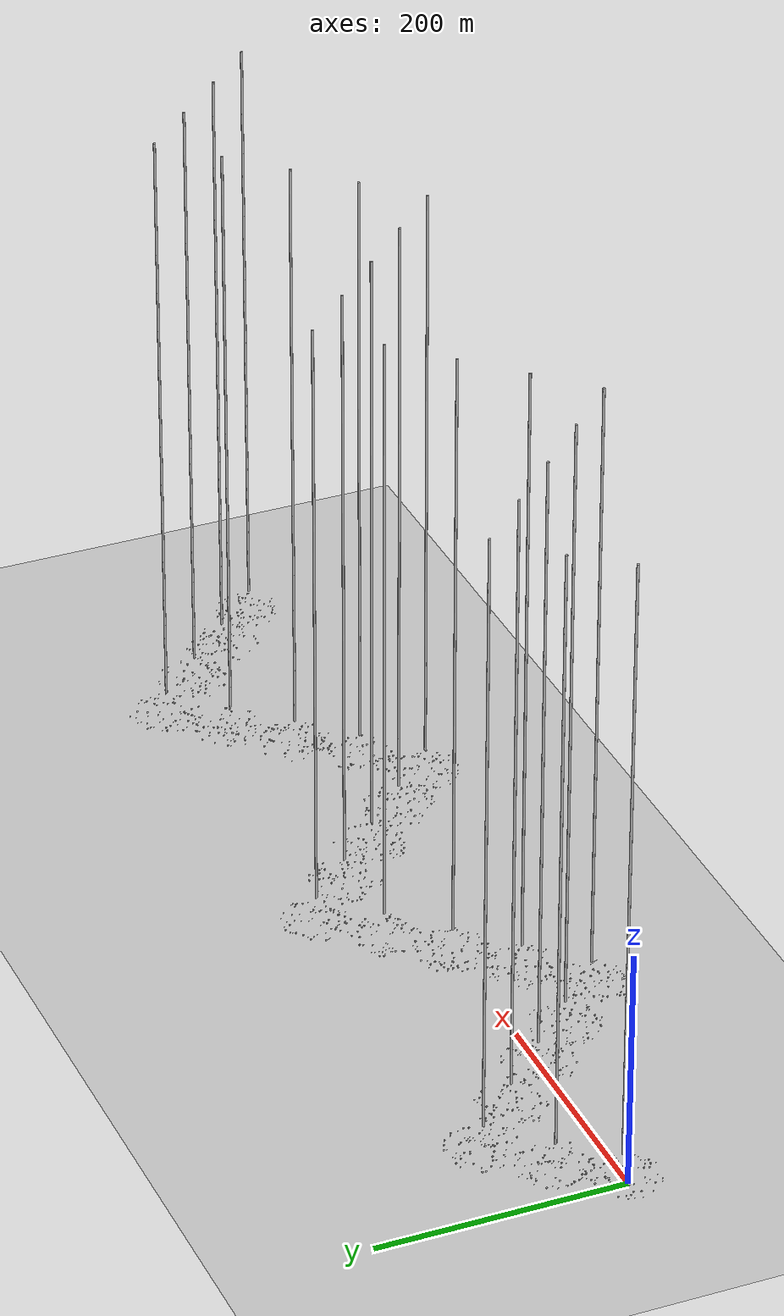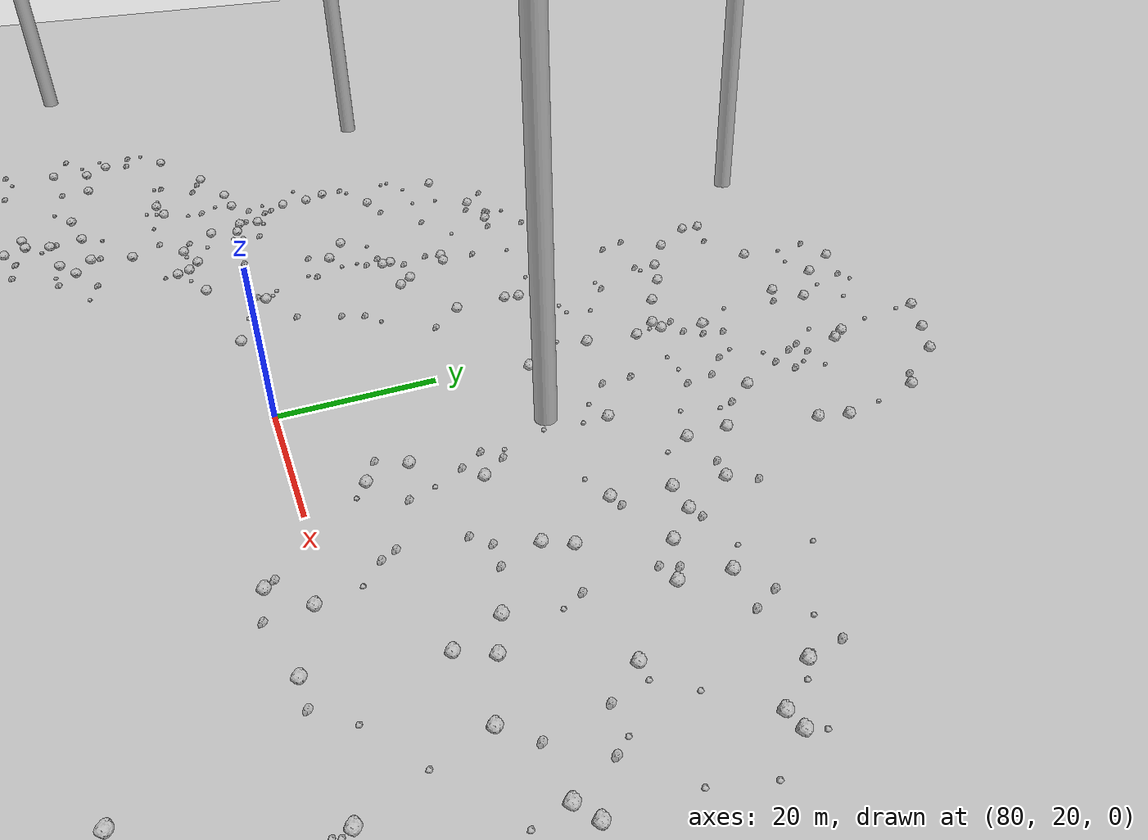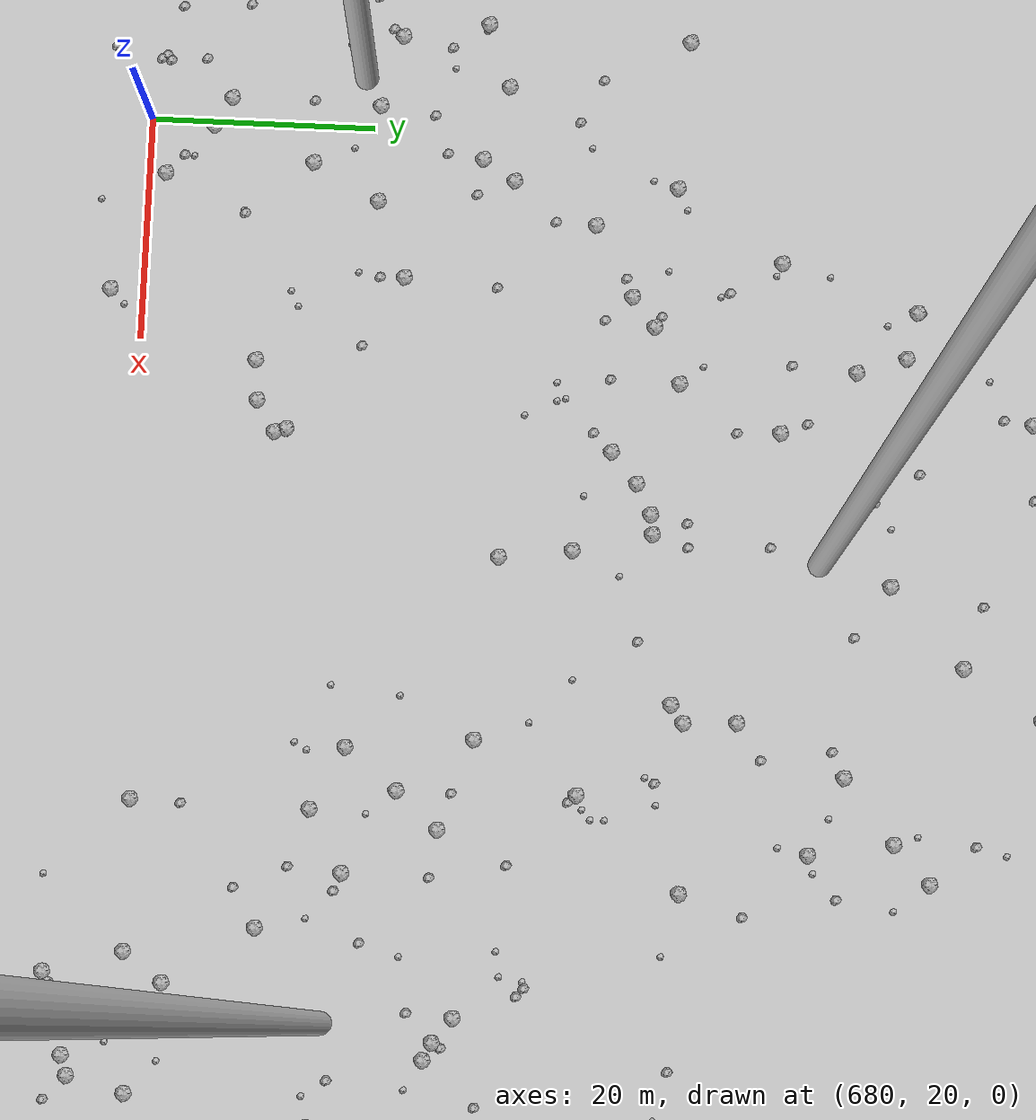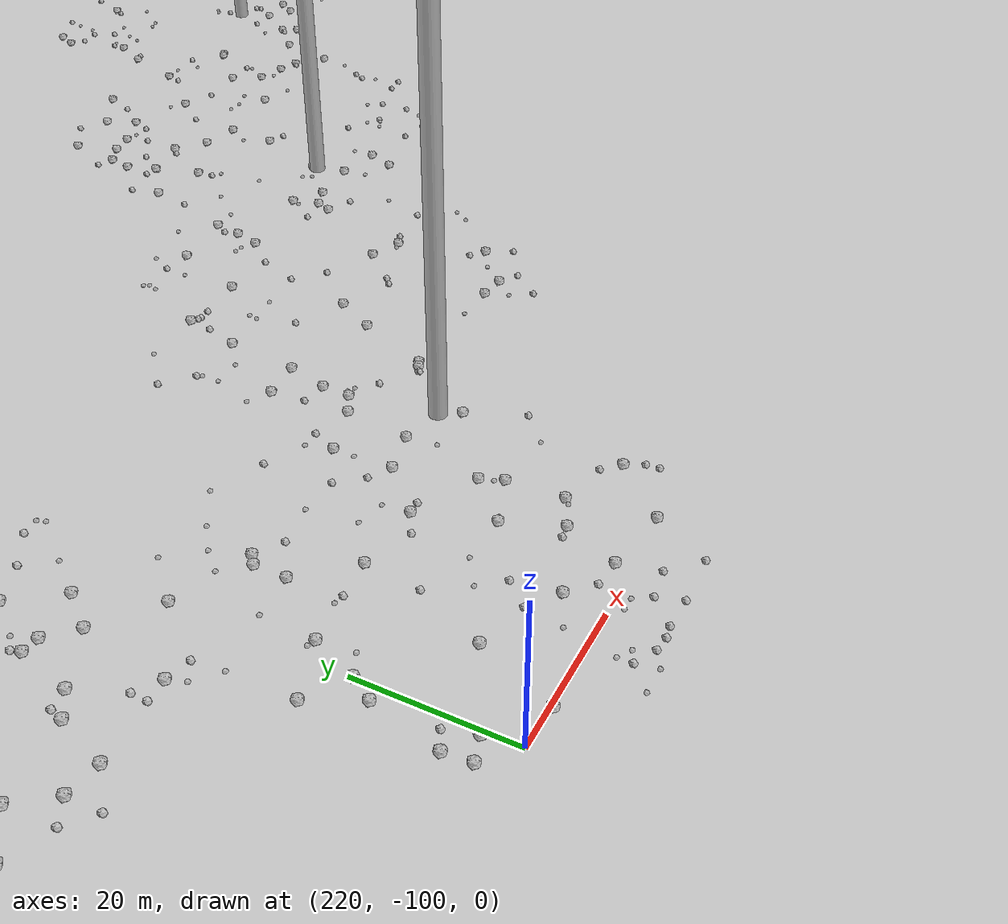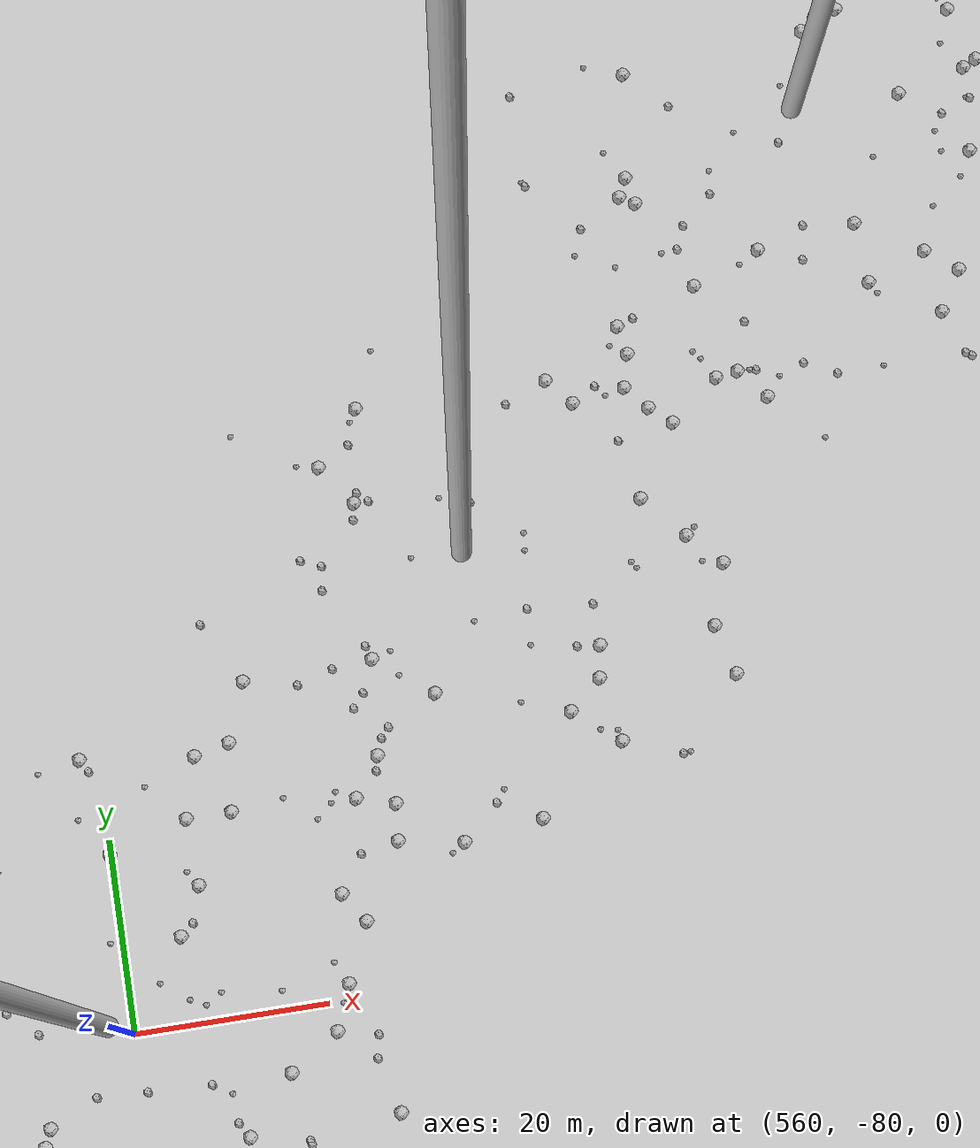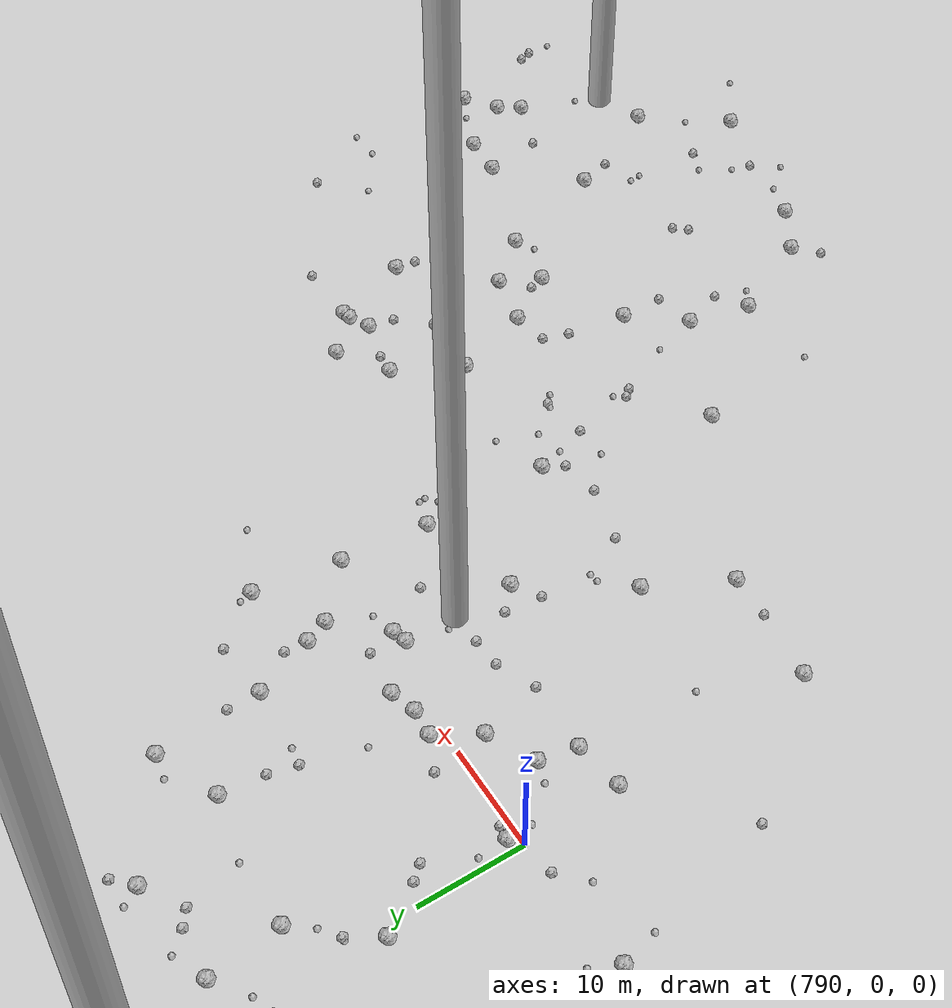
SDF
<sdf version="1.6">
 <world name="default">
  <include><uri>model://custom_ground</uri></include>
  <include><uri>model://sun</uri></include>
  <spherical_coordinates>
   <surface_model>EARTH_WGS84</surface_model>
   <latitude_deg>38.161479</latitude_deg>
   <longitude_deg>-122.454630</longitude_deg>
   <elevation>488.0</elevation>
   <heading_deg>90</heading_deg>
  </spherical_coordinates>
  <model name="rock1_0_0">
   <include><uri>model://rock1</uri><pose>19.724716551113964 -11.722472759081889 0.5 0 0 0</pose></include>
  </model>
  <model name="rock1_0_1">
   <include><uri>model://rock1</uri><pose>13.80238084941874 23.100708270481213 0.5 0 0 0</pose></include>
  </model>
  <model name="rock1_0_2">
   <include><uri>model://rock1</uri><pose>26.58502744879698 0.6404993337532687 0.5 0 0 0</pose></include>
  </model>
  <model name="rock1_0_3">
   <include><uri>model://rock1</uri><pose>-12.629926643160683 -4.887122520911504 0.5 0 0 0</pose></include>
  </model>
  <model name="rock1_0_4">
   <include><uri>model://rock1</uri><pose>37.01559315031228 12.534004559642739 0.5 0 0 0</pose></include>
  </model>
  <model name="rock1_0_5">
   <include><uri>model://rock1</uri><pose>26.97317730760927 -3.7521410446310526 0.5 0 0 0</pose></include>
  </model>
  <model name="rock1_0_6">
   <include><uri>model://rock1</uri><pose>17.986171244220095 -0.5519500790536824 0.5 0 0 0</pose></include>
  </model>
  <model name="rock1_0_7">
   <include><uri>model://rock1</uri><pose>-10.904290465323776 0.6423649359624264 0.5 0 0 0</pose></include>
  </model>
  <model name="rock1_0_8">
   <include><uri>model://rock1</uri><pose>10.175523150825388 -2.0274310179414137 0.5 0 0 0</pose></include>
  </model>
  <model name="rock1_0_9">
   <include><uri>model://rock1</uri><pose>28.12491999658954 6.58218707608507 0.5 0 0 0</pose></include>
  </model>
  <model name="rock1_0_10">
   <include><uri>model://rock1</uri><pose>-3.002439164977069 0.7761917120309327 0.5 0 0 0</pose></include>
  </model>
  <model name="rock1_0_11">
   <include><uri>model://rock1</uri><pose>12.321093424580702 -18.24577601203778 0.5 0 0 0</pose></include>
  </model>
  <model name="rock1_0_12">
   <include><uri>model://rock1</uri><pose>19.087551692404368 -5.217226689133895 0.5 0 0 0</pose></include>
  </model>
  <model name="rock1_0_13">
   <include><uri>model://rock1</uri><pose>-12.272127852948193 13.442739897513803 0.5 0 0 0</pose></include>
  </model>
  <model name="rock1_0_14">
   <include><uri>model://rock1</uri><pose>-7.189460325592883 -18.79434283441582 0.5 0 0 0</pose></include>
  </model>
  <model name="rock1_0_15">
   <include><uri>model://rock1</uri><pose>20.099761779133644 -25.77307892692574 0.5 0 0 0</pose></include>
  </model>
  <model name="rock1_0_16">
   <include><uri>model://rock1</uri><pose>8.410495699876947 22.54698822393503 0.5 0 0 0</pose></include>
  </model>
  <model name="rock1_0_17">
   <include><uri>model://rock1</uri><pose>15.097122825017024 -24.978609942481746 0.5 0 0 0</pose></include>
  </model>
  <model name="rock1_0_18">
   <include><uri>model://rock1</uri><pose>-13.991168334492867 3.9080326306544535 0.5 0 0 0</pose></include>
  </model>
  <model name="rock1_0_19">
   <include><uri>model://rock1</uri><pose>-0.6902788335467882 19.466146008242873 0.5 0 0 0</pose></include>
  </model>
  <model name="rock1_0_20">
   <include><uri>model://rock1</uri><pose>15.032908085699418 -9.355245130054811 0.5 0 0 0</pose></include>
  </model>
  <model name="rock1_0_21">
   <include><uri>model://rock1</uri><pose>11.554656458303697 -22.499827983644874 0.5 0 0 0</pose></include>
  </model>
  <model name="rock1_0_22">
   <include><uri>model://rock1</uri><pose>30.629400173062898 -1.473009429403163 0.5 0 0 0</pose></include>
  </model>
  <model name="rock1_0_23">
   <include><uri>model://rock1</uri><pose>9.038047644719278 11.299128465402582 0.5 0 0 0</pose></include>
  </model>
  <model name="rock1_0_24">
   <include><uri>model://rock1</uri><pose>12.999548638222556 12.238604030574777 0.5 0 0 0</pose></include>
  </model>
  <model name="rock1_0_25">
   <include><uri>model://rock1</uri><pose>18.03990549368399 -8.747966425728006 0.5 0 0 0</pose></include>
  </model>
  <model name="rock1_0_26">
   <include><uri>model://rock1</uri><pose>23.95791260916799 18.696225427344977 0.5 0 0 0</pose></include>
  </model>
  <model name="rock2_0_0">
   <include><uri>model://rock2</uri><pose>26.301026490829273 1.9627272071270276 0.3 0 0 0</pose></include>
  </model>
  <model name="rock2_0_1">
   <include><uri>model://rock2</uri><pose>33.45488313099638 -3.908294212939481 0.3 0 0 0</pose></include>
  </model>
  <model name="rock2_0_2">
   <include><uri>model://rock2</uri><pose>28.302674399420333 -10.345115174906812 0.3 0 0 0</pose></include>
  </model>
  <model name="rock2_0_3">
   <include><uri>model://rock2</uri><pose>27.7415016515274 23.169461967081773 0.3 0 0 0</pose></include>
  </model>
  <model name="rock2_0_4">
   <include><uri>model://rock2</uri><pose>1.169118764615714 18.599968832762556 0.3 0 0 0</pose></include>
  </model>
  <model name="rock2_0_5">
   <include><uri>model://rock2</uri><pose>-15.553308857496615 -12.960622856172325 0.3 0 0 0</pose></include>
  </model>
  <model name="rock2_0_6">
   <include><uri>model://rock2</uri><pose>-4.998409538504802 -12.681926908334109 0.3 0 0 0</pose></include>
  </model>
  <model name="rock2_0_7">
   <include><uri>model://rock2</uri><pose>-13.520334856838039 7.406769788547521 0.3 0 0 0</pose></include>
  </model>
  <model name="rock2_0_8">
   <include><uri>model://rock2</uri><pose>4.42183853618052 17.5521301458814 0.3 0 0 0</pose></include>
  </model>
  <model name="rock2_0_9">
   <include><uri>model://rock2</uri><pose>1.2486916762275513 -14.203960429944281 0.3 0 0 0</pose></include>
  </model>
  <model name="rock2_0_10">
   <include><uri>model://rock2</uri><pose>26.174301287115355 15.113511554030296 0.3 0 0 0</pose></include>
  </model>
  <model name="rock2_0_11">
   <include><uri>model://rock2</uri><pose>23.622223157101118 -10.051354726190745 0.3 0 0 0</pose></include>
  </model>
  <model name="rock2_0_12">
   <include><uri>model://rock2</uri><pose>28.66610191070621 -18.822656927766957 0.3 0 0 0</pose></include>
  </model>
  <model name="rock2_0_13">
   <include><uri>model://rock2</uri><pose>14.58091897407597 18.109963846949668 0.3 0 0 0</pose></include>
  </model>
  <model name="rock2_0_14">
   <include><uri>model://rock2</uri><pose>-19.78478106644112 -2.914858331687604 0.3 0 0 0</pose></include>
  </model>
  <model name="rock2_0_15">
   <include><uri>model://rock2</uri><pose>14.731709372355951 -29.425981087128534 0.3 0 0 0</pose></include>
  </model>
  <model name="rock2_0_16">
   <include><uri>model://rock2</uri><pose>35.81638368463736 1.339792630380778 0.3 0 0 0</pose></include>
  </model>
  <model name="rock2_0_17">
   <include><uri>model://rock2</uri><pose>24.688786410707955 10.72215750153078 0.3 0 0 0</pose></include>
  </model>
  <model name="rock2_0_18">
   <include><uri>model://rock2</uri><pose>26.547425532041046 -13.961185421685592 0.3 0 0 0</pose></include>
  </model>
  <model name="rock2_0_19">
   <include><uri>model://rock2</uri><pose>18.483332674303384 -4.3463742899160955 0.3 0 0 0</pose></include>
  </model>
  <model name="rock2_0_20">
   <include><uri>model://rock2</uri><pose>16.702909921323503 25.54073682724647 0.3 0 0 0</pose></include>
  </model>
  <model name="rock2_0_21">
   <include><uri>model://rock2</uri><pose>-2.945133578341082 -3.5155814255109448 0.3 0 0 0</pose></include>
  </model>
  <model name="rock2_0_22">
   <include><uri>model://rock2</uri><pose>0.6793742061384158 12.559907197347101 0.3 0 0 0</pose></include>
  </model>
  <model name="rock2_0_23">
   <include><uri>model://rock2</uri><pose>-4.494583498668618 -25.819064027480586 0.3 0 0 0</pose></include>
  </model>
  <model name="rock2_0_24">
   <include><uri>model://rock2</uri><pose>-7.513935359561367 -24.141178313304408 0.3 0 0 0</pose></include>
  </model>
  <model name="rock2_0_25">
   <include><uri>model://rock2</uri><pose>-17.371746377675276 7.781273792298663 0.3 0 0 0</pose></include>
  </model>
  <model name="rock2_0_26">
   <include><uri>model://rock2</uri><pose>16.16302710849957 -21.250672051021944 0.3 0 0 0</pose></include>
  </model>
  <model name="rock3_0_0">
   <include><uri>model://rock3</uri><pose>-17.94326152378732 10.087504837131632 0.2 0 0 0</pose></include>
  </model>
  <model name="rock3_0_1">
   <include><uri>model://rock3</uri><pose>-15.587303061675348 -0.17645101257475915 0.2 0 0 0</pose></include>
  </model>
  <model name="rock3_0_2">
   <include><uri>model://rock3</uri><pose>11.749961333426185 11.081430395673458 0.2 0 0 0</pose></include>
  </model>
  <model name="rock3_0_3">
   <include><uri>model://rock3</uri><pose>5.490978799131536 -4.729798734566714 0.2 0 0 0</pose></include>
  </model>
  <model name="rock3_0_4">
   <include><uri>model://rock3</uri><pose>19.106507111185955 2.3734307774554537 0.2 0 0 0</pose></include>
  </model>
  <model name="rock3_0_5">
   <include><uri>model://rock3</uri><pose>26.04221444350034 -20.056065960336227 0.2 0 0 0</pose></include>
  </model>
  <model name="rock3_0_6">
   <include><uri>model://rock3</uri><pose>25.67755184188404 -14.355827893596375 0.2 0 0 0</pose></include>
  </model>
  <model name="rock3_0_7">
   <include><uri>model://rock3</uri><pose>-1.991714784959953 -16.509891211213542 0.2 0 0 0</pose></include>
  </model>
  <model name="rock3_0_8">
   <include><uri>model://rock3</uri><pose>22.71470239489716 -9.934074388015507 0.2 0 0 0</pose></include>
  </model>
  <model name="rock3_0_9">
   <include><uri>model://rock3</uri><pose>-17.880163365229897 2.8655490783155884 0.2 0 0 0</pose></include>
  </model>
  <model name="rock3_0_10">
   <include><uri>model://rock3</uri><pose>14.357544148215602 15.909430100581076 0.2 0 0 0</pose></include>
  </model>
  <model name="rock3_0_11">
   <include><uri>model://rock3</uri><pose>1.642090856375951 -24.502820905386358 0.2 0 0 0</pose></include>
  </model>
  <model name="rock3_0_12">
   <include><uri>model://rock3</uri><pose>0.27031130231041445 11.372002825946787 0.2 0 0 0</pose></include>
  </model>
  <model name="rock3_0_13">
   <include><uri>model://rock3</uri><pose>20.310117033413725 -22.9520273424419 0.2 0 0 0</pose></include>
  </model>
  <model name="rock3_0_14">
   <include><uri>model://rock3</uri><pose>11.084359755562396 9.532622416436325 0.2 0 0 0</pose></include>
  </model>
  <model name="rock3_0_15">
   <include><uri>model://rock3</uri><pose>6.261617436494831 11.545423385825728 0.2 0 0 0</pose></include>
  </model>
  <model name="rock3_0_16">
   <include><uri>model://rock3</uri><pose>39.78791950656179 0.1840014230560456 0.2 0 0 0</pose></include>
  </model>
  <model name="rock3_0_17">
   <include><uri>model://rock3</uri><pose>10.811562844096574 12.463591616989348 0.2 0 0 0</pose></include>
  </model>
  <model name="rock3_0_18">
   <include><uri>model://rock3</uri><pose>30.73421249258157 14.254119043150553 0.2 0 0 0</pose></include>
  </model>
  <model name="rock3_0_19">
   <include><uri>model://rock3</uri><pose>30.485137893975306 -4.378384492292003 0.2 0 0 0</pose></include>
  </model>
  <model name="rock3_0_20">
   <include><uri>model://rock3</uri><pose>12.446889592975928 20.464631589177344 0.2 0 0 0</pose></include>
  </model>
  <model name="rock3_0_21">
   <include><uri>model://rock3</uri><pose>14.096424629712331 -14.692759112698555 0.2 0 0 0</pose></include>
  </model>
  <model name="rock3_0_22">
   <include><uri>model://rock3</uri><pose>21.91578048018725 -20.582051569653174 0.2 0 0 0</pose></include>
  </model>
  <model name="rock3_0_23">
   <include><uri>model://rock3</uri><pose>-11.824054451695641 -11.790707050692284 0.2 0 0 0</pose></include>
  </model>
  <model name="rock3_0_24">
   <include><uri>model://rock3</uri><pose>20.112928641274472 -6.444621002028658 0.2 0 0 0</pose></include>
  </model>
  <model name="rock3_0_25">
   <include><uri>model://rock3</uri><pose>26.67861298096272 21.746464359323845 0.2 0 0 0</pose></include>
  </model>
  <model name="rock3_0_26">
   <include><uri>model://rock3</uri><pose>17.64163507679902 10.285779066915296 0.2 0 0 0</pose></include>
  </model>
  <model name="rock1_1_0">
   <include><uri>model://rock1</uri><pose>53.56469790883192 42.369204079430354 0.5 0 0 0</pose></include>
  </model>
  <model name="rock1_1_1">
   <include><uri>model://rock1</uri><pose>24.92432710629015 22.641605657744744 0.5 0 0 0</pose></include>
  </model>
  <model name="rock1_1_2">
   <include><uri>model://rock1</uri><pose>16.749358517694787 31.229352066294044 0.5 0 0 0</pose></include>
  </model>
  <model name="rock1_1_3">
   <include><uri>model://rock1</uri><pose>51.810203450070475 44.25061504880572 0.5 0 0 0</pose></include>
  </model>
  <model name="rock1_1_4">
   <include><uri>model://rock1</uri><pose>45.7751392710726 41.51672825418411 0.5 0 0 0</pose></include>
  </model>
  <model name="rock1_1_5">
   <include><uri>model://rock1</uri><pose>45.68858870521976 42.717656156031794 0.5 0 0 0</pose></include>
  </model>
  <model name="rock1_1_6">
   <include><uri>model://rock1</uri><pose>35.65859038337893 61.30617597653476 0.5 0 0 0</pose></include>
  </model>
  <model name="rock1_1_7">
   <include><uri>model://rock1</uri><pose>48.27144161584454 50.370808287140946 0.5 0 0 0</pose></include>
  </model>
  <model name="rock1_1_8">
   <include><uri>model://rock1</uri><pose>63.68373104951998 57.11065894498379 0.5 0 0 0</pose></include>
  </model>
  <model name="rock1_1_9">
   <include><uri>model://rock1</uri><pose>36.170530901043605 14.263565529539694 0.5 0 0 0</pose></include>
  </model>
  <model name="rock1_1_10">
   <include><uri>model://rock1</uri><pose>14.903982577024736 38.275873941772986 0.5 0 0 0</pose></include>
  </model>
  <model name="rock1_1_11">
   <include><uri>model://rock1</uri><pose>28.383148977600335 60.51959811113291 0.5 0 0 0</pose></include>
  </model>
  <model name="rock1_1_12">
   <include><uri>model://rock1</uri><pose>60.989153737435 18.642143461820986 0.5 0 0 0</pose></include>
  </model>
  <model name="rock1_1_13">
   <include><uri>model://rock1</uri><pose>35.934915312877635 37.13237546127395 0.5 0 0 0</pose></include>
  </model>
  <model name="rock1_1_14">
   <include><uri>model://rock1</uri><pose>21.62977070796927 44.70250173408404 0.5 0 0 0</pose></include>
  </model>
  <model name="rock1_1_15">
   <include><uri>model://rock1</uri><pose>29.30126864161362 14.021199081172684 0.5 0 0 0</pose></include>
  </model>
  <model name="rock1_1_16">
   <include><uri>model://rock1</uri><pose>40.5596296774775 34.44441139214534 0.5 0 0 0</pose></include>
  </model>
  <model name="rock1_1_17">
   <include><uri>model://rock1</uri><pose>22.24418301757871 26.22986759844469 0.5 0 0 0</pose></include>
  </model>
  <model name="rock1_1_18">
   <include><uri>model://rock1</uri><pose>21.96771984969865 23.43192761569686 0.5 0 0 0</pose></include>
  </model>
  <model name="rock1_1_19">
   <include><uri>model://rock1</uri><pose>16.3057917268898 35.25060921126292 0.5 0 0 0</pose></include>
  </model>
  <model name="rock1_1_20">
   <include><uri>model://rock1</uri><pose>50.19783599002302 23.481521246886146 0.5 0 0 0</pose></include>
  </model>
  <model name="rock1_1_21">
   <include><uri>model://rock1</uri><pose>33.87227028061396 15.687076446336087 0.5 0 0 0</pose></include>
  </model>
  <model name="rock1_1_22">
   <include><uri>model://rock1</uri><pose>63.65389961948388 47.854200229752976 0.5 0 0 0</pose></include>
  </model>
  <model name="rock1_1_23">
   <include><uri>model://rock1</uri><pose>17.419769351657315 56.84651268944468 0.5 0 0 0</pose></include>
  </model>
  <model name="rock1_1_24">
   <include><uri>model://rock1</uri><pose>44.053897505303276 15.904155853951993 0.5 0 0 0</pose></include>
  </model>
  <model name="rock1_1_25">
   <include><uri>model://rock1</uri><pose>63.34144394596318 55.082915983301376 0.5 0 0 0</pose></include>
  </model>
  <model name="rock1_1_26">
   <include><uri>model://rock1</uri><pose>46.26963730154749 50.53665790405672 0.5 0 0 0</pose></include>
  </model>
  <model name="rock2_1_0">
   <include><uri>model://rock2</uri><pose>60.41109501774703 35.45302968694842 0.3 0 0 0</pose></include>
  </model>
  <model name="rock2_1_1">
   <include><uri>model://rock2</uri><pose>51.335564266832634 67.10702641001467 0.3 0 0 0</pose></include>
  </model>
  <model name="rock2_1_2">
   <include><uri>model://rock2</uri><pose>48.86730752462346 22.453950109496255 0.3 0 0 0</pose></include>
  </model>
  <model name="rock2_1_3">
   <include><uri>model://rock2</uri><pose>38.651697947589994 60.80763616404766 0.3 0 0 0</pose></include>
  </model>
  <model name="rock2_1_4">
   <include><uri>model://rock2</uri><pose>32.687714514518305 62.16294027455288 0.3 0 0 0</pose></include>
  </model>
  <model name="rock2_1_5">
   <include><uri>model://rock2</uri><pose>45.75660241299494 31.614426959757115 0.3 0 0 0</pose></include>
  </model>
  <model name="rock2_1_6">
   <include><uri>model://rock2</uri><pose>30.951801945239886 59.44510628922808 0.3 0 0 0</pose></include>
  </model>
  <model name="rock2_1_7">
   <include><uri>model://rock2</uri><pose>59.18473301043265 32.449892677981225 0.3 0 0 0</pose></include>
  </model>
  <model name="rock2_1_8">
   <include><uri>model://rock2</uri><pose>14.11482643019545 41.4757672828039 0.3 0 0 0</pose></include>
  </model>
  <model name="rock2_1_9">
   <include><uri>model://rock2</uri><pose>39.42907410204904 66.36100466034506 0.3 0 0 0</pose></include>
  </model>
  <model name="rock2_1_10">
   <include><uri>model://rock2</uri><pose>45.518401554710714 48.24711751279224 0.3 0 0 0</pose></include>
  </model>
  <model name="rock2_1_11">
   <include><uri>model://rock2</uri><pose>56.88890056684366 26.692059825231595 0.3 0 0 0</pose></include>
  </model>
  <model name="rock2_1_12">
   <include><uri>model://rock2</uri><pose>43.39086499211633 41.24186478685134 0.3 0 0 0</pose></include>
  </model>
  <model name="rock2_1_13">
   <include><uri>model://rock2</uri><pose>21.297447811181293 24.446755209362863 0.3 0 0 0</pose></include>
  </model>
  <model name="rock2_1_14">
   <include><uri>model://rock2</uri><pose>24.809035850795926 63.69068367164237 0.3 0 0 0</pose></include>
  </model>
  <model name="rock2_1_15">
   <include><uri>model://rock2</uri><pose>18.76471535848301 27.88272108528623 0.3 0 0 0</pose></include>
  </model>
  <model name="rock2_1_16">
   <include><uri>model://rock2</uri><pose>39.05504392754061 31.473289768241976 0.3 0 0 0</pose></include>
  </model>
  <model name="rock2_1_17">
   <include><uri>model://rock2</uri><pose>26.173833382214827 45.93078317385014 0.3 0 0 0</pose></include>
  </model>
  <model name="rock2_1_18">
   <include><uri>model://rock2</uri><pose>67.49751842922498 43.67464077035345 0.3 0 0 0</pose></include>
  </model>
  <model name="rock2_1_19">
   <include><uri>model://rock2</uri><pose>27.71008692359718 25.750040716647984 0.3 0 0 0</pose></include>
  </model>
  <model name="rock2_1_20">
   <include><uri>model://rock2</uri><pose>18.010099654725664 29.02296305202446 0.3 0 0 0</pose></include>
  </model>
  <model name="rock2_1_21">
   <include><uri>model://rock2</uri><pose>47.65609559866417 55.230085524971756 0.3 0 0 0</pose></include>
  </model>
  <model name="rock2_1_22">
   <include><uri>model://rock2</uri><pose>33.25102566458619 62.50071973353389 0.3 0 0 0</pose></include>
  </model>
  <model name="rock2_1_23">
   <include><uri>model://rock2</uri><pose>46.904621210272595 44.53558557234294 0.3 0 0 0</pose></include>
  </model>
  <model name="rock2_1_24">
   <include><uri>model://rock2</uri><pose>36.840665780904814 22.18072892693764 0.3 0 0 0</pose></include>
  </model>
  <model name="rock2_1_25">
   <include><uri>model://rock2</uri><pose>44.852423777231145 39.25053547729623 0.3 0 0 0</pose></include>
  </model>
  <model name="rock2_1_26">
   <include><uri>model://rock2</uri><pose>32.83451864142529 51.203898041119004 0.3 0 0 0</pose></include>
  </model>
  <model name="rock3_1_0">
   <include><uri>model://rock3</uri><pose>58.042637491694194 60.2459640662197 0.2 0 0 0</pose></include>
  </model>
  <model name="rock3_1_1">
   <include><uri>model://rock3</uri><pose>54.41556965558482 20.416085779716063 0.2 0 0 0</pose></include>
  </model>
  <model name="rock3_1_2">
   <include><uri>model://rock3</uri><pose>35.83616001152102 69.68855391963871 0.2 0 0 0</pose></include>
  </model>
  <model name="rock3_1_3">
   <include><uri>model://rock3</uri><pose>43.46546869518386 38.04860904777991 0.2 0 0 0</pose></include>
  </model>
  <model name="rock3_1_4">
   <include><uri>model://rock3</uri><pose>15.244312028628384 42.38397407053303 0.2 0 0 0</pose></include>
  </model>
  <model name="rock3_1_5">
   <include><uri>model://rock3</uri><pose>22.69890055340648 27.07841582317807 0.2 0 0 0</pose></include>
  </model>
  <model name="rock3_1_6">
   <include><uri>model://rock3</uri><pose>13.642565680973329 49.9702671825332 0.2 0 0 0</pose></include>
  </model>
  <model name="rock3_1_7">
   <include><uri>model://rock3</uri><pose>15.104310829097752 27.93656841468918 0.2 0 0 0</pose></include>
  </model>
  <model name="rock3_1_8">
   <include><uri>model://rock3</uri><pose>24.24731155351848 51.95955869731964 0.2 0 0 0</pose></include>
  </model>
  <model name="rock3_1_9">
   <include><uri>model://rock3</uri><pose>28.374204682716616 17.597405918177394 0.2 0 0 0</pose></include>
  </model>
  <model name="rock3_1_10">
   <include><uri>model://rock3</uri><pose>39.357378902562814 14.105171364719816 0.2 0 0 0</pose></include>
  </model>
  <model name="rock3_1_11">
   <include><uri>model://rock3</uri><pose>24.65572552109529 55.83001050909284 0.2 0 0 0</pose></include>
  </model>
  <model name="rock3_1_12">
   <include><uri>model://rock3</uri><pose>33.249118814286106 64.98706201667738 0.2 0 0 0</pose></include>
  </model>
  <model name="rock3_1_13">
   <include><uri>model://rock3</uri><pose>44.65400651777011 30.46594583768557 0.2 0 0 0</pose></include>
  </model>
  <model name="rock3_1_14">
   <include><uri>model://rock3</uri><pose>38.12716895095114 69.91761206879156 0.2 0 0 0</pose></include>
  </model>
  <model name="rock3_1_15">
   <include><uri>model://rock3</uri><pose>43.58714768805688 35.725953926146 0.2 0 0 0</pose></include>
  </model>
  <model name="rock3_1_16">
   <include><uri>model://rock3</uri><pose>48.94982174159505 24.575271914388146 0.2 0 0 0</pose></include>
  </model>
  <model name="rock3_1_17">
   <include><uri>model://rock3</uri><pose>47.567604685049915 25.31988485105344 0.2 0 0 0</pose></include>
  </model>
  <model name="rock3_1_18">
   <include><uri>model://rock3</uri><pose>38.7992066279742 54.525841737144816 0.2 0 0 0</pose></include>
  </model>
  <model name="rock3_1_19">
   <include><uri>model://rock3</uri><pose>17.592550105954537 51.92750416597136 0.2 0 0 0</pose></include>
  </model>
  <model name="rock3_1_20">
   <include><uri>model://rock3</uri><pose>40.60626211472368 34.83647491622999 0.2 0 0 0</pose></include>
  </model>
  <model name="rock3_1_21">
   <include><uri>model://rock3</uri><pose>36.87619455994042 10.692361803573444 0.2 0 0 0</pose></include>
  </model>
  <model name="rock3_1_22">
   <include><uri>model://rock3</uri><pose>38.07048867507635 40.810288023982515 0.2 0 0 0</pose></include>
  </model>
  <model name="rock3_1_23">
   <include><uri>model://rock3</uri><pose>10.80005979401793 33.87697650296972 0.2 0 0 0</pose></include>
  </model>
  <model name="rock3_1_24">
   <include><uri>model://rock3</uri><pose>48.135530340372334 60.76586769241754 0.2 0 0 0</pose></include>
  </model>
  <model name="rock3_1_25">
   <include><uri>model://rock3</uri><pose>62.601251835624566 37.25155871651699 0.2 0 0 0</pose></include>
  </model>
  <model name="rock3_1_26">
   <include><uri>model://rock3</uri><pose>14.0081295971205 48.828123319426055 0.2 0 0 0</pose></include>
  </model>
  <model name="rock1_2_0">
   <include><uri>model://rock1</uri><pose>52.860370848931254 92.23160858114696 0.5 0 0 0</pose></include>
  </model>
  <model name="rock1_2_1">
   <include><uri>model://rock1</uri><pose>76.7550947167231 91.72995552589148 0.5 0 0 0</pose></include>
  </model>
  <model name="rock1_2_2">
   <include><uri>model://rock1</uri><pose>79.39336257665067 61.151150991847885 0.5 0 0 0</pose></include>
  </model>
  <model name="rock1_2_3">
   <include><uri>model://rock1</uri><pose>62.67769873539959 79.54566515283571 0.5 0 0 0</pose></include>
  </model>
  <model name="rock1_2_4">
   <include><uri>model://rock1</uri><pose>103.90775692775868 68.63750574323166 0.5 0 0 0</pose></include>
  </model>
  <model name="rock1_2_5">
   <include><uri>model://rock1</uri><pose>73.71841953157625 100.13354108079857 0.5 0 0 0</pose></include>
  </model>
  <model name="rock1_2_6">
   <include><uri>model://rock1</uri><pose>80.44702122855216 68.03672331859728 0.5 0 0 0</pose></include>
  </model>
  <model name="rock1_2_7">
   <include><uri>model://rock1</uri><pose>52.69322499627552 89.50591217209825 0.5 0 0 0</pose></include>
  </model>
  <model name="rock1_2_8">
   <include><uri>model://rock1</uri><pose>88.23100233220819 107.7118868909513 0.5 0 0 0</pose></include>
  </model>
  <model name="rock1_2_9">
   <include><uri>model://rock1</uri><pose>56.920472116481704 83.5248615244094 0.5 0 0 0</pose></include>
  </model>
  <model name="rock1_2_10">
   <include><uri>model://rock1</uri><pose>91.66440662236367 92.32365671729144 0.5 0 0 0</pose></include>
  </model>
  <model name="rock1_2_11">
   <include><uri>model://rock1</uri><pose>93.98274726759529 105.03027781123474 0.5 0 0 0</pose></include>
  </model>
  <model name="rock1_2_12">
   <include><uri>model://rock1</uri><pose>80.05875134432434 71.96871252059685 0.5 0 0 0</pose></include>
  </model>
  <model name="rock1_2_13">
   <include><uri>model://rock1</uri><pose>67.24304939289088 77.75947919394756 0.5 0 0 0</pose></include>
  </model>
  <model name="rock1_2_14">
   <include><uri>model://rock1</uri><pose>79.99731239252733 95.00006755370377 0.5 0 0 0</pose></include>
  </model>
  <model name="rock1_2_15">
   <include><uri>model://rock1</uri><pose>72.46932440178146 74.27769245055485 0.5 0 0 0</pose></include>
  </model>
  <model name="rock1_2_16">
   <include><uri>model://rock1</uri><pose>64.95810556031086 93.97072622016009 0.5 0 0 0</pose></include>
  </model>
  <model name="rock1_2_17">
   <include><uri>model://rock1</uri><pose>98.95557675568826 102.3351627090187 0.5 0 0 0</pose></include>
  </model>
  <model name="rock1_2_18">
   <include><uri>model://rock1</uri><pose>90.44343828356605 94.18740614683941 0.5 0 0 0</pose></include>
  </model>
  <model name="rock1_2_19">
   <include><uri>model://rock1</uri><pose>70.07720495060366 105.63809823299025 0.5 0 0 0</pose></include>
  </model>
  <model name="rock1_2_20">
   <include><uri>model://rock1</uri><pose>78.24490486012434 71.432436685371 0.5 0 0 0</pose></include>
  </model>
  <model name="rock1_2_21">
   <include><uri>model://rock1</uri><pose>82.01501984501954 51.93839719346464 0.5 0 0 0</pose></include>
  </model>
  <model name="rock1_2_22">
   <include><uri>model://rock1</uri><pose>81.2936099574143 77.62982713602642 0.5 0 0 0</pose></include>
  </model>
  <model name="rock1_2_23">
   <include><uri>model://rock1</uri><pose>96.94052547557285 75.56536160516228 0.5 0 0 0</pose></include>
  </model>
  <model name="rock1_2_24">
   <include><uri>model://rock1</uri><pose>106.47856399126964 79.7321228850098 0.5 0 0 0</pose></include>
  </model>
  <model name="rock1_2_25">
   <include><uri>model://rock1</uri><pose>105.03115639926372 94.59182023513014 0.5 0 0 0</pose></include>
  </model>
  <model name="rock1_2_26">
   <include><uri>model://rock1</uri><pose>107.45402029367409 83.5086009050962 0.5 0 0 0</pose></include>
  </model>
  <model name="rock2_2_0">
   <include><uri>model://rock2</uri><pose>83.53837318499836 76.60218967845165 0.3 0 0 0</pose></include>
  </model>
  <model name="rock2_2_1">
   <include><uri>model://rock2</uri><pose>95.92633696449481 83.36235306180896 0.3 0 0 0</pose></include>
  </model>
  <model name="rock2_2_2">
   <include><uri>model://rock2</uri><pose>54.23438191616572 74.61528681968376 0.3 0 0 0</pose></include>
  </model>
  <model name="rock2_2_3">
   <include><uri>model://rock2</uri><pose>89.38484752274411 62.92801076618266 0.3 0 0 0</pose></include>
  </model>
  <model name="rock2_2_4">
   <include><uri>model://rock2</uri><pose>62.01950560201086 76.50174852807861 0.3 0 0 0</pose></include>
  </model>
  <model name="rock2_2_5">
   <include><uri>model://rock2</uri><pose>81.13496775588042 78.30555837327695 0.3 0 0 0</pose></include>
  </model>
  <model name="rock2_2_6">
   <include><uri>model://rock2</uri><pose>93.69626037103858 81.79764842004289 0.3 0 0 0</pose></include>
  </model>
  <model name="rock2_2_7">
   <include><uri>model://rock2</uri><pose>89.81014736415236 75.54875218798601 0.3 0 0 0</pose></include>
  </model>
  <model name="rock2_2_8">
   <include><uri>model://rock2</uri><pose>102.86823861147636 96.04383470809782 0.3 0 0 0</pose></include>
  </model>
  <model name="rock2_2_9">
   <include><uri>model://rock2</uri><pose>64.87197506299219 104.37388588606245 0.3 0 0 0</pose></include>
  </model>
  <model name="rock2_2_10">
   <include><uri>model://rock2</uri><pose>52.95483077041386 78.32844540773314 0.3 0 0 0</pose></include>
  </model>
  <model name="rock2_2_11">
   <include><uri>model://rock2</uri><pose>81.97865198590588 74.38653744796895 0.3 0 0 0</pose></include>
  </model>
  <model name="rock2_2_12">
   <include><uri>model://rock2</uri><pose>57.90326222171282 90.72907732831973 0.3 0 0 0</pose></include>
  </model>
  <model name="rock2_2_13">
   <include><uri>model://rock2</uri><pose>90.90271144814793 86.73130757946038 0.3 0 0 0</pose></include>
  </model>
  <model name="rock2_2_14">
   <include><uri>model://rock2</uri><pose>91.81484299536714 84.93842584898024 0.3 0 0 0</pose></include>
  </model>
  <model name="rock2_2_15">
   <include><uri>model://rock2</uri><pose>93.03332806686997 87.12397342085755 0.3 0 0 0</pose></include>
  </model>
  <model name="rock2_2_16">
   <include><uri>model://rock2</uri><pose>66.16656337007265 69.1013665181839 0.3 0 0 0</pose></include>
  </model>
  <model name="rock2_2_17">
   <include><uri>model://rock2</uri><pose>63.28456101880805 61.26621466376746 0.3 0 0 0</pose></include>
  </model>
  <model name="rock2_2_18">
   <include><uri>model://rock2</uri><pose>75.93681112691968 103.78181041624916 0.3 0 0 0</pose></include>
  </model>
  <model name="rock2_2_19">
   <include><uri>model://rock2</uri><pose>99.49517739101094 71.89736064660845 0.3 0 0 0</pose></include>
  </model>
  <model name="rock2_2_20">
   <include><uri>model://rock2</uri><pose>79.48724819701665 90.26982787160557 0.3 0 0 0</pose></include>
  </model>
  <model name="rock2_2_21">
   <include><uri>model://rock2</uri><pose>93.63182979876687 68.88172345383529 0.3 0 0 0</pose></include>
  </model>
  <model name="rock2_2_22">
   <include><uri>model://rock2</uri><pose>56.33713674160718 62.24115336823215 0.3 0 0 0</pose></include>
  </model>
  <model name="rock2_2_23">
   <include><uri>model://rock2</uri><pose>89.46133417759773 58.9513627386876 0.3 0 0 0</pose></include>
  </model>
  <model name="rock2_2_24">
   <include><uri>model://rock2</uri><pose>78.92508083534925 73.9532912147837 0.3 0 0 0</pose></include>
  </model>
  <model name="rock2_2_25">
   <include><uri>model://rock2</uri><pose>93.08141103174603 72.65131549776626 0.3 0 0 0</pose></include>
  </model>
  <model name="rock2_2_26">
   <include><uri>model://rock2</uri><pose>84.14391297947766 79.35469295066173 0.3 0 0 0</pose></include>
  </model>
  <model name="rock3_2_0">
   <include><uri>model://rock3</uri><pose>94.79845534957256 85.32379835272116 0.2 0 0 0</pose></include>
  </model>
  <model name="rock3_2_1">
   <include><uri>model://rock3</uri><pose>92.84154003216321 55.64334053317125 0.2 0 0 0</pose></include>
  </model>
  <model name="rock3_2_2">
   <include><uri>model://rock3</uri><pose>68.23929749187883 61.54851857632238 0.2 0 0 0</pose></include>
  </model>
  <model name="rock3_2_3">
   <include><uri>model://rock3</uri><pose>70.4215841669885 61.8413891233556 0.2 0 0 0</pose></include>
  </model>
  <model name="rock3_2_4">
   <include><uri>model://rock3</uri><pose>106.3255816527651 88.62589302067383 0.2 0 0 0</pose></include>
  </model>
  <model name="rock3_2_5">
   <include><uri>model://rock3</uri><pose>62.911452006772635 77.01992429851587 0.2 0 0 0</pose></include>
  </model>
  <model name="rock3_2_6">
   <include><uri>model://rock3</uri><pose>90.83840257952583 81.5973843862157 0.2 0 0 0</pose></include>
  </model>
  <model name="rock3_2_7">
   <include><uri>model://rock3</uri><pose>69.06168948584259 98.78737392072627 0.2 0 0 0</pose></include>
  </model>
  <model name="rock3_2_8">
   <include><uri>model://rock3</uri><pose>90.12627913069663 69.38361251813518 0.2 0 0 0</pose></include>
  </model>
  <model name="rock3_2_9">
   <include><uri>model://rock3</uri><pose>77.48006724501742 57.561208712493354 0.2 0 0 0</pose></include>
  </model>
  <model name="rock3_2_10">
   <include><uri>model://rock3</uri><pose>79.27356593722405 70.56035334475835 0.2 0 0 0</pose></include>
  </model>
  <model name="rock3_2_11">
   <include><uri>model://rock3</uri><pose>77.64984523457521 104.66533353118778 0.2 0 0 0</pose></include>
  </model>
  <model name="rock3_2_12">
   <include><uri>model://rock3</uri><pose>88.06280036133347 90.59347874235743 0.2 0 0 0</pose></include>
  </model>
  <model name="rock3_2_13">
   <include><uri>model://rock3</uri><pose>96.54468976017407 87.4732821015946 0.2 0 0 0</pose></include>
  </model>
  <model name="rock3_2_14">
   <include><uri>model://rock3</uri><pose>78.29661512032081 82.79670588039085 0.2 0 0 0</pose></include>
  </model>
  <model name="rock3_2_15">
   <include><uri>model://rock3</uri><pose>77.39950212782102 99.099676581602 0.2 0 0 0</pose></include>
  </model>
  <model name="rock3_2_16">
   <include><uri>model://rock3</uri><pose>88.60512842587299 99.40087895518056 0.2 0 0 0</pose></include>
  </model>
  <model name="rock3_2_17">
   <include><uri>model://rock3</uri><pose>65.3306571015934 99.8468606738064 0.2 0 0 0</pose></include>
  </model>
  <model name="rock3_2_18">
   <include><uri>model://rock3</uri><pose>87.95955207745921 105.27184819386986 0.2 0 0 0</pose></include>
  </model>
  <model name="rock3_2_19">
   <include><uri>model://rock3</uri><pose>81.92515753858976 100.5931665286887 0.2 0 0 0</pose></include>
  </model>
  <model name="rock3_2_20">
   <include><uri>model://rock3</uri><pose>88.3678056496253 77.93986367006494 0.2 0 0 0</pose></include>
  </model>
  <model name="rock3_2_21">
   <include><uri>model://rock3</uri><pose>98.55841368546852 65.25055493982987 0.2 0 0 0</pose></include>
  </model>
  <model name="rock3_2_22">
   <include><uri>model://rock3</uri><pose>86.86040210597069 69.41576971425657 0.2 0 0 0</pose></include>
  </model>
  <model name="rock3_2_23">
   <include><uri>model://rock3</uri><pose>69.98439390422291 105.95723946731306 0.2 0 0 0</pose></include>
  </model>
  <model name="rock3_2_24">
   <include><uri>model://rock3</uri><pose>63.856800566402086 69.10316002400377 0.2 0 0 0</pose></include>
  </model>
  <model name="rock3_2_25">
   <include><uri>model://rock3</uri><pose>71.27735189679927 65.15009063515645 0.2 0 0 0</pose></include>
  </model>
  <model name="rock3_2_26">
   <include><uri>model://rock3</uri><pose>99.87218328396429 70.02804784294202 0.2 0 0 0</pose></include>
  </model>
  <model name="rock1_3_0">
   <include><uri>model://rock1</uri><pose>101.44413260505328 39.42080531292022 0.5 0 0 0</pose></include>
  </model>
  <model name="rock1_3_1">
   <include><uri>model://rock1</uri><pose>142.6439550533323 32.86049951570344 0.5 0 0 0</pose></include>
  </model>
  <model name="rock1_3_2">
   <include><uri>model://rock1</uri><pose>121.8183054292997 34.32775042024004 0.5 0 0 0</pose></include>
  </model>
  <model name="rock1_3_3">
   <include><uri>model://rock1</uri><pose>144.01701385865448 53.12797612377423 0.5 0 0 0</pose></include>
  </model>
  <model name="rock1_3_4">
   <include><uri>model://rock1</uri><pose>97.3933271305528 27.162942072575877 0.5 0 0 0</pose></include>
  </model>
  <model name="rock1_3_5">
   <include><uri>model://rock1</uri><pose>121.86539930668798 15.659841474123384 0.5 0 0 0</pose></include>
  </model>
  <model name="rock1_3_6">
   <include><uri>model://rock1</uri><pose>95.92067764228536 32.38258256040604 0.5 0 0 0</pose></include>
  </model>
  <model name="rock1_3_7">
   <include><uri>model://rock1</uri><pose>118.98892032757801 53.78846878807908 0.5 0 0 0</pose></include>
  </model>
  <model name="rock1_3_8">
   <include><uri>model://rock1</uri><pose>133.52352689168467 29.676403266469496 0.5 0 0 0</pose></include>
  </model>
  <model name="rock1_3_9">
   <include><uri>model://rock1</uri><pose>145.00474249630406 34.28923464510973 0.5 0 0 0</pose></include>
  </model>
  <model name="rock1_3_10">
   <include><uri>model://rock1</uri><pose>109.6082517806633 14.476049635066463 0.5 0 0 0</pose></include>
  </model>
  <model name="rock1_3_11">
   <include><uri>model://rock1</uri><pose>137.70359563349842 57.64820348355524 0.5 0 0 0</pose></include>
  </model>
  <model name="rock1_3_12">
   <include><uri>model://rock1</uri><pose>115.63214138937536 44.33507332784803 0.5 0 0 0</pose></include>
  </model>
  <model name="rock1_3_13">
   <include><uri>model://rock1</uri><pose>113.68823144659 18.51854910061097 0.5 0 0 0</pose></include>
  </model>
  <model name="rock1_3_14">
   <include><uri>model://rock1</uri><pose>113.96070137253406 41.31558268358934 0.5 0 0 0</pose></include>
  </model>
  <model name="rock1_3_15">
   <include><uri>model://rock1</uri><pose>141.76194976247746 52.73741782269067 0.5 0 0 0</pose></include>
  </model>
  <model name="rock1_3_16">
   <include><uri>model://rock1</uri><pose>126.27868204899067 32.43058245142911 0.5 0 0 0</pose></include>
  </model>
  <model name="rock1_3_17">
   <include><uri>model://rock1</uri><pose>112.05248859969366 63.87023957627683 0.5 0 0 0</pose></include>
  </model>
  <model name="rock1_3_18">
   <include><uri>model://rock1</uri><pose>103.85885412441189 63.37015760604764 0.5 0 0 0</pose></include>
  </model>
  <model name="rock1_3_19">
   <include><uri>model://rock1</uri><pose>124.36145014618845 28.80059227778637 0.5 0 0 0</pose></include>
  </model>
  <model name="rock1_3_20">
   <include><uri>model://rock1</uri><pose>115.28903638924032 57.54711300825376 0.5 0 0 0</pose></include>
  </model>
  <model name="rock1_3_21">
   <include><uri>model://rock1</uri><pose>96.460245237774 56.61667217644369 0.5 0 0 0</pose></include>
  </model>
  <model name="rock1_3_22">
   <include><uri>model://rock1</uri><pose>124.424419112668 51.44745474773219 0.5 0 0 0</pose></include>
  </model>
  <model name="rock1_3_23">
   <include><uri>model://rock1</uri><pose>110.22610152360268 50.681790478395875 0.5 0 0 0</pose></include>
  </model>
  <model name="rock1_3_24">
   <include><uri>model://rock1</uri><pose>132.0353852068532 43.63188235400799 0.5 0 0 0</pose></include>
  </model>
  <model name="rock1_3_25">
   <include><uri>model://rock1</uri><pose>111.32223925235186 57.62954105424861 0.5 0 0 0</pose></include>
  </model>
  <model name="rock1_3_26">
   <include><uri>model://rock1</uri><pose>125.17867102416267 57.19933051330692 0.5 0 0 0</pose></include>
  </model>
  <model name="rock2_3_0">
   <include><uri>model://rock2</uri><pose>129.00620777800788 59.70596132497987 0.3 0 0 0</pose></include>
  </model>
  <model name="rock2_3_1">
   <include><uri>model://rock2</uri><pose>93.28161508079205 49.71685506784342 0.3 0 0 0</pose></include>
  </model>
  <model name="rock2_3_2">
   <include><uri>model://rock2</uri><pose>96.92751714808185 40.41723948984772 0.3 0 0 0</pose></include>
  </model>
  <model name="rock2_3_3">
   <include><uri>model://rock2</uri><pose>115.60135405332369 36.408591642997244 0.3 0 0 0</pose></include>
  </model>
  <model name="rock2_3_4">
   <include><uri>model://rock2</uri><pose>140.07088031727199 37.830998186553614 0.3 0 0 0</pose></include>
  </model>
  <model name="rock2_3_5">
   <include><uri>model://rock2</uri><pose>110.11352519967319 34.87341203520895 0.3 0 0 0</pose></include>
  </model>
  <model name="rock2_3_6">
   <include><uri>model://rock2</uri><pose>113.79240478692766 67.07296460406045 0.3 0 0 0</pose></include>
  </model>
  <model name="rock2_3_7">
   <include><uri>model://rock2</uri><pose>109.13322008123106 64.41484170595854 0.3 0 0 0</pose></include>
  </model>
  <model name="rock2_3_8">
   <include><uri>model://rock2</uri><pose>135.13512840879923 39.554147881734636 0.3 0 0 0</pose></include>
  </model>
  <model name="rock2_3_9">
   <include><uri>model://rock2</uri><pose>110.04943733975236 25.785311252075665 0.3 0 0 0</pose></include>
  </model>
  <model name="rock2_3_10">
   <include><uri>model://rock2</uri><pose>93.85224404285246 28.879922719170775 0.3 0 0 0</pose></include>
  </model>
  <model name="rock2_3_11">
   <include><uri>model://rock2</uri><pose>116.87767670521875 58.321197513693306 0.3 0 0 0</pose></include>
  </model>
  <model name="rock2_3_12">
   <include><uri>model://rock2</uri><pose>121.77074324907638 50.78505814935834 0.3 0 0 0</pose></include>
  </model>
  <model name="rock2_3_13">
   <include><uri>model://rock2</uri><pose>108.64302186667064 15.58195862548936 0.3 0 0 0</pose></include>
  </model>
  <model name="rock2_3_14">
   <include><uri>model://rock2</uri><pose>122.67035346745308 52.62395760230701 0.3 0 0 0</pose></include>
  </model>
  <model name="rock2_3_15">
   <include><uri>model://rock2</uri><pose>112.21450826427983 36.73617037718637 0.3 0 0 0</pose></include>
  </model>
  <model name="rock2_3_16">
   <include><uri>model://rock2</uri><pose>130.57665196271904 56.6990929507543 0.3 0 0 0</pose></include>
  </model>
  <model name="rock2_3_17">
   <include><uri>model://rock2</uri><pose>111.84204428240426 51.32706490074711 0.3 0 0 0</pose></include>
  </model>
  <model name="rock2_3_18">
   <include><uri>model://rock2</uri><pose>109.09534311648949 27.503233135914265 0.3 0 0 0</pose></include>
  </model>
  <model name="rock2_3_19">
   <include><uri>model://rock2</uri><pose>98.95168477231131 42.41900976858619 0.3 0 0 0</pose></include>
  </model>
  <model name="rock2_3_20">
   <include><uri>model://rock2</uri><pose>102.00296143332636 30.757644228171536 0.3 0 0 0</pose></include>
  </model>
  <model name="rock2_3_21">
   <include><uri>model://rock2</uri><pose>113.85733995730057 13.705976121404145 0.3 0 0 0</pose></include>
  </model>
  <model name="rock2_3_22">
   <include><uri>model://rock2</uri><pose>125.50916742127063 15.728539990018735 0.3 0 0 0</pose></include>
  </model>
  <model name="rock2_3_23">
   <include><uri>model://rock2</uri><pose>98.97259470551293 37.60241507601122 0.3 0 0 0</pose></include>
  </model>
  <model name="rock2_3_24">
   <include><uri>model://rock2</uri><pose>136.89769783773215 61.898090337014104 0.3 0 0 0</pose></include>
  </model>
  <model name="rock2_3_25">
   <include><uri>model://rock2</uri><pose>122.10661263682486 42.40925232001499 0.3 0 0 0</pose></include>
  </model>
  <model name="rock2_3_26">
   <include><uri>model://rock2</uri><pose>136.46303003261016 32.75139443343003 0.3 0 0 0</pose></include>
  </model>
  <model name="rock3_3_0">
   <include><uri>model://rock3</uri><pose>122.04332950098964 59.56273813818078 0.2 0 0 0</pose></include>
  </model>
  <model name="rock3_3_1">
   <include><uri>model://rock3</uri><pose>139.4984649145699 56.3975597536155 0.2 0 0 0</pose></include>
  </model>
  <model name="rock3_3_2">
   <include><uri>model://rock3</uri><pose>143.35895785381095 29.155200464736133 0.2 0 0 0</pose></include>
  </model>
  <model name="rock3_3_3">
   <include><uri>model://rock3</uri><pose>106.0785834398354 49.46517687694872 0.2 0 0 0</pose></include>
  </model>
  <model name="rock3_3_4">
   <include><uri>model://rock3</uri><pose>125.9599608413107 32.54601425293452 0.2 0 0 0</pose></include>
  </model>
  <model name="rock3_3_5">
   <include><uri>model://rock3</uri><pose>136.98761005262853 58.52838271351867 0.2 0 0 0</pose></include>
  </model>
  <model name="rock3_3_6">
   <include><uri>model://rock3</uri><pose>96.15119152476262 53.505118194857104 0.2 0 0 0</pose></include>
  </model>
  <model name="rock3_3_7">
   <include><uri>model://rock3</uri><pose>112.7337251234305 23.321052773792303 0.2 0 0 0</pose></include>
  </model>
  <model name="rock3_3_8">
   <include><uri>model://rock3</uri><pose>133.2281851570428 61.23184519433027 0.2 0 0 0</pose></include>
  </model>
  <model name="rock3_3_9">
   <include><uri>model://rock3</uri><pose>128.6528637850694 19.367043527796916 0.2 0 0 0</pose></include>
  </model>
  <model name="rock3_3_10">
   <include><uri>model://rock3</uri><pose>135.19484119406607 23.555623995427716 0.2 0 0 0</pose></include>
  </model>
  <model name="rock3_3_11">
   <include><uri>model://rock3</uri><pose>146.5004551057132 27.761698451985303 0.2 0 0 0</pose></include>
  </model>
  <model name="rock3_3_12">
   <include><uri>model://rock3</uri><pose>134.03182471697446 43.65405230716172 0.2 0 0 0</pose></include>
  </model>
  <model name="rock3_3_13">
   <include><uri>model://rock3</uri><pose>123.21857101693567 40.00444121524177 0.2 0 0 0</pose></include>
  </model>
  <model name="rock3_3_14">
   <include><uri>model://rock3</uri><pose>147.1682637446799 48.766401584854464 0.2 0 0 0</pose></include>
  </model>
  <model name="rock3_3_15">
   <include><uri>model://rock3</uri><pose>141.5307779768914 20.40175778395328 0.2 0 0 0</pose></include>
  </model>
  <model name="rock3_3_16">
   <include><uri>model://rock3</uri><pose>145.4147031619035 42.97786577463261 0.2 0 0 0</pose></include>
  </model>
  <model name="rock3_3_17">
   <include><uri>model://rock3</uri><pose>95.60322054298541 48.6524514463032 0.2 0 0 0</pose></include>
  </model>
  <model name="rock3_3_18">
   <include><uri>model://rock3</uri><pose>99.32913123619946 25.651654811353488 0.2 0 0 0</pose></include>
  </model>
  <model name="rock3_3_19">
   <include><uri>model://rock3</uri><pose>95.77353966584391 32.12971376212356 0.2 0 0 0</pose></include>
  </model>
  <model name="rock3_3_20">
   <include><uri>model://rock3</uri><pose>105.29151917068928 60.124344053396705 0.2 0 0 0</pose></include>
  </model>
  <model name="rock3_3_21">
   <include><uri>model://rock3</uri><pose>144.57730982793714 55.050763125572004 0.2 0 0 0</pose></include>
  </model>
  <model name="rock3_3_22">
   <include><uri>model://rock3</uri><pose>136.85090197516396 47.242822516872735 0.2 0 0 0</pose></include>
  </model>
  <model name="rock3_3_23">
   <include><uri>model://rock3</uri><pose>138.6496009075854 39.535256279354904 0.2 0 0 0</pose></include>
  </model>
  <model name="rock3_3_24">
   <include><uri>model://rock3</uri><pose>97.39369807906513 43.122883611127655 0.2 0 0 0</pose></include>
  </model>
  <model name="rock3_3_25">
   <include><uri>model://rock3</uri><pose>100.79862095644332 33.957650115367144 0.2 0 0 0</pose></include>
  </model>
  <model name="rock3_3_26">
   <include><uri>model://rock3</uri><pose>124.5587937829223 66.90565206211795 0.2 0 0 0</pose></include>
  </model>
  <model name="rock1_4_0">
   <include><uri>model://rock1</uri><pose>145.9334573212459 -0.4038821002313746 0.5 0 0 0</pose></include>
  </model>
  <model name="rock1_4_1">
   <include><uri>model://rock1</uri><pose>188.2279482986777 1.0766258545413052 0.5 0 0 0</pose></include>
  </model>
  <model name="rock1_4_2">
   <include><uri>model://rock1</uri><pose>171.84828461737362 24.52399401856507 0.5 0 0 0</pose></include>
  </model>
  <model name="rock1_4_3">
   <include><uri>model://rock1</uri><pose>181.37307376886082 8.735148919983246 0.5 0 0 0</pose></include>
  </model>
  <model name="rock1_4_4">
   <include><uri>model://rock1</uri><pose>150.12923440911152 -27.109001931584352 0.5 0 0 0</pose></include>
  </model>
  <model name="rock1_4_5">
   <include><uri>model://rock1</uri><pose>167.0780559052562 -23.54195719817402 0.5 0 0 0</pose></include>
  </model>
  <model name="rock1_4_6">
   <include><uri>model://rock1</uri><pose>165.16981024372552 -14.943487820173843 0.5 0 0 0</pose></include>
  </model>
  <model name="rock1_4_7">
   <include><uri>model://rock1</uri><pose>169.15090872867563 3.5453378013256085 0.5 0 0 0</pose></include>
  </model>
  <model name="rock1_4_8">
   <include><uri>model://rock1</uri><pose>155.0046166087598 21.664194389133506 0.5 0 0 0</pose></include>
  </model>
  <model name="rock1_4_9">
   <include><uri>model://rock1</uri><pose>173.11085509177968 -2.2599214973149664 0.5 0 0 0</pose></include>
  </model>
  <model name="rock1_4_10">
   <include><uri>model://rock1</uri><pose>144.30122543874276 17.880526958315357 0.5 0 0 0</pose></include>
  </model>
  <model name="rock1_4_11">
   <include><uri>model://rock1</uri><pose>188.5208048026613 -8.711649782537098 0.5 0 0 0</pose></include>
  </model>
  <model name="rock1_4_12">
   <include><uri>model://rock1</uri><pose>186.0956348015639 12.306974017656643 0.5 0 0 0</pose></include>
  </model>
  <model name="rock1_4_13">
   <include><uri>model://rock1</uri><pose>167.07432077276022 -0.4615116320916073 0.5 0 0 0</pose></include>
  </model>
  <model name="rock1_4_14">
   <include><uri>model://rock1</uri><pose>150.49722523943754 7.9909408190188245 0.5 0 0 0</pose></include>
  </model>
  <model name="rock1_4_15">
   <include><uri>model://rock1</uri><pose>181.2543257546904 -4.87679199427647 0.5 0 0 0</pose></include>
  </model>
  <model name="rock1_4_16">
   <include><uri>model://rock1</uri><pose>166.7225440849731 -17.667498014151118 0.5 0 0 0</pose></include>
  </model>
  <model name="rock1_4_17">
   <include><uri>model://rock1</uri><pose>158.94287211431998 22.755946092702395 0.5 0 0 0</pose></include>
  </model>
  <model name="rock1_4_18">
   <include><uri>model://rock1</uri><pose>149.66090968409006 26.003438848429866 0.5 0 0 0</pose></include>
  </model>
  <model name="rock1_4_19">
   <include><uri>model://rock1</uri><pose>175.4220957150784 -6.435386411247997 0.5 0 0 0</pose></include>
  </model>
  <model name="rock1_4_20">
   <include><uri>model://rock1</uri><pose>140.38416690769708 2.2165101420686923 0.5 0 0 0</pose></include>
  </model>
  <model name="rock1_4_21">
   <include><uri>model://rock1</uri><pose>161.99409139108297 -29.39386096385653 0.5 0 0 0</pose></include>
  </model>
  <model name="rock1_4_22">
   <include><uri>model://rock1</uri><pose>138.02256517463908 16.879546749680884 0.5 0 0 0</pose></include>
  </model>
  <model name="rock1_4_23">
   <include><uri>model://rock1</uri><pose>152.7440443284375 27.820828455162598 0.5 0 0 0</pose></include>
  </model>
  <model name="rock1_4_24">
   <include><uri>model://rock1</uri><pose>161.24080768654744 -17.956640509632454 0.5 0 0 0</pose></include>
  </model>
  <model name="rock1_4_25">
   <include><uri>model://rock1</uri><pose>130.77344989428406 -0.34657194444809036 0.5 0 0 0</pose></include>
  </model>
  <model name="rock1_4_26">
   <include><uri>model://rock1</uri><pose>145.80432809934427 -11.91505018505795 0.5 0 0 0</pose></include>
  </model>
  <model name="rock2_4_0">
   <include><uri>model://rock2</uri><pose>174.03924156988052 21.95727412963052 0.3 0 0 0</pose></include>
  </model>
  <model name="rock2_4_1">
   <include><uri>model://rock2</uri><pose>179.2975677309402 5.203494106830583 0.3 0 0 0</pose></include>
  </model>
  <model name="rock2_4_2">
   <include><uri>model://rock2</uri><pose>186.511911605345 10.019672237722887 0.3 0 0 0</pose></include>
  </model>
  <model name="rock2_4_3">
   <include><uri>model://rock2</uri><pose>146.38304968592385 17.84881854770162 0.3 0 0 0</pose></include>
  </model>
  <model name="rock2_4_4">
   <include><uri>model://rock2</uri><pose>156.2288426109959 -12.212014276144874 0.3 0 0 0</pose></include>
  </model>
  <model name="rock2_4_5">
   <include><uri>model://rock2</uri><pose>179.42511206725968 -7.111066808937338 0.3 0 0 0</pose></include>
  </model>
  <model name="rock2_4_6">
   <include><uri>model://rock2</uri><pose>144.86844957563105 8.26381795713607 0.3 0 0 0</pose></include>
  </model>
  <model name="rock2_4_7">
   <include><uri>model://rock2</uri><pose>143.79410677333283 21.131208150678425 0.3 0 0 0</pose></include>
  </model>
  <model name="rock2_4_8">
   <include><uri>model://rock2</uri><pose>147.53949633684877 -14.971065860390045 0.3 0 0 0</pose></include>
  </model>
  <model name="rock2_4_9">
   <include><uri>model://rock2</uri><pose>152.07585225197855 -4.600298134352858 0.3 0 0 0</pose></include>
  </model>
  <model name="rock2_4_10">
   <include><uri>model://rock2</uri><pose>173.4300912894044 -14.353426735651201 0.3 0 0 0</pose></include>
  </model>
  <model name="rock2_4_11">
   <include><uri>model://rock2</uri><pose>156.833489508879 -9.197985774548382 0.3 0 0 0</pose></include>
  </model>
  <model name="rock2_4_12">
   <include><uri>model://rock2</uri><pose>177.75266562895945 -21.326330232851454 0.3 0 0 0</pose></include>
  </model>
  <model name="rock2_4_13">
   <include><uri>model://rock2</uri><pose>140.04407941600195 -18.57685236554799 0.3 0 0 0</pose></include>
  </model>
  <model name="rock2_4_14">
   <include><uri>model://rock2</uri><pose>142.7780847282984 7.209050730865677 0.3 0 0 0</pose></include>
  </model>
  <model name="rock2_4_15">
   <include><uri>model://rock2</uri><pose>167.07174718088032 -18.76412907924768 0.3 0 0 0</pose></include>
  </model>
  <model name="rock2_4_16">
   <include><uri>model://rock2</uri><pose>179.16418913616812 21.654784196544988 0.3 0 0 0</pose></include>
  </model>
  <model name="rock2_4_17">
   <include><uri>model://rock2</uri><pose>164.61488382640147 18.19654890040303 0.3 0 0 0</pose></include>
  </model>
  <model name="rock2_4_18">
   <include><uri>model://rock2</uri><pose>148.8306823044772 -18.358284558414727 0.3 0 0 0</pose></include>
  </model>
  <model name="rock2_4_19">
   <include><uri>model://rock2</uri><pose>158.99770219021605 -13.969420254114894 0.3 0 0 0</pose></include>
  </model>
  <model name="rock2_4_20">
   <include><uri>model://rock2</uri><pose>155.83731686680608 9.476445704795537 0.3 0 0 0</pose></include>
  </model>
  <model name="rock2_4_21">
   <include><uri>model://rock2</uri><pose>169.30364379552816 -2.7311612209318845 0.3 0 0 0</pose></include>
  </model>
  <model name="rock2_4_22">
   <include><uri>model://rock2</uri><pose>140.83503791653834 -2.562105953645549 0.3 0 0 0</pose></include>
  </model>
  <model name="rock2_4_23">
   <include><uri>model://rock2</uri><pose>136.23646968354925 -15.960092642250478 0.3 0 0 0</pose></include>
  </model>
  <model name="rock2_4_24">
   <include><uri>model://rock2</uri><pose>185.41087108400984 -1.75523809663526 0.3 0 0 0</pose></include>
  </model>
  <model name="rock2_4_25">
   <include><uri>model://rock2</uri><pose>170.5530793793421 4.716935818459326 0.3 0 0 0</pose></include>
  </model>
  <model name="rock2_4_26">
   <include><uri>model://rock2</uri><pose>170.60238944943706 -23.62165022111401 0.3 0 0 0</pose></include>
  </model>
  <model name="rock3_4_0">
   <include><uri>model://rock3</uri><pose>175.46896281312007 -8.160371327153626 0.2 0 0 0</pose></include>
  </model>
  <model name="rock3_4_1">
   <include><uri>model://rock3</uri><pose>139.59706540594496 -9.113471761230048 0.2 0 0 0</pose></include>
  </model>
  <model name="rock3_4_2">
   <include><uri>model://rock3</uri><pose>183.5209466545901 9.736363715130643 0.2 0 0 0</pose></include>
  </model>
  <model name="rock3_4_3">
   <include><uri>model://rock3</uri><pose>141.5899425196508 18.90732348498004 0.2 0 0 0</pose></include>
  </model>
  <model name="rock3_4_4">
   <include><uri>model://rock3</uri><pose>140.16768251109005 -8.77635212634074 0.2 0 0 0</pose></include>
  </model>
  <model name="rock3_4_5">
   <include><uri>model://rock3</uri><pose>175.6556895791755 9.019652544554546 0.2 0 0 0</pose></include>
  </model>
  <model name="rock3_4_6">
   <include><uri>model://rock3</uri><pose>169.88569339852316 -12.183865571097627 0.2 0 0 0</pose></include>
  </model>
  <model name="rock3_4_7">
   <include><uri>model://rock3</uri><pose>150.61226335136848 26.551601840964445 0.2 0 0 0</pose></include>
  </model>
  <model name="rock3_4_8">
   <include><uri>model://rock3</uri><pose>140.46218846916804 -19.247303597077092 0.2 0 0 0</pose></include>
  </model>
  <model name="rock3_4_9">
   <include><uri>model://rock3</uri><pose>148.27282044381795 16.915300195532666 0.2 0 0 0</pose></include>
  </model>
  <model name="rock3_4_10">
   <include><uri>model://rock3</uri><pose>147.6606496246916 6.4358878192817315 0.2 0 0 0</pose></include>
  </model>
  <model name="rock3_4_11">
   <include><uri>model://rock3</uri><pose>158.57844090948052 5.670772395623231 0.2 0 0 0</pose></include>
  </model>
  <model name="rock3_4_12">
   <include><uri>model://rock3</uri><pose>149.4312213331743 -18.198230959619124 0.2 0 0 0</pose></include>
  </model>
  <model name="rock3_4_13">
   <include><uri>model://rock3</uri><pose>138.08092707192216 15.190957850272198 0.2 0 0 0</pose></include>
  </model>
  <model name="rock3_4_14">
   <include><uri>model://rock3</uri><pose>168.08773784886543 -7.27994838165851 0.2 0 0 0</pose></include>
  </model>
  <model name="rock3_4_15">
   <include><uri>model://rock3</uri><pose>169.32438618452284 -11.266662890401747 0.2 0 0 0</pose></include>
  </model>
  <model name="rock3_4_16">
   <include><uri>model://rock3</uri><pose>140.6620339651092 -11.474863513946708 0.2 0 0 0</pose></include>
  </model>
  <model name="rock3_4_17">
   <include><uri>model://rock3</uri><pose>153.8645511120831 20.087530357901187 0.2 0 0 0</pose></include>
  </model>
  <model name="rock3_4_18">
   <include><uri>model://rock3</uri><pose>159.20250162742107 -28.263726365481734 0.2 0 0 0</pose></include>
  </model>
  <model name="rock3_4_19">
   <include><uri>model://rock3</uri><pose>175.39263264707967 7.2214456227291635 0.2 0 0 0</pose></include>
  </model>
  <model name="rock3_4_20">
   <include><uri>model://rock3</uri><pose>185.88824531800628 13.50947681147386 0.2 0 0 0</pose></include>
  </model>
  <model name="rock3_4_21">
   <include><uri>model://rock3</uri><pose>146.1906385589721 14.529762704679953 0.2 0 0 0</pose></include>
  </model>
  <model name="rock3_4_22">
   <include><uri>model://rock3</uri><pose>161.1776149186098 -15.791831414187943 0.2 0 0 0</pose></include>
  </model>
  <model name="rock3_4_23">
   <include><uri>model://rock3</uri><pose>138.34782246103345 15.880474218556941 0.2 0 0 0</pose></include>
  </model>
  <model name="rock3_4_24">
   <include><uri>model://rock3</uri><pose>164.89184639057595 9.466997170334253 0.2 0 0 0</pose></include>
  </model>
  <model name="rock3_4_25">
   <include><uri>model://rock3</uri><pose>177.20800859829114 7.305929966233194 0.2 0 0 0</pose></include>
  </model>
  <model name="rock3_4_26">
   <include><uri>model://rock3</uri><pose>187.73257978158622 -2.424379148808896 0.2 0 0 0</pose></include>
  </model>
  <model name="rock1_5_0">
   <include><uri>model://rock1</uri><pose>220.11104229044903 -57.4248335032078 0.5 0 0 0</pose></include>
  </model>
  <model name="rock1_5_1">
   <include><uri>model://rock1</uri><pose>174.89613773941974 -47.70704528899145 0.5 0 0 0</pose></include>
  </model>
  <model name="rock1_5_2">
   <include><uri>model://rock1</uri><pose>216.40343325644196 -47.294731684537595 0.5 0 0 0</pose></include>
  </model>
  <model name="rock1_5_3">
   <include><uri>model://rock1</uri><pose>215.26049272053376 -24.581852663709576 0.5 0 0 0</pose></include>
  </model>
  <model name="rock1_5_4">
   <include><uri>model://rock1</uri><pose>207.67968071988315 -23.843820812314483 0.5 0 0 0</pose></include>
  </model>
  <model name="rock1_5_5">
   <include><uri>model://rock1</uri><pose>191.69702301201022 -35.0720409131554 0.5 0 0 0</pose></include>
  </model>
  <model name="rock1_5_6">
   <include><uri>model://rock1</uri><pose>186.73854656586852 -63.673560137385095 0.5 0 0 0</pose></include>
  </model>
  <model name="rock1_5_7">
   <include><uri>model://rock1</uri><pose>221.56881679512173 -29.73728215833171 0.5 0 0 0</pose></include>
  </model>
  <model name="rock1_5_8">
   <include><uri>model://rock1</uri><pose>191.90228326609488 -59.669909992482566 0.5 0 0 0</pose></include>
  </model>
  <model name="rock1_5_9">
   <include><uri>model://rock1</uri><pose>206.69266823509196 -21.60617506396777 0.5 0 0 0</pose></include>
  </model>
  <model name="rock1_5_10">
   <include><uri>model://rock1</uri><pose>199.7588836416302 -64.82978383069616 0.5 0 0 0</pose></include>
  </model>
  <model name="rock1_5_11">
   <include><uri>model://rock1</uri><pose>202.28901381219245 -57.96848967548233 0.5 0 0 0</pose></include>
  </model>
  <model name="rock1_5_12">
   <include><uri>model://rock1</uri><pose>174.09879422197 -35.04295917342044 0.5 0 0 0</pose></include>
  </model>
  <model name="rock1_5_13">
   <include><uri>model://rock1</uri><pose>211.8942676000934 -41.20414786711246 0.5 0 0 0</pose></include>
  </model>
  <model name="rock1_5_14">
   <include><uri>model://rock1</uri><pose>199.43713406280065 -29.361232328057824 0.5 0 0 0</pose></include>
  </model>
  <model name="rock1_5_15">
   <include><uri>model://rock1</uri><pose>212.927962875133 -51.852370015520805 0.5 0 0 0</pose></include>
  </model>
  <model name="rock1_5_16">
   <include><uri>model://rock1</uri><pose>207.3813658419061 -48.37047633835155 0.5 0 0 0</pose></include>
  </model>
  <model name="rock1_5_17">
   <include><uri>model://rock1</uri><pose>195.34667614262213 -64.20524504040361 0.5 0 0 0</pose></include>
  </model>
  <model name="rock1_5_18">
   <include><uri>model://rock1</uri><pose>211.05068783356992 -63.83426223372901 0.5 0 0 0</pose></include>
  </model>
  <model name="rock1_5_19">
   <include><uri>model://rock1</uri><pose>185.22091086489002 -63.27681346966834 0.5 0 0 0</pose></include>
  </model>
  <model name="rock1_5_20">
   <include><uri>model://rock1</uri><pose>213.962688533995 -25.117891754422246 0.5 0 0 0</pose></include>
  </model>
  <model name="rock1_5_21">
   <include><uri>model://rock1</uri><pose>196.90487895865957 -49.86586636423323 0.5 0 0 0</pose></include>
  </model>
  <model name="rock1_5_22">
   <include><uri>model://rock1</uri><pose>210.31050063982718 -38.33864528239266 0.5 0 0 0</pose></include>
  </model>
  <model name="rock1_5_23">
   <include><uri>model://rock1</uri><pose>209.6557549001067 -48.59807645563089 0.5 0 0 0</pose></include>
  </model>
  <model name="rock1_5_24">
   <include><uri>model://rock1</uri><pose>205.4835451998894 -55.664867270534344 0.5 0 0 0</pose></include>
  </model>
  <model name="rock1_5_25">
   <include><uri>model://rock1</uri><pose>202.7026509995908 -43.24418719494841 0.5 0 0 0</pose></include>
  </model>
  <model name="rock1_5_26">
   <include><uri>model://rock1</uri><pose>180.7409095997752 -50.05962659021988 0.5 0 0 0</pose></include>
  </model>
  <model name="rock2_5_0">
   <include><uri>model://rock2</uri><pose>184.25617313755032 -25.693038364586506 0.3 0 0 0</pose></include>
  </model>
  <model name="rock2_5_1">
   <include><uri>model://rock2</uri><pose>220.145820333661 -20.218941343264838 0.3 0 0 0</pose></include>
  </model>
  <model name="rock2_5_2">
   <include><uri>model://rock2</uri><pose>191.5220012865494 -28.27241474627197 0.3 0 0 0</pose></include>
  </model>
  <model name="rock2_5_3">
   <include><uri>model://rock2</uri><pose>220.19178918106945 -29.439326866294536 0.3 0 0 0</pose></include>
  </model>
  <model name="rock2_5_4">
   <include><uri>model://rock2</uri><pose>192.6234965025836 -41.88215067184041 0.3 0 0 0</pose></include>
  </model>
  <model name="rock2_5_5">
   <include><uri>model://rock2</uri><pose>181.1013100998335 -33.414441628774156 0.3 0 0 0</pose></include>
  </model>
  <model name="rock2_5_6">
   <include><uri>model://rock2</uri><pose>172.13183515214368 -33.00552317866566 0.3 0 0 0</pose></include>
  </model>
  <model name="rock2_5_7">
   <include><uri>model://rock2</uri><pose>213.5759987388787 -35.47195261191377 0.3 0 0 0</pose></include>
  </model>
  <model name="rock2_5_8">
   <include><uri>model://rock2</uri><pose>190.22576005354213 -37.147323124658186 0.3 0 0 0</pose></include>
  </model>
  <model name="rock2_5_9">
   <include><uri>model://rock2</uri><pose>221.4691906192407 -35.97948917660247 0.3 0 0 0</pose></include>
  </model>
  <model name="rock2_5_10">
   <include><uri>model://rock2</uri><pose>172.32524379542375 -32.108052389195706 0.3 0 0 0</pose></include>
  </model>
  <model name="rock2_5_11">
   <include><uri>model://rock2</uri><pose>186.63070618117854 -38.407387659324854 0.3 0 0 0</pose></include>
  </model>
  <model name="rock2_5_12">
   <include><uri>model://rock2</uri><pose>208.07938115112404 -61.74866502367453 0.3 0 0 0</pose></include>
  </model>
  <model name="rock2_5_13">
   <include><uri>model://rock2</uri><pose>202.79310022240395 -56.04412576791492 0.3 0 0 0</pose></include>
  </model>
  <model name="rock2_5_14">
   <include><uri>model://rock2</uri><pose>207.98086668957438 -63.899735994175224 0.3 0 0 0</pose></include>
  </model>
  <model name="rock2_5_15">
   <include><uri>model://rock2</uri><pose>194.4199005365465 -54.586822705533834 0.3 0 0 0</pose></include>
  </model>
  <model name="rock2_5_16">
   <include><uri>model://rock2</uri><pose>206.98824925896508 -46.96082215565361 0.3 0 0 0</pose></include>
  </model>
  <model name="rock2_5_17">
   <include><uri>model://rock2</uri><pose>202.89869797955774 -37.024393266788024 0.3 0 0 0</pose></include>
  </model>
  <model name="rock2_5_18">
   <include><uri>model://rock2</uri><pose>204.18023251025483 -34.91069079996069 0.3 0 0 0</pose></include>
  </model>
  <model name="rock2_5_19">
   <include><uri>model://rock2</uri><pose>179.09603508362378 -22.577456055822175 0.3 0 0 0</pose></include>
  </model>
  <model name="rock2_5_20">
   <include><uri>model://rock2</uri><pose>214.35587409551812 -64.50048698190385 0.3 0 0 0</pose></include>
  </model>
  <model name="rock2_5_21">
   <include><uri>model://rock2</uri><pose>219.99870339232797 -28.007741756346526 0.3 0 0 0</pose></include>
  </model>
  <model name="rock2_5_22">
   <include><uri>model://rock2</uri><pose>173.1936993619614 -34.89484105249382 0.3 0 0 0</pose></include>
  </model>
  <model name="rock2_5_23">
   <include><uri>model://rock2</uri><pose>190.7761179560442 -26.99091512853697 0.3 0 0 0</pose></include>
  </model>
  <model name="rock2_5_24">
   <include><uri>model://rock2</uri><pose>217.05099147379212 -38.94254621042812 0.3 0 0 0</pose></include>
  </model>
  <model name="rock2_5_25">
   <include><uri>model://rock2</uri><pose>192.28922065440833 -65.81166675215403 0.3 0 0 0</pose></include>
  </model>
  <model name="rock2_5_26">
   <include><uri>model://rock2</uri><pose>195.42738920479476 -68.5126943383367 0.3 0 0 0</pose></include>
  </model>
  <model name="rock3_5_0">
   <include><uri>model://rock3</uri><pose>192.12921166306293 -12.33446695912243 0.2 0 0 0</pose></include>
  </model>
  <model name="rock3_5_1">
   <include><uri>model://rock3</uri><pose>174.98785240607927 -37.51775340551283 0.2 0 0 0</pose></include>
  </model>
  <model name="rock3_5_2">
   <include><uri>model://rock3</uri><pose>224.23100495995507 -36.86084195368197 0.2 0 0 0</pose></include>
  </model>
  <model name="rock3_5_3">
   <include><uri>model://rock3</uri><pose>225.24865898686627 -52.02874779302064 0.2 0 0 0</pose></include>
  </model>
  <model name="rock3_5_4">
   <include><uri>model://rock3</uri><pose>177.71019044166601 -32.019441370045556 0.2 0 0 0</pose></include>
  </model>
  <model name="rock3_5_5">
   <include><uri>model://rock3</uri><pose>170.56749515340118 -42.44727680740449 0.2 0 0 0</pose></include>
  </model>
  <model name="rock3_5_6">
   <include><uri>model://rock3</uri><pose>188.47455858385382 -52.87197595157351 0.2 0 0 0</pose></include>
  </model>
  <model name="rock3_5_7">
   <include><uri>model://rock3</uri><pose>219.8117842304507 -42.57299198337201 0.2 0 0 0</pose></include>
  </model>
  <model name="rock3_5_8">
   <include><uri>model://rock3</uri><pose>206.06022316396923 -22.558903714793743 0.2 0 0 0</pose></include>
  </model>
  <model name="rock3_5_9">
   <include><uri>model://rock3</uri><pose>200.79035386407918 -20.270956411879816 0.2 0 0 0</pose></include>
  </model>
  <model name="rock3_5_10">
   <include><uri>model://rock3</uri><pose>223.89360699275443 -25.442987398428194 0.2 0 0 0</pose></include>
  </model>
  <model name="rock3_5_11">
   <include><uri>model://rock3</uri><pose>196.04560092553257 -21.609681522966085 0.2 0 0 0</pose></include>
  </model>
  <model name="rock3_5_12">
   <include><uri>model://rock3</uri><pose>208.6027796971777 -45.56285908703619 0.2 0 0 0</pose></include>
  </model>
  <model name="rock3_5_13">
   <include><uri>model://rock3</uri><pose>174.35908206835293 -29.757860155490704 0.2 0 0 0</pose></include>
  </model>
  <model name="rock3_5_14">
   <include><uri>model://rock3</uri><pose>222.17018989235376 -24.922904780484693 0.2 0 0 0</pose></include>
  </model>
  <model name="rock3_5_15">
   <include><uri>model://rock3</uri><pose>173.2730596609493 -43.98905911869842 0.2 0 0 0</pose></include>
  </model>
  <model name="rock3_5_16">
   <include><uri>model://rock3</uri><pose>172.96691031232524 -50.449555477196185 0.2 0 0 0</pose></include>
  </model>
  <model name="rock3_5_17">
   <include><uri>model://rock3</uri><pose>223.85143104446718 -35.74337533621713 0.2 0 0 0</pose></include>
  </model>
  <model name="rock3_5_18">
   <include><uri>model://rock3</uri><pose>193.25162805396957 -23.57988295966058 0.2 0 0 0</pose></include>
  </model>
  <model name="rock3_5_19">
   <include><uri>model://rock3</uri><pose>211.92729944482903 -65.9303358448496 0.2 0 0 0</pose></include>
  </model>
  <model name="rock3_5_20">
   <include><uri>model://rock3</uri><pose>174.88836576448918 -30.347146078315127 0.2 0 0 0</pose></include>
  </model>
  <model name="rock3_5_21">
   <include><uri>model://rock3</uri><pose>180.48264542149903 -58.77071647591614 0.2 0 0 0</pose></include>
  </model>
  <model name="rock3_5_22">
   <include><uri>model://rock3</uri><pose>198.27130057890867 -21.318232920672756 0.2 0 0 0</pose></include>
  </model>
  <model name="rock3_5_23">
   <include><uri>model://rock3</uri><pose>178.07945775675867 -45.30228000366954 0.2 0 0 0</pose></include>
  </model>
  <model name="rock3_5_24">
   <include><uri>model://rock3</uri><pose>199.43528439014062 -12.411966428450462 0.2 0 0 0</pose></include>
  </model>
  <model name="rock3_5_25">
   <include><uri>model://rock3</uri><pose>174.9727246556639 -32.50297657837436 0.2 0 0 0</pose></include>
  </model>
  <model name="rock3_5_26">
   <include><uri>model://rock3</uri><pose>202.5153913883807 -13.125097450657641 0.2 0 0 0</pose></include>
  </model>
  <model name="rock1_6_0">
   <include><uri>model://rock1</uri><pose>234.79804915260266 -73.15327806452436 0.5 0 0 0</pose></include>
  </model>
  <model name="rock1_6_1">
   <include><uri>model://rock1</uri><pose>244.5015022830971 -73.53458440214597 0.5 0 0 0</pose></include>
  </model>
  <model name="rock1_6_2">
   <include><uri>model://rock1</uri><pose>240.5705651869366 -94.64394583280068 0.5 0 0 0</pose></include>
  </model>
  <model name="rock1_6_3">
   <include><uri>model://rock1</uri><pose>228.94514661966198 -66.69525227267115 0.5 0 0 0</pose></include>
  </model>
  <model name="rock1_6_4">
   <include><uri>model://rock1</uri><pose>214.8591014916386 -77.26734253612173 0.5 0 0 0</pose></include>
  </model>
  <model name="rock1_6_5">
   <include><uri>model://rock1</uri><pose>215.69037020346258 -92.98408651234796 0.5 0 0 0</pose></include>
  </model>
  <model name="rock1_6_6">
   <include><uri>model://rock1</uri><pose>250.3612006507158 -59.44136965320414 0.5 0 0 0</pose></include>
  </model>
  <model name="rock1_6_7">
   <include><uri>model://rock1</uri><pose>253.39845732565882 -77.81188964903211 0.5 0 0 0</pose></include>
  </model>
  <model name="rock1_6_8">
   <include><uri>model://rock1</uri><pose>254.58489198056353 -80.79303158659194 0.5 0 0 0</pose></include>
  </model>
  <model name="rock1_6_9">
   <include><uri>model://rock1</uri><pose>220.00072440524056 -80.58626436959328 0.5 0 0 0</pose></include>
  </model>
  <model name="rock1_6_10">
   <include><uri>model://rock1</uri><pose>247.41667681959387 -97.9174374758016 0.5 0 0 0</pose></include>
  </model>
  <model name="rock1_6_11">
   <include><uri>model://rock1</uri><pose>250.51897933084106 -90.6868560902725 0.5 0 0 0</pose></include>
  </model>
  <model name="rock1_6_12">
   <include><uri>model://rock1</uri><pose>225.66231667917248 -100.33570904455567 0.5 0 0 0</pose></include>
  </model>
  <model name="rock1_6_13">
   <include><uri>model://rock1</uri><pose>229.90986142102517 -89.97609821741368 0.5 0 0 0</pose></include>
  </model>
  <model name="rock1_6_14">
   <include><uri>model://rock1</uri><pose>263.9550892552391 -70.18806702761253 0.5 0 0 0</pose></include>
  </model>
  <model name="rock1_6_15">
   <include><uri>model://rock1</uri><pose>219.29665666396144 -95.47389879452902 0.5 0 0 0</pose></include>
  </model>
  <model name="rock1_6_16">
   <include><uri>model://rock1</uri><pose>256.5569866188703 -99.32098871984495 0.5 0 0 0</pose></include>
  </model>
  <model name="rock1_6_17">
   <include><uri>model://rock1</uri><pose>222.56039414020782 -74.5158097188092 0.5 0 0 0</pose></include>
  </model>
  <model name="rock1_6_18">
   <include><uri>model://rock1</uri><pose>247.69049748704822 -83.27458305536646 0.5 0 0 0</pose></include>
  </model>
  <model name="rock1_6_19">
   <include><uri>model://rock1</uri><pose>228.99407549274764 -62.30885428724325 0.5 0 0 0</pose></include>
  </model>
  <model name="rock1_6_20">
   <include><uri>model://rock1</uri><pose>254.95276968455585 -88.47500517399598 0.5 0 0 0</pose></include>
  </model>
  <model name="rock1_6_21">
   <include><uri>model://rock1</uri><pose>250.53784662061386 -67.63814142311764 0.5 0 0 0</pose></include>
  </model>
  <model name="rock1_6_22">
   <include><uri>model://rock1</uri><pose>256.410378249829 -66.2505877030925 0.5 0 0 0</pose></include>
  </model>
  <model name="rock1_6_23">
   <include><uri>model://rock1</uri><pose>218.06548519594176 -83.68917399661785 0.5 0 0 0</pose></include>
  </model>
  <model name="rock1_6_24">
   <include><uri>model://rock1</uri><pose>263.66940903403696 -92.18748675510597 0.5 0 0 0</pose></include>
  </model>
  <model name="rock1_6_25">
   <include><uri>model://rock1</uri><pose>215.97814537114976 -96.50074508511591 0.5 0 0 0</pose></include>
  </model>
  <model name="rock1_6_26">
   <include><uri>model://rock1</uri><pose>230.26838860413815 -61.252406420540304 0.5 0 0 0</pose></include>
  </model>
  <model name="rock2_6_0">
   <include><uri>model://rock2</uri><pose>241.4285478075786 -75.31139484549459 0.3 0 0 0</pose></include>
  </model>
  <model name="rock2_6_1">
   <include><uri>model://rock2</uri><pose>234.6101751348174 -105.2558568876597 0.3 0 0 0</pose></include>
  </model>
  <model name="rock2_6_2">
   <include><uri>model://rock2</uri><pose>244.50305054458832 -103.64347889685077 0.3 0 0 0</pose></include>
  </model>
  <model name="rock2_6_3">
   <include><uri>model://rock2</uri><pose>251.96794104495024 -55.800582293022266 0.3 0 0 0</pose></include>
  </model>
  <model name="rock2_6_4">
   <include><uri>model://rock2</uri><pose>252.4031050664565 -106.70777586350994 0.3 0 0 0</pose></include>
  </model>
  <model name="rock2_6_5">
   <include><uri>model://rock2</uri><pose>241.21688634387726 -106.71907118953916 0.3 0 0 0</pose></include>
  </model>
  <model name="rock2_6_6">
   <include><uri>model://rock2</uri><pose>248.66461530918406 -90.87234792684882 0.3 0 0 0</pose></include>
  </model>
  <model name="rock2_6_7">
   <include><uri>model://rock2</uri><pose>233.9547726755047 -80.61336832188631 0.3 0 0 0</pose></include>
  </model>
  <model name="rock2_6_8">
   <include><uri>model://rock2</uri><pose>229.40647746174895 -73.60050106352546 0.3 0 0 0</pose></include>
  </model>
  <model name="rock2_6_9">
   <include><uri>model://rock2</uri><pose>267.221859446619 -77.7915743059931 0.3 0 0 0</pose></include>
  </model>
  <model name="rock2_6_10">
   <include><uri>model://rock2</uri><pose>239.681851401064 -88.60484594985029 0.3 0 0 0</pose></include>
  </model>
  <model name="rock2_6_11">
   <include><uri>model://rock2</uri><pose>248.65937524478184 -103.09321834270379 0.3 0 0 0</pose></include>
  </model>
  <model name="rock2_6_12">
   <include><uri>model://rock2</uri><pose>264.9178774490992 -94.58635258076427 0.3 0 0 0</pose></include>
  </model>
  <model name="rock2_6_13">
   <include><uri>model://rock2</uri><pose>261.55918107990465 -89.94966963290672 0.3 0 0 0</pose></include>
  </model>
  <model name="rock2_6_14">
   <include><uri>model://rock2</uri><pose>265.037186816653 -96.3300225303117 0.3 0 0 0</pose></include>
  </model>
  <model name="rock2_6_15">
   <include><uri>model://rock2</uri><pose>247.60896792924086 -65.85991656151624 0.3 0 0 0</pose></include>
  </model>
  <model name="rock2_6_16">
   <include><uri>model://rock2</uri><pose>236.73418743301943 -91.77826802055279 0.3 0 0 0</pose></include>
  </model>
  <model name="rock2_6_17">
   <include><uri>model://rock2</uri><pose>246.32285414501246 -73.38437766895001 0.3 0 0 0</pose></include>
  </model>
  <model name="rock2_6_18">
   <include><uri>model://rock2</uri><pose>245.52121774720518 -106.92683263429133 0.3 0 0 0</pose></include>
  </model>
  <model name="rock2_6_19">
   <include><uri>model://rock2</uri><pose>243.57193900468616 -97.52252138774817 0.3 0 0 0</pose></include>
  </model>
  <model name="rock2_6_20">
   <include><uri>model://rock2</uri><pose>248.23635484397542 -83.01161461290235 0.3 0 0 0</pose></include>
  </model>
  <model name="rock2_6_21">
   <include><uri>model://rock2</uri><pose>233.74466722695462 -63.314059517822365 0.3 0 0 0</pose></include>
  </model>
  <model name="rock2_6_22">
   <include><uri>model://rock2</uri><pose>244.14379886901918 -53.34706169611335 0.3 0 0 0</pose></include>
  </model>
  <model name="rock2_6_23">
   <include><uri>model://rock2</uri><pose>239.49565612396668 -106.98127810712433 0.3 0 0 0</pose></include>
  </model>
  <model name="rock2_6_24">
   <include><uri>model://rock2</uri><pose>237.4152887240295 -106.72021203536713 0.3 0 0 0</pose></include>
  </model>
  <model name="rock2_6_25">
   <include><uri>model://rock2</uri><pose>244.85475236640144 -62.575252790191705 0.3 0 0 0</pose></include>
  </model>
  <model name="rock2_6_26">
   <include><uri>model://rock2</uri><pose>218.14088462862597 -91.65054569190677 0.3 0 0 0</pose></include>
  </model>
  <model name="rock3_6_0">
   <include><uri>model://rock3</uri><pose>223.0516284688332 -79.1376272951186 0.2 0 0 0</pose></include>
  </model>
  <model name="rock3_6_1">
   <include><uri>model://rock3</uri><pose>254.03741924962418 -79.56416242993083 0.2 0 0 0</pose></include>
  </model>
  <model name="rock3_6_2">
   <include><uri>model://rock3</uri><pose>263.1467612336154 -81.45770448805816 0.2 0 0 0</pose></include>
  </model>
  <model name="rock3_6_3">
   <include><uri>model://rock3</uri><pose>254.19049967541167 -89.17854017857782 0.2 0 0 0</pose></include>
  </model>
  <model name="rock3_6_4">
   <include><uri>model://rock3</uri><pose>234.6585230301178 -103.39522431590545 0.2 0 0 0</pose></include>
  </model>
  <model name="rock3_6_5">
   <include><uri>model://rock3</uri><pose>250.38972786012903 -62.29726663042809 0.2 0 0 0</pose></include>
  </model>
  <model name="rock3_6_6">
   <include><uri>model://rock3</uri><pose>256.91040196953304 -70.3086718190261 0.2 0 0 0</pose></include>
  </model>
  <model name="rock3_6_7">
   <include><uri>model://rock3</uri><pose>236.33690806005458 -104.44436132142057 0.2 0 0 0</pose></include>
  </model>
  <model name="rock3_6_8">
   <include><uri>model://rock3</uri><pose>231.67375241664698 -107.92015636805354 0.2 0 0 0</pose></include>
  </model>
  <model name="rock3_6_9">
   <include><uri>model://rock3</uri><pose>240.9632277598626 -83.05584129444199 0.2 0 0 0</pose></include>
  </model>
  <model name="rock3_6_10">
   <include><uri>model://rock3</uri><pose>226.31714355035703 -59.04004177165882 0.2 0 0 0</pose></include>
  </model>
  <model name="rock3_6_11">
   <include><uri>model://rock3</uri><pose>231.9396093739853 -53.80320008662997 0.2 0 0 0</pose></include>
  </model>
  <model name="rock3_6_12">
   <include><uri>model://rock3</uri><pose>221.58223497879305 -74.07527271694666 0.2 0 0 0</pose></include>
  </model>
  <model name="rock3_6_13">
   <include><uri>model://rock3</uri><pose>244.22895559945673 -69.83389157810144 0.2 0 0 0</pose></include>
  </model>
  <model name="rock3_6_14">
   <include><uri>model://rock3</uri><pose>237.23907577911586 -85.53058210479217 0.2 0 0 0</pose></include>
  </model>
  <model name="rock3_6_15">
   <include><uri>model://rock3</uri><pose>235.2290161610491 -108.01408040664774 0.2 0 0 0</pose></include>
  </model>
  <model name="rock3_6_16">
   <include><uri>model://rock3</uri><pose>228.12845338328074 -73.34513610650839 0.2 0 0 0</pose></include>
  </model>
  <model name="rock3_6_17">
   <include><uri>model://rock3</uri><pose>214.82635987942206 -68.53327588534515 0.2 0 0 0</pose></include>
  </model>
  <model name="rock3_6_18">
   <include><uri>model://rock3</uri><pose>249.49516011561667 -55.83465586046424 0.2 0 0 0</pose></include>
  </model>
  <model name="rock3_6_19">
   <include><uri>model://rock3</uri><pose>237.18109543998602 -50.531248852983836 0.2 0 0 0</pose></include>
  </model>
  <model name="rock3_6_20">
   <include><uri>model://rock3</uri><pose>236.0029527769392 -96.76053062365501 0.2 0 0 0</pose></include>
  </model>
  <model name="rock3_6_21">
   <include><uri>model://rock3</uri><pose>222.9767156983464 -67.1492680446717 0.2 0 0 0</pose></include>
  </model>
  <model name="rock3_6_22">
   <include><uri>model://rock3</uri><pose>241.4124511558418 -101.49943077792932 0.2 0 0 0</pose></include>
  </model>
  <model name="rock3_6_23">
   <include><uri>model://rock3</uri><pose>239.49069644358832 -62.33383082541988 0.2 0 0 0</pose></include>
  </model>
  <model name="rock3_6_24">
   <include><uri>model://rock3</uri><pose>243.20884193272815 -101.5368707323073 0.2 0 0 0</pose></include>
  </model>
  <model name="rock3_6_25">
   <include><uri>model://rock3</uri><pose>240.372799658408 -68.99637728735067 0.2 0 0 0</pose></include>
  </model>
  <model name="rock3_6_26">
   <include><uri>model://rock3</uri><pose>228.69160666289292 -56.35537481682793 0.2 0 0 0</pose></include>
  </model>
  <model name="rock1_7_0">
   <include><uri>model://rock1</uri><pose>300.64123609335047 -46.80502487583995 0.5 0 0 0</pose></include>
  </model>
  <model name="rock1_7_1">
   <include><uri>model://rock1</uri><pose>304.7016208119943 -23.7380317151015 0.5 0 0 0</pose></include>
  </model>
  <model name="rock1_7_2">
   <include><uri>model://rock1</uri><pose>271.1211001185406 -59.86435069062339 0.5 0 0 0</pose></include>
  </model>
  <model name="rock1_7_3">
   <include><uri>model://rock1</uri><pose>257.5570215921088 -57.152240571926384 0.5 0 0 0</pose></include>
  </model>
  <model name="rock1_7_4">
   <include><uri>model://rock1</uri><pose>301.4173802240617 -25.080773741035557 0.5 0 0 0</pose></include>
  </model>
  <model name="rock1_7_5">
   <include><uri>model://rock1</uri><pose>300.31311369532773 -55.029275136368355 0.5 0 0 0</pose></include>
  </model>
  <model name="rock1_7_6">
   <include><uri>model://rock1</uri><pose>263.38871548687143 -35.354321225888434 0.5 0 0 0</pose></include>
  </model>
  <model name="rock1_7_7">
   <include><uri>model://rock1</uri><pose>287.9280729978636 -19.189137417094855 0.5 0 0 0</pose></include>
  </model>
  <model name="rock1_7_8">
   <include><uri>model://rock1</uri><pose>256.67435997247185 -46.14825188863894 0.5 0 0 0</pose></include>
  </model>
  <model name="rock1_7_9">
   <include><uri>model://rock1</uri><pose>265.3921511449397 -27.022842006621318 0.5 0 0 0</pose></include>
  </model>
  <model name="rock1_7_10">
   <include><uri>model://rock1</uri><pose>275.3973335885149 -49.35682185191301 0.5 0 0 0</pose></include>
  </model>
  <model name="rock1_7_11">
   <include><uri>model://rock1</uri><pose>286.7940776133314 -23.101409513438398 0.5 0 0 0</pose></include>
  </model>
  <model name="rock1_7_12">
   <include><uri>model://rock1</uri><pose>270.1996189363689 -60.330256646262555 0.5 0 0 0</pose></include>
  </model>
  <model name="rock1_7_13">
   <include><uri>model://rock1</uri><pose>262.2653201176173 -45.6128847433149 0.5 0 0 0</pose></include>
  </model>
  <model name="rock1_7_14">
   <include><uri>model://rock1</uri><pose>278.60402743965443 -43.56505112988352 0.5 0 0 0</pose></include>
  </model>
  <model name="rock1_7_15">
   <include><uri>model://rock1</uri><pose>276.07000733052274 -59.702073011048974 0.5 0 0 0</pose></include>
  </model>
  <model name="rock1_7_16">
   <include><uri>model://rock1</uri><pose>289.99661029744226 -60.10618810489268 0.5 0 0 0</pose></include>
  </model>
  <model name="rock1_7_17">
   <include><uri>model://rock1</uri><pose>291.9990151936565 -40.465325860738055 0.5 0 0 0</pose></include>
  </model>
  <model name="rock1_7_18">
   <include><uri>model://rock1</uri><pose>260.66735572852843 -51.47594970302532 0.5 0 0 0</pose></include>
  </model>
  <model name="rock1_7_19">
   <include><uri>model://rock1</uri><pose>296.4864198464058 -42.29362732062972 0.5 0 0 0</pose></include>
  </model>
  <model name="rock1_7_20">
   <include><uri>model://rock1</uri><pose>300.42466183823615 -27.438068449939422 0.5 0 0 0</pose></include>
  </model>
  <model name="rock1_7_21">
   <include><uri>model://rock1</uri><pose>260.4962082707416 -55.48595939216291 0.5 0 0 0</pose></include>
  </model>
  <model name="rock1_7_22">
   <include><uri>model://rock1</uri><pose>279.1832219776228 -16.113620574527793 0.5 0 0 0</pose></include>
  </model>
  <model name="rock1_7_23">
   <include><uri>model://rock1</uri><pose>300.33303009958155 -21.02297837716268 0.5 0 0 0</pose></include>
  </model>
  <model name="rock1_7_24">
   <include><uri>model://rock1</uri><pose>275.1383463408651 -27.043998464990196 0.5 0 0 0</pose></include>
  </model>
  <model name="rock1_7_25">
   <include><uri>model://rock1</uri><pose>288.71132988277816 -14.943666979751015 0.5 0 0 0</pose></include>
  </model>
  <model name="rock1_7_26">
   <include><uri>model://rock1</uri><pose>293.8252484734124 -60.51799094127162 0.5 0 0 0</pose></include>
  </model>
  <model name="rock2_7_0">
   <include><uri>model://rock2</uri><pose>268.36963391073436 -27.583558027340985 0.3 0 0 0</pose></include>
  </model>
  <model name="rock2_7_1">
   <include><uri>model://rock2</uri><pose>302.25585732977135 -58.602778546134466 0.3 0 0 0</pose></include>
  </model>
  <model name="rock2_7_2">
   <include><uri>model://rock2</uri><pose>255.18762907330986 -35.33138194996817 0.3 0 0 0</pose></include>
  </model>
  <model name="rock2_7_3">
   <include><uri>model://rock2</uri><pose>271.56152520637704 -40.081855683267605 0.3 0 0 0</pose></include>
  </model>
  <model name="rock2_7_4">
   <include><uri>model://rock2</uri><pose>274.9697819257214 -15.548338505694282 0.3 0 0 0</pose></include>
  </model>
  <model name="rock2_7_5">
   <include><uri>model://rock2</uri><pose>264.87743557542007 -30.459905938912684 0.3 0 0 0</pose></include>
  </model>
  <model name="rock2_7_6">
   <include><uri>model://rock2</uri><pose>297.0973796875252 -25.6549159296217 0.3 0 0 0</pose></include>
  </model>
  <model name="rock2_7_7">
   <include><uri>model://rock2</uri><pose>305.27573592436994 -40.57617871163464 0.3 0 0 0</pose></include>
  </model>
  <model name="rock2_7_8">
   <include><uri>model://rock2</uri><pose>287.2302026080259 -45.55427093991191 0.3 0 0 0</pose></include>
  </model>
  <model name="rock2_7_9">
   <include><uri>model://rock2</uri><pose>293.13998511087914 -66.19063397287903 0.3 0 0 0</pose></include>
  </model>
  <model name="rock2_7_10">
   <include><uri>model://rock2</uri><pose>271.82033754772283 -62.02771057637295 0.3 0 0 0</pose></include>
  </model>
  <model name="rock2_7_11">
   <include><uri>model://rock2</uri><pose>298.4401492679981 -41.33054444186797 0.3 0 0 0</pose></include>
  </model>
  <model name="rock2_7_12">
   <include><uri>model://rock2</uri><pose>286.10051540605275 -46.52273563249089 0.3 0 0 0</pose></include>
  </model>
  <model name="rock2_7_13">
   <include><uri>model://rock2</uri><pose>266.2350692711128 -27.50787467710225 0.3 0 0 0</pose></include>
  </model>
  <model name="rock2_7_14">
   <include><uri>model://rock2</uri><pose>251.4110346277362 -31.923137182316623 0.3 0 0 0</pose></include>
  </model>
  <model name="rock2_7_15">
   <include><uri>model://rock2</uri><pose>280.83348635653795 -33.28897789364356 0.3 0 0 0</pose></include>
  </model>
  <model name="rock2_7_16">
   <include><uri>model://rock2</uri><pose>269.2942968639089 -60.90833601548597 0.3 0 0 0</pose></include>
  </model>
  <model name="rock2_7_17">
   <include><uri>model://rock2</uri><pose>284.6860059465998 -36.966861085540614 0.3 0 0 0</pose></include>
  </model>
  <model name="rock2_7_18">
   <include><uri>model://rock2</uri><pose>264.5987904045754 -57.56701064039816 0.3 0 0 0</pose></include>
  </model>
  <model name="rock2_7_19">
   <include><uri>model://rock2</uri><pose>304.28253186042434 -29.00320222880866 0.3 0 0 0</pose></include>
  </model>
  <model name="rock2_7_20">
   <include><uri>model://rock2</uri><pose>296.4806649645851 -62.09877639376407 0.3 0 0 0</pose></include>
  </model>
  <model name="rock2_7_21">
   <include><uri>model://rock2</uri><pose>266.7065334148249 -27.683109948804123 0.3 0 0 0</pose></include>
  </model>
  <model name="rock2_7_22">
   <include><uri>model://rock2</uri><pose>269.2573360823744 -60.77812577932498 0.3 0 0 0</pose></include>
  </model>
  <model name="rock2_7_23">
   <include><uri>model://rock2</uri><pose>257.0715798735955 -50.854283328769135 0.3 0 0 0</pose></include>
  </model>
  <model name="rock2_7_24">
   <include><uri>model://rock2</uri><pose>282.9917873552696 -27.3749872430458 0.3 0 0 0</pose></include>
  </model>
  <model name="rock2_7_25">
   <include><uri>model://rock2</uri><pose>287.51936724453213 -16.887311646373597 0.3 0 0 0</pose></include>
  </model>
  <model name="rock2_7_26">
   <include><uri>model://rock2</uri><pose>298.4009207094294 -53.288107676640145 0.3 0 0 0</pose></include>
  </model>
  <model name="rock3_7_0">
   <include><uri>model://rock3</uri><pose>291.3558647649515 -63.26818303392339 0.2 0 0 0</pose></include>
  </model>
  <model name="rock3_7_1">
   <include><uri>model://rock3</uri><pose>284.5456767833265 -10.493524789125416 0.2 0 0 0</pose></include>
  </model>
  <model name="rock3_7_2">
   <include><uri>model://rock3</uri><pose>300.09316287234435 -22.123494589357087 0.2 0 0 0</pose></include>
  </model>
  <model name="rock3_7_3">
   <include><uri>model://rock3</uri><pose>255.6156052669609 -38.484217764100904 0.2 0 0 0</pose></include>
  </model>
  <model name="rock3_7_4">
   <include><uri>model://rock3</uri><pose>255.63063917036297 -36.00520744386739 0.2 0 0 0</pose></include>
  </model>
  <model name="rock3_7_5">
   <include><uri>model://rock3</uri><pose>269.84960604709147 -17.446429293196623 0.2 0 0 0</pose></include>
  </model>
  <model name="rock3_7_6">
   <include><uri>model://rock3</uri><pose>270.0866667871804 -34.645140594269805 0.2 0 0 0</pose></include>
  </model>
  <model name="rock3_7_7">
   <include><uri>model://rock3</uri><pose>307.5625584372774 -47.89203084116675 0.2 0 0 0</pose></include>
  </model>
  <model name="rock3_7_8">
   <include><uri>model://rock3</uri><pose>270.28250269434955 -16.03369995531297 0.2 0 0 0</pose></include>
  </model>
  <model name="rock3_7_9">
   <include><uri>model://rock3</uri><pose>292.47923231905247 -14.57888656315017 0.2 0 0 0</pose></include>
  </model>
  <model name="rock3_7_10">
   <include><uri>model://rock3</uri><pose>276.65710781640115 -12.341341816893603 0.2 0 0 0</pose></include>
  </model>
  <model name="rock3_7_11">
   <include><uri>model://rock3</uri><pose>270.3300712641485 -33.32130281350073 0.2 0 0 0</pose></include>
  </model>
  <model name="rock3_7_12">
   <include><uri>model://rock3</uri><pose>283.72042400894696 -21.572448876973517 0.2 0 0 0</pose></include>
  </model>
  <model name="rock3_7_13">
   <include><uri>model://rock3</uri><pose>284.30578020540764 -59.806357960773965 0.2 0 0 0</pose></include>
  </model>
  <model name="rock3_7_14">
   <include><uri>model://rock3</uri><pose>285.0207288822757 -21.67662751507887 0.2 0 0 0</pose></include>
  </model>
  <model name="rock3_7_15">
   <include><uri>model://rock3</uri><pose>296.7725872703368 -57.108578611343745 0.2 0 0 0</pose></include>
  </model>
  <model name="rock3_7_16">
   <include><uri>model://rock3</uri><pose>262.38495090788626 -55.1944774693694 0.2 0 0 0</pose></include>
  </model>
  <model name="rock3_7_17">
   <include><uri>model://rock3</uri><pose>307.4815297532857 -34.23647763725066 0.2 0 0 0</pose></include>
  </model>
  <model name="rock3_7_18">
   <include><uri>model://rock3</uri><pose>269.82808211701706 -15.285411682847105 0.2 0 0 0</pose></include>
  </model>
  <model name="rock3_7_19">
   <include><uri>model://rock3</uri><pose>253.66401503250464 -44.339322915899785 0.2 0 0 0</pose></include>
  </model>
  <model name="rock3_7_20">
   <include><uri>model://rock3</uri><pose>261.4496616861731 -54.6739983722548 0.2 0 0 0</pose></include>
  </model>
  <model name="rock3_7_21">
   <include><uri>model://rock3</uri><pose>256.7649674852049 -27.190964127109403 0.2 0 0 0</pose></include>
  </model>
  <model name="rock3_7_22">
   <include><uri>model://rock3</uri><pose>308.99861889631705 -45.62420160321374 0.2 0 0 0</pose></include>
  </model>
  <model name="rock3_7_23">
   <include><uri>model://rock3</uri><pose>274.42339660077863 -33.89306409459894 0.2 0 0 0</pose></include>
  </model>
  <model name="rock3_7_24">
   <include><uri>model://rock3</uri><pose>274.8555207970124 -18.885922302732098 0.2 0 0 0</pose></include>
  </model>
  <model name="rock3_7_25">
   <include><uri>model://rock3</uri><pose>295.54935080377777 -42.482283091283726 0.2 0 0 0</pose></include>
  </model>
  <model name="rock3_7_26">
   <include><uri>model://rock3</uri><pose>259.63272830696184 -38.38805591981249 0.2 0 0 0</pose></include>
  </model>
  <model name="rock1_8_0">
   <include><uri>model://rock1</uri><pose>319.3060381637071 -24.259174476135748 0.5 0 0 0</pose></include>
  </model>
  <model name="rock1_8_1">
   <include><uri>model://rock1</uri><pose>336.91138656681966 9.749376568235526 0.5 0 0 0</pose></include>
  </model>
  <model name="rock1_8_2">
   <include><uri>model://rock1</uri><pose>348.98097247506684 3.767052544101645 0.5 0 0 0</pose></include>
  </model>
  <model name="rock1_8_3">
   <include><uri>model://rock1</uri><pose>299.8453063079859 21.637526912839398 0.5 0 0 0</pose></include>
  </model>
  <model name="rock1_8_4">
   <include><uri>model://rock1</uri><pose>334.08638338120284 14.182534317814408 0.5 0 0 0</pose></include>
  </model>
  <model name="rock1_8_5">
   <include><uri>model://rock1</uri><pose>299.14291788734056 4.847193651203568 0.5 0 0 0</pose></include>
  </model>
  <model name="rock1_8_6">
   <include><uri>model://rock1</uri><pose>310.6355993379801 2.9793195223327444 0.5 0 0 0</pose></include>
  </model>
  <model name="rock1_8_7">
   <include><uri>model://rock1</uri><pose>311.39583546521425 -17.595767002324635 0.5 0 0 0</pose></include>
  </model>
  <model name="rock1_8_8">
   <include><uri>model://rock1</uri><pose>341.4853204373778 8.500221980340612 0.5 0 0 0</pose></include>
  </model>
  <model name="rock1_8_9">
   <include><uri>model://rock1</uri><pose>316.84978278723366 27.977070158293138 0.5 0 0 0</pose></include>
  </model>
  <model name="rock1_8_10">
   <include><uri>model://rock1</uri><pose>309.3267081904767 23.102968392231084 0.5 0 0 0</pose></include>
  </model>
  <model name="rock1_8_11">
   <include><uri>model://rock1</uri><pose>317.56366153376314 -28.50792721332723 0.5 0 0 0</pose></include>
  </model>
  <model name="rock1_8_12">
   <include><uri>model://rock1</uri><pose>315.9805065509635 -6.131004195983252 0.5 0 0 0</pose></include>
  </model>
  <model name="rock1_8_13">
   <include><uri>model://rock1</uri><pose>297.57253367426915 9.43785100634144 0.5 0 0 0</pose></include>
  </model>
  <model name="rock1_8_14">
   <include><uri>model://rock1</uri><pose>311.3835934546955 18.511857825977977 0.5 0 0 0</pose></include>
  </model>
  <model name="rock1_8_15">
   <include><uri>model://rock1</uri><pose>306.34089680337945 6.408558482576339 0.5 0 0 0</pose></include>
  </model>
  <model name="rock1_8_16">
   <include><uri>model://rock1</uri><pose>305.4914167848586 15.776569593092375 0.5 0 0 0</pose></include>
  </model>
  <model name="rock1_8_17">
   <include><uri>model://rock1</uri><pose>301.73442644243505 14.995166372861966 0.5 0 0 0</pose></include>
  </model>
  <model name="rock1_8_18">
   <include><uri>model://rock1</uri><pose>298.395370360829 13.170173200884307 0.5 0 0 0</pose></include>
  </model>
  <model name="rock1_8_19">
   <include><uri>model://rock1</uri><pose>321.2964121032961 15.342441702548811 0.5 0 0 0</pose></include>
  </model>
  <model name="rock1_8_20">
   <include><uri>model://rock1</uri><pose>316.53965104652576 1.8027623117709837 0.5 0 0 0</pose></include>
  </model>
  <model name="rock1_8_21">
   <include><uri>model://rock1</uri><pose>301.1498058742993 -2.1828008040735583 0.5 0 0 0</pose></include>
  </model>
  <model name="rock1_8_22">
   <include><uri>model://rock1</uri><pose>344.90240581138767 7.4826144044993725 0.5 0 0 0</pose></include>
  </model>
  <model name="rock1_8_23">
   <include><uri>model://rock1</uri><pose>292.76943212660757 -0.5642946669895679 0.5 0 0 0</pose></include>
  </model>
  <model name="rock1_8_24">
   <include><uri>model://rock1</uri><pose>312.373996319912 -23.05907114327764 0.5 0 0 0</pose></include>
  </model>
  <model name="rock1_8_25">
   <include><uri>model://rock1</uri><pose>329.01946481139373 3.66591329367283 0.5 0 0 0</pose></include>
  </model>
  <model name="rock1_8_26">
   <include><uri>model://rock1</uri><pose>329.45621645855704 25.056743249761972 0.5 0 0 0</pose></include>
  </model>
  <model name="rock2_8_0">
   <include><uri>model://rock2</uri><pose>301.8767502120068 9.108863275644595 0.3 0 0 0</pose></include>
  </model>
  <model name="rock2_8_1">
   <include><uri>model://rock2</uri><pose>326.4484120107689 13.574877656548395 0.3 0 0 0</pose></include>
  </model>
  <model name="rock2_8_2">
   <include><uri>model://rock2</uri><pose>344.35141959747415 7.169759743266141 0.3 0 0 0</pose></include>
  </model>
  <model name="rock2_8_3">
   <include><uri>model://rock2</uri><pose>328.7799296170457 22.712128113518816 0.3 0 0 0</pose></include>
  </model>
  <model name="rock2_8_4">
   <include><uri>model://rock2</uri><pose>314.9724330766593 23.40755067667333 0.3 0 0 0</pose></include>
  </model>
  <model name="rock2_8_5">
   <include><uri>model://rock2</uri><pose>301.4777286240691 -4.496344823760417 0.3 0 0 0</pose></include>
  </model>
  <model name="rock2_8_6">
   <include><uri>model://rock2</uri><pose>344.9601775710967 -6.840295967738697 0.3 0 0 0</pose></include>
  </model>
  <model name="rock2_8_7">
   <include><uri>model://rock2</uri><pose>297.09212530450765 5.275500731421403 0.3 0 0 0</pose></include>
  </model>
  <model name="rock2_8_8">
   <include><uri>model://rock2</uri><pose>343.56182848300637 -13.922976896355795 0.3 0 0 0</pose></include>
  </model>
  <model name="rock2_8_9">
   <include><uri>model://rock2</uri><pose>328.053119064533 -25.528419044565354 0.3 0 0 0</pose></include>
  </model>
  <model name="rock2_8_10">
   <include><uri>model://rock2</uri><pose>331.6201402852092 -18.382986425004805 0.3 0 0 0</pose></include>
  </model>
  <model name="rock2_8_11">
   <include><uri>model://rock2</uri><pose>291.73874792201815 4.028249900702093 0.3 0 0 0</pose></include>
  </model>
  <model name="rock2_8_12">
   <include><uri>model://rock2</uri><pose>326.30030290492664 -15.228416104878802 0.3 0 0 0</pose></include>
  </model>
  <model name="rock2_8_13">
   <include><uri>model://rock2</uri><pose>339.049685958519 14.583730408202427 0.3 0 0 0</pose></include>
  </model>
  <model name="rock2_8_14">
   <include><uri>model://rock2</uri><pose>337.3038057254065 -20.55109095345619 0.3 0 0 0</pose></include>
  </model>
  <model name="rock2_8_15">
   <include><uri>model://rock2</uri><pose>318.62474728068844 -6.987415712165102 0.3 0 0 0</pose></include>
  </model>
  <model name="rock2_8_16">
   <include><uri>model://rock2</uri><pose>305.289128277876 25.76427933135163 0.3 0 0 0</pose></include>
  </model>
  <model name="rock2_8_17">
   <include><uri>model://rock2</uri><pose>305.1762077027255 5.420415765755244 0.3 0 0 0</pose></include>
  </model>
  <model name="rock2_8_18">
   <include><uri>model://rock2</uri><pose>346.60847070593337 -13.588115496490932 0.3 0 0 0</pose></include>
  </model>
  <model name="rock2_8_19">
   <include><uri>model://rock2</uri><pose>291.6960467416861 -6.236285933176649 0.3 0 0 0</pose></include>
  </model>
  <model name="rock2_8_20">
   <include><uri>model://rock2</uri><pose>317.1324832053349 10.193042992973325 0.3 0 0 0</pose></include>
  </model>
  <model name="rock2_8_21">
   <include><uri>model://rock2</uri><pose>310.2138648613187 15.561067763178421 0.3 0 0 0</pose></include>
  </model>
  <model name="rock2_8_22">
   <include><uri>model://rock2</uri><pose>337.19983098078 -15.748382783311964 0.3 0 0 0</pose></include>
  </model>
  <model name="rock2_8_23">
   <include><uri>model://rock2</uri><pose>296.0765901366819 14.390927904723782 0.3 0 0 0</pose></include>
  </model>
  <model name="rock2_8_24">
   <include><uri>model://rock2</uri><pose>345.9152976598995 -5.052259575078256 0.3 0 0 0</pose></include>
  </model>
  <model name="rock2_8_25">
   <include><uri>model://rock2</uri><pose>306.7314039880198 12.579324415569772 0.3 0 0 0</pose></include>
  </model>
  <model name="rock2_8_26">
   <include><uri>model://rock2</uri><pose>332.6976421319348 -26.3165983092889 0.3 0 0 0</pose></include>
  </model>
  <model name="rock3_8_0">
   <include><uri>model://rock3</uri><pose>307.9956444937196 -17.787874362149775 0.2 0 0 0</pose></include>
  </model>
  <model name="rock3_8_1">
   <include><uri>model://rock3</uri><pose>298.9587521088062 4.383858074854999 0.2 0 0 0</pose></include>
  </model>
  <model name="rock3_8_2">
   <include><uri>model://rock3</uri><pose>307.7654143705231 15.722753923406977 0.2 0 0 0</pose></include>
  </model>
  <model name="rock3_8_3">
   <include><uri>model://rock3</uri><pose>348.54086045547626 -0.9865643742938772 0.2 0 0 0</pose></include>
  </model>
  <model name="rock3_8_4">
   <include><uri>model://rock3</uri><pose>314.4045275061797 -1.7451550937631453 0.2 0 0 0</pose></include>
  </model>
  <model name="rock3_8_5">
   <include><uri>model://rock3</uri><pose>319.33746343923065 17.200989089106663 0.2 0 0 0</pose></include>
  </model>
  <model name="rock3_8_6">
   <include><uri>model://rock3</uri><pose>296.5256691681919 -9.80041460629326 0.2 0 0 0</pose></include>
  </model>
  <model name="rock3_8_7">
   <include><uri>model://rock3</uri><pose>338.76998826886665 8.377718138266893 0.2 0 0 0</pose></include>
  </model>
  <model name="rock3_8_8">
   <include><uri>model://rock3</uri><pose>313.2210947074897 -26.465058048193782 0.2 0 0 0</pose></include>
  </model>
  <model name="rock3_8_9">
   <include><uri>model://rock3</uri><pose>331.14130713020774 -18.829742021005167 0.2 0 0 0</pose></include>
  </model>
  <model name="rock3_8_10">
   <include><uri>model://rock3</uri><pose>336.2380904540768 -23.63643025562815 0.2 0 0 0</pose></include>
  </model>
  <model name="rock3_8_11">
   <include><uri>model://rock3</uri><pose>329.823305165072 -17.00291515987498 0.2 0 0 0</pose></include>
  </model>
  <model name="rock3_8_12">
   <include><uri>model://rock3</uri><pose>325.8045593082966 7.0846102012998315 0.2 0 0 0</pose></include>
  </model>
  <model name="rock3_8_13">
   <include><uri>model://rock3</uri><pose>339.5106330064151 13.733101819869475 0.2 0 0 0</pose></include>
  </model>
  <model name="rock3_8_14">
   <include><uri>model://rock3</uri><pose>332.64934806890074 25.622445277562036 0.2 0 0 0</pose></include>
  </model>
  <model name="rock3_8_15">
   <include><uri>model://rock3</uri><pose>303.65343098487205 -12.286660352437842 0.2 0 0 0</pose></include>
  </model>
  <model name="rock3_8_16">
   <include><uri>model://rock3</uri><pose>335.9930741016327 -13.395486943226292 0.2 0 0 0</pose></include>
  </model>
  <model name="rock3_8_17">
   <include><uri>model://rock3</uri><pose>328.97946922361126 8.168330387066248 0.2 0 0 0</pose></include>
  </model>
  <model name="rock3_8_18">
   <include><uri>model://rock3</uri><pose>345.8453630706609 -9.237503704553724 0.2 0 0 0</pose></include>
  </model>
  <model name="rock3_8_19">
   <include><uri>model://rock3</uri><pose>336.9595115357344 -0.3855298464390273 0.2 0 0 0</pose></include>
  </model>
  <model name="rock3_8_20">
   <include><uri>model://rock3</uri><pose>322.4465209906257 -10.705110731537552 0.2 0 0 0</pose></include>
  </model>
  <model name="rock3_8_21">
   <include><uri>model://rock3</uri><pose>319.56827729584325 -20.64516238146306 0.2 0 0 0</pose></include>
  </model>
  <model name="rock3_8_22">
   <include><uri>model://rock3</uri><pose>329.43006843001996 -19.644607175470956 0.2 0 0 0</pose></include>
  </model>
  <model name="rock3_8_23">
   <include><uri>model://rock3</uri><pose>302.7877355394337 -5.392955553180148 0.2 0 0 0</pose></include>
  </model>
  <model name="rock3_8_24">
   <include><uri>model://rock3</uri><pose>323.4646492972245 7.136330933359311 0.2 0 0 0</pose></include>
  </model>
  <model name="rock3_8_25">
   <include><uri>model://rock3</uri><pose>308.77473289546333 -19.105366455579397 0.2 0 0 0</pose></include>
  </model>
  <model name="rock3_8_26">
   <include><uri>model://rock3</uri><pose>334.4440800389197 2.5349079462504136 0.2 0 0 0</pose></include>
  </model>
  <model name="rock1_9_0">
   <include><uri>model://rock1</uri><pose>374.8021089550801 21.83411547769623 0.5 0 0 0</pose></include>
  </model>
  <model name="rock1_9_1">
   <include><uri>model://rock1</uri><pose>380.8294404912531 26.369716900230703 0.5 0 0 0</pose></include>
  </model>
  <model name="rock1_9_2">
   <include><uri>model://rock1</uri><pose>362.0411305783129 24.88177318225263 0.5 0 0 0</pose></include>
  </model>
  <model name="rock1_9_3">
   <include><uri>model://rock1</uri><pose>357.1840273549598 18.540539251138043 0.5 0 0 0</pose></include>
  </model>
  <model name="rock1_9_4">
   <include><uri>model://rock1</uri><pose>341.6402807474324 21.59882187246339 0.5 0 0 0</pose></include>
  </model>
  <model name="rock1_9_5">
   <include><uri>model://rock1</uri><pose>351.600441908977 13.294610096708364 0.5 0 0 0</pose></include>
  </model>
  <model name="rock1_9_6">
   <include><uri>model://rock1</uri><pose>365.96375080402544 22.46946998737301 0.5 0 0 0</pose></include>
  </model>
  <model name="rock1_9_7">
   <include><uri>model://rock1</uri><pose>368.22523668083244 25.71816479661638 0.5 0 0 0</pose></include>
  </model>
  <model name="rock1_9_8">
   <include><uri>model://rock1</uri><pose>364.01077323507536 58.844255861567504 0.5 0 0 0</pose></include>
  </model>
  <model name="rock1_9_9">
   <include><uri>model://rock1</uri><pose>354.4713571099851 62.928095573595584 0.5 0 0 0</pose></include>
  </model>
  <model name="rock1_9_10">
   <include><uri>model://rock1</uri><pose>376.82407334832203 49.31131471983943 0.5 0 0 0</pose></include>
  </model>
  <model name="rock1_9_11">
   <include><uri>model://rock1</uri><pose>332.9040862891088 34.93585530203667 0.5 0 0 0</pose></include>
  </model>
  <model name="rock1_9_12">
   <include><uri>model://rock1</uri><pose>342.3575352527624 21.961227185437117 0.5 0 0 0</pose></include>
  </model>
  <model name="rock1_9_13">
   <include><uri>model://rock1</uri><pose>384.5386020923741 45.66810145262779 0.5 0 0 0</pose></include>
  </model>
  <model name="rock1_9_14">
   <include><uri>model://rock1</uri><pose>368.1362886402234 63.63420153755871 0.5 0 0 0</pose></include>
  </model>
  <model name="rock1_9_15">
   <include><uri>model://rock1</uri><pose>376.2968366805947 30.560575302589655 0.5 0 0 0</pose></include>
  </model>
  <model name="rock1_9_16">
   <include><uri>model://rock1</uri><pose>378.74324031053334 52.66514356052543 0.5 0 0 0</pose></include>
  </model>
  <model name="rock1_9_17">
   <include><uri>model://rock1</uri><pose>373.32422597648565 39.41781039578165 0.5 0 0 0</pose></include>
  </model>
  <model name="rock1_9_18">
   <include><uri>model://rock1</uri><pose>334.79466276533554 54.61264162832824 0.5 0 0 0</pose></include>
  </model>
  <model name="rock1_9_19">
   <include><uri>model://rock1</uri><pose>367.62575670605435 19.058267241858765 0.5 0 0 0</pose></include>
  </model>
  <model name="rock1_9_20">
   <include><uri>model://rock1</uri><pose>336.0229010998602 40.819625237136705 0.5 0 0 0</pose></include>
  </model>
  <model name="rock1_9_21">
   <include><uri>model://rock1</uri><pose>371.29744405655794 57.27188366973482 0.5 0 0 0</pose></include>
  </model>
  <model name="rock1_9_22">
   <include><uri>model://rock1</uri><pose>333.269900783855 51.30771040716406 0.5 0 0 0</pose></include>
  </model>
  <model name="rock1_9_23">
   <include><uri>model://rock1</uri><pose>358.47113751707013 15.994903659211086 0.5 0 0 0</pose></include>
  </model>
  <model name="rock1_9_24">
   <include><uri>model://rock1</uri><pose>378.8198737722138 30.002369460507197 0.5 0 0 0</pose></include>
  </model>
  <model name="rock1_9_25">
   <include><uri>model://rock1</uri><pose>350.3945598578795 53.897293253625186 0.5 0 0 0</pose></include>
  </model>
  <model name="rock1_9_26">
   <include><uri>model://rock1</uri><pose>375.60252263044333 51.9991590685389 0.5 0 0 0</pose></include>
  </model>
  <model name="rock2_9_0">
   <include><uri>model://rock2</uri><pose>360.0254767739194 33.061581364491076 0.3 0 0 0</pose></include>
  </model>
  <model name="rock2_9_1">
   <include><uri>model://rock2</uri><pose>374.0849854842323 64.61318171852247 0.3 0 0 0</pose></include>
  </model>
  <model name="rock2_9_2">
   <include><uri>model://rock2</uri><pose>379.1559387814252 27.327685694228748 0.3 0 0 0</pose></include>
  </model>
  <model name="rock2_9_3">
   <include><uri>model://rock2</uri><pose>366.0232956714159 44.06101127238986 0.3 0 0 0</pose></include>
  </model>
  <model name="rock2_9_4">
   <include><uri>model://rock2</uri><pose>356.80373761330696 17.95230357677297 0.3 0 0 0</pose></include>
  </model>
  <model name="rock2_9_5">
   <include><uri>model://rock2</uri><pose>364.51061357089327 28.750066455206756 0.3 0 0 0</pose></include>
  </model>
  <model name="rock2_9_6">
   <include><uri>model://rock2</uri><pose>334.43422821126103 35.70451937393527 0.3 0 0 0</pose></include>
  </model>
  <model name="rock2_9_7">
   <include><uri>model://rock2</uri><pose>380.0485280838637 27.249687685774038 0.3 0 0 0</pose></include>
  </model>
  <model name="rock2_9_8">
   <include><uri>model://rock2</uri><pose>340.64095644132976 46.863026197164615 0.3 0 0 0</pose></include>
  </model>
  <model name="rock2_9_9">
   <include><uri>model://rock2</uri><pose>341.58678007735796 58.19309070514789 0.3 0 0 0</pose></include>
  </model>
  <model name="rock2_9_10">
   <include><uri>model://rock2</uri><pose>337.4257500430186 25.866242865509363 0.3 0 0 0</pose></include>
  </model>
  <model name="rock2_9_11">
   <include><uri>model://rock2</uri><pose>357.2497342829442 13.804422358717254 0.3 0 0 0</pose></include>
  </model>
  <model name="rock2_9_12">
   <include><uri>model://rock2</uri><pose>383.2431254415393 24.37153117745407 0.3 0 0 0</pose></include>
  </model>
  <model name="rock2_9_13">
   <include><uri>model://rock2</uri><pose>364.30927510018876 29.618936511761 0.3 0 0 0</pose></include>
  </model>
  <model name="rock2_9_14">
   <include><uri>model://rock2</uri><pose>349.63090908341024 52.524750662397764 0.3 0 0 0</pose></include>
  </model>
  <model name="rock2_9_15">
   <include><uri>model://rock2</uri><pose>382.8093979998516 49.178326949687566 0.3 0 0 0</pose></include>
  </model>
  <model name="rock2_9_16">
   <include><uri>model://rock2</uri><pose>375.04635955132136 52.27684149774696 0.3 0 0 0</pose></include>
  </model>
  <model name="rock2_9_17">
   <include><uri>model://rock2</uri><pose>380.17311531294877 44.78867502256078 0.3 0 0 0</pose></include>
  </model>
  <model name="rock2_9_18">
   <include><uri>model://rock2</uri><pose>338.7588181416854 50.25852441771304 0.3 0 0 0</pose></include>
  </model>
  <model name="rock2_9_19">
   <include><uri>model://rock2</uri><pose>387.51330462216725 42.24467032244725 0.3 0 0 0</pose></include>
  </model>
  <model name="rock2_9_20">
   <include><uri>model://rock2</uri><pose>336.1763192068989 43.28739734044685 0.3 0 0 0</pose></include>
  </model>
  <model name="rock2_9_21">
   <include><uri>model://rock2</uri><pose>380.36440341514646 44.8574681880043 0.3 0 0 0</pose></include>
  </model>
  <model name="rock2_9_22">
   <include><uri>model://rock2</uri><pose>357.6674176556463 24.9914530451494 0.3 0 0 0</pose></include>
  </model>
  <model name="rock2_9_23">
   <include><uri>model://rock2</uri><pose>371.68051274861 27.477116627136247 0.3 0 0 0</pose></include>
  </model>
  <model name="rock2_9_24">
   <include><uri>model://rock2</uri><pose>353.1147459960333 60.262097591603194 0.3 0 0 0</pose></include>
  </model>
  <model name="rock2_9_25">
   <include><uri>model://rock2</uri><pose>335.3750517221738 49.91290473752845 0.3 0 0 0</pose></include>
  </model>
  <model name="rock2_9_26">
   <include><uri>model://rock2</uri><pose>376.29089607249 42.216110975607876 0.3 0 0 0</pose></include>
  </model>
  <model name="rock3_9_0">
   <include><uri>model://rock3</uri><pose>376.994959183543 42.04151835537366 0.2 0 0 0</pose></include>
  </model>
  <model name="rock3_9_1">
   <include><uri>model://rock3</uri><pose>348.98818788307017 43.36547979894128 0.2 0 0 0</pose></include>
  </model>
  <model name="rock3_9_2">
   <include><uri>model://rock3</uri><pose>360.1030839435987 36.04555521045254 0.2 0 0 0</pose></include>
  </model>
  <model name="rock3_9_3">
   <include><uri>model://rock3</uri><pose>364.15248072322095 42.53226020302461 0.2 0 0 0</pose></include>
  </model>
  <model name="rock3_9_4">
   <include><uri>model://rock3</uri><pose>363.5046995841844 48.95703342164863 0.2 0 0 0</pose></include>
  </model>
  <model name="rock3_9_5">
   <include><uri>model://rock3</uri><pose>359.3040284986198 35.38506654826378 0.2 0 0 0</pose></include>
  </model>
  <model name="rock3_9_6">
   <include><uri>model://rock3</uri><pose>352.9925250646769 60.594561544649906 0.2 0 0 0</pose></include>
  </model>
  <model name="rock3_9_7">
   <include><uri>model://rock3</uri><pose>353.01956591353644 48.591826088153084 0.2 0 0 0</pose></include>
  </model>
  <model name="rock3_9_8">
   <include><uri>model://rock3</uri><pose>354.722600814913 21.05797198504264 0.2 0 0 0</pose></include>
  </model>
  <model name="rock3_9_9">
   <include><uri>model://rock3</uri><pose>376.5184494964521 23.55658663306076 0.2 0 0 0</pose></include>
  </model>
  <model name="rock3_9_10">
   <include><uri>model://rock3</uri><pose>368.8820751977966 25.639705698316572 0.2 0 0 0</pose></include>
  </model>
  <model name="rock3_9_11">
   <include><uri>model://rock3</uri><pose>341.0875731675069 55.723202585092984 0.2 0 0 0</pose></include>
  </model>
  <model name="rock3_9_12">
   <include><uri>model://rock3</uri><pose>373.3715311634805 45.39340104054513 0.2 0 0 0</pose></include>
  </model>
  <model name="rock3_9_13">
   <include><uri>model://rock3</uri><pose>379.0575071488204 19.389126528070967 0.2 0 0 0</pose></include>
  </model>
  <model name="rock3_9_14">
   <include><uri>model://rock3</uri><pose>344.23640436864576 47.463454354911505 0.2 0 0 0</pose></include>
  </model>
  <model name="rock3_9_15">
   <include><uri>model://rock3</uri><pose>340.29696110380246 41.132363848418805 0.2 0 0 0</pose></include>
  </model>
  <model name="rock3_9_16">
   <include><uri>model://rock3</uri><pose>386.41389516054176 36.95373431323641 0.2 0 0 0</pose></include>
  </model>
  <model name="rock3_9_17">
   <include><uri>model://rock3</uri><pose>335.37825208887256 23.118902529849137 0.2 0 0 0</pose></include>
  </model>
  <model name="rock3_9_18">
   <include><uri>model://rock3</uri><pose>337.40638847610387 43.879089579728564 0.2 0 0 0</pose></include>
  </model>
  <model name="rock3_9_19">
   <include><uri>model://rock3</uri><pose>364.3522125815143 46.05158616356132 0.2 0 0 0</pose></include>
  </model>
  <model name="rock3_9_20">
   <include><uri>model://rock3</uri><pose>340.4869146082151 52.20265048578611 0.2 0 0 0</pose></include>
  </model>
  <model name="rock3_9_21">
   <include><uri>model://rock3</uri><pose>335.21657461699135 54.94204453769923 0.2 0 0 0</pose></include>
  </model>
  <model name="rock3_9_22">
   <include><uri>model://rock3</uri><pose>341.3723675088198 43.70873403799806 0.2 0 0 0</pose></include>
  </model>
  <model name="rock3_9_23">
   <include><uri>model://rock3</uri><pose>376.7585424800633 50.59086392285806 0.2 0 0 0</pose></include>
  </model>
  <model name="rock3_9_24">
   <include><uri>model://rock3</uri><pose>347.25803876322095 42.72112972974132 0.2 0 0 0</pose></include>
  </model>
  <model name="rock3_9_25">
   <include><uri>model://rock3</uri><pose>374.4329925511831 20.47077402581993 0.2 0 0 0</pose></include>
  </model>
  <model name="rock3_9_26">
   <include><uri>model://rock3</uri><pose>378.01204829651795 36.86133022548825 0.2 0 0 0</pose></include>
  </model>
  <model name="rock1_10_0">
   <include><uri>model://rock1</uri><pose>407.27475156149205 65.45356568164624 0.5 0 0 0</pose></include>
  </model>
  <model name="rock1_10_1">
   <include><uri>model://rock1</uri><pose>411.7696284870601 77.79212362899503 0.5 0 0 0</pose></include>
  </model>
  <model name="rock1_10_2">
   <include><uri>model://rock1</uri><pose>408.1491196054047 64.68375493454302 0.5 0 0 0</pose></include>
  </model>
  <model name="rock1_10_3">
   <include><uri>model://rock1</uri><pose>421.7705725340751 88.84381359040106 0.5 0 0 0</pose></include>
  </model>
  <model name="rock1_10_4">
   <include><uri>model://rock1</uri><pose>385.36893661559776 61.04486720121857 0.5 0 0 0</pose></include>
  </model>
  <model name="rock1_10_5">
   <include><uri>model://rock1</uri><pose>393.9316790821114 58.656974444843925 0.5 0 0 0</pose></include>
  </model>
  <model name="rock1_10_6">
   <include><uri>model://rock1</uri><pose>393.13062853496785 76.58654753119552 0.5 0 0 0</pose></include>
  </model>
  <model name="rock1_10_7">
   <include><uri>model://rock1</uri><pose>419.177265709082 65.60557195161927 0.5 0 0 0</pose></include>
  </model>
  <model name="rock1_10_8">
   <include><uri>model://rock1</uri><pose>410.8284918977964 53.919899691970635 0.5 0 0 0</pose></include>
  </model>
  <model name="rock1_10_9">
   <include><uri>model://rock1</uri><pose>405.58632938549016 63.01025126126748 0.5 0 0 0</pose></include>
  </model>
  <model name="rock1_10_10">
   <include><uri>model://rock1</uri><pose>370.459083513004 84.08228879350199 0.5 0 0 0</pose></include>
  </model>
  <model name="rock1_10_11">
   <include><uri>model://rock1</uri><pose>386.74017225030383 61.54607604279482 0.5 0 0 0</pose></include>
  </model>
  <model name="rock1_10_12">
   <include><uri>model://rock1</uri><pose>383.0762719041142 70.375470241754 0.5 0 0 0</pose></include>
  </model>
  <model name="rock1_10_13">
   <include><uri>model://rock1</uri><pose>383.1782803312866 97.86118755600566 0.5 0 0 0</pose></include>
  </model>
  <model name="rock1_10_14">
   <include><uri>model://rock1</uri><pose>397.6885088852347 62.252396246502656 0.5 0 0 0</pose></include>
  </model>
  <model name="rock1_10_15">
   <include><uri>model://rock1</uri><pose>423.1053537897868 82.00630596442878 0.5 0 0 0</pose></include>
  </model>
  <model name="rock1_10_16">
   <include><uri>model://rock1</uri><pose>377.9987099902795 69.11716265989533 0.5 0 0 0</pose></include>
  </model>
  <model name="rock1_10_17">
   <include><uri>model://rock1</uri><pose>424.05719387705693 87.07816359265655 0.5 0 0 0</pose></include>
  </model>
  <model name="rock1_10_18">
   <include><uri>model://rock1</uri><pose>388.0864046536804 102.05618463574379 0.5 0 0 0</pose></include>
  </model>
  <model name="rock1_10_19">
   <include><uri>model://rock1</uri><pose>375.595615661058 94.64745884911717 0.5 0 0 0</pose></include>
  </model>
  <model name="rock1_10_20">
   <include><uri>model://rock1</uri><pose>389.08099097693486 55.85249179224484 0.5 0 0 0</pose></include>
  </model>
  <model name="rock1_10_21">
   <include><uri>model://rock1</uri><pose>391.4335305239754 74.70638283493993 0.5 0 0 0</pose></include>
  </model>
  <model name="rock1_10_22">
   <include><uri>model://rock1</uri><pose>380.92526114319554 72.19775859810656 0.5 0 0 0</pose></include>
  </model>
  <model name="rock1_10_23">
   <include><uri>model://rock1</uri><pose>395.0033440670623 107.59298235930585 0.5 0 0 0</pose></include>
  </model>
  <model name="rock1_10_24">
   <include><uri>model://rock1</uri><pose>409.3056274671508 72.3322131577556 0.5 0 0 0</pose></include>
  </model>
  <model name="rock1_10_25">
   <include><uri>model://rock1</uri><pose>399.82154831996786 102.19429755950338 0.5 0 0 0</pose></include>
  </model>
  <model name="rock1_10_26">
   <include><uri>model://rock1</uri><pose>394.7411218474344 72.03602676825136 0.5 0 0 0</pose></include>
  </model>
  <model name="rock2_10_0">
   <include><uri>model://rock2</uri><pose>390.35026334789546 105.60095118093943 0.3 0 0 0</pose></include>
  </model>
  <model name="rock2_10_1">
   <include><uri>model://rock2</uri><pose>403.0715113443922 60.07540173133083 0.3 0 0 0</pose></include>
  </model>
  <model name="rock2_10_2">
   <include><uri>model://rock2</uri><pose>416.9343307423938 100.61730012786725 0.3 0 0 0</pose></include>
  </model>
  <model name="rock2_10_3">
   <include><uri>model://rock2</uri><pose>378.1366400933128 91.08949104002292 0.3 0 0 0</pose></include>
  </model>
  <model name="rock2_10_4">
   <include><uri>model://rock2</uri><pose>405.94555961118107 69.24081888719306 0.3 0 0 0</pose></include>
  </model>
  <model name="rock2_10_5">
   <include><uri>model://rock2</uri><pose>412.54548629356736 95.38567505371856 0.3 0 0 0</pose></include>
  </model>
  <model name="rock2_10_6">
   <include><uri>model://rock2</uri><pose>410.503821144319 80.23173685970373 0.3 0 0 0</pose></include>
  </model>
  <model name="rock2_10_7">
   <include><uri>model://rock2</uri><pose>399.1484015431918 86.95616616119501 0.3 0 0 0</pose></include>
  </model>
  <model name="rock2_10_8">
   <include><uri>model://rock2</uri><pose>370.81985791071264 83.1506417996602 0.3 0 0 0</pose></include>
  </model>
  <model name="rock2_10_9">
   <include><uri>model://rock2</uri><pose>408.18158721413863 73.68316506861646 0.3 0 0 0</pose></include>
  </model>
  <model name="rock2_10_10">
   <include><uri>model://rock2</uri><pose>398.65025319018264 62.79613443753608 0.3 0 0 0</pose></include>
  </model>
  <model name="rock2_10_11">
   <include><uri>model://rock2</uri><pose>379.92743134880135 87.30104726785426 0.3 0 0 0</pose></include>
  </model>
  <model name="rock2_10_12">
   <include><uri>model://rock2</uri><pose>382.8893570705017 74.71215890076081 0.3 0 0 0</pose></include>
  </model>
  <model name="rock2_10_13">
   <include><uri>model://rock2</uri><pose>387.9062979754562 60.71670673307223 0.3 0 0 0</pose></include>
  </model>
  <model name="rock2_10_14">
   <include><uri>model://rock2</uri><pose>390.35712989429413 65.26099617358801 0.3 0 0 0</pose></include>
  </model>
  <model name="rock2_10_15">
   <include><uri>model://rock2</uri><pose>402.2034043698909 92.08936033063281 0.3 0 0 0</pose></include>
  </model>
  <model name="rock2_10_16">
   <include><uri>model://rock2</uri><pose>412.945747436983 66.74555673228032 0.3 0 0 0</pose></include>
  </model>
  <model name="rock2_10_17">
   <include><uri>model://rock2</uri><pose>405.26593782378785 65.74456026936262 0.3 0 0 0</pose></include>
  </model>
  <model name="rock2_10_18">
   <include><uri>model://rock2</uri><pose>415.5348421992611 75.26302952501027 0.3 0 0 0</pose></include>
  </model>
  <model name="rock2_10_19">
   <include><uri>model://rock2</uri><pose>386.34030685291214 66.78206346007133 0.3 0 0 0</pose></include>
  </model>
  <model name="rock2_10_20">
   <include><uri>model://rock2</uri><pose>404.0174673943106 96.64160617703229 0.3 0 0 0</pose></include>
  </model>
  <model name="rock2_10_21">
   <include><uri>model://rock2</uri><pose>424.7616357307589 85.821697310419 0.3 0 0 0</pose></include>
  </model>
  <model name="rock2_10_22">
   <include><uri>model://rock2</uri><pose>371.0510809571163 81.25830126165908 0.3 0 0 0</pose></include>
  </model>
  <model name="rock2_10_23">
   <include><uri>model://rock2</uri><pose>410.846571025434 89.6534948005801 0.3 0 0 0</pose></include>
  </model>
  <model name="rock2_10_24">
   <include><uri>model://rock2</uri><pose>409.08981725486365 74.0089284704778 0.3 0 0 0</pose></include>
  </model>
  <model name="rock2_10_25">
   <include><uri>model://rock2</uri><pose>426.0992090002295 89.22092728589776 0.3 0 0 0</pose></include>
  </model>
  <model name="rock2_10_26">
   <include><uri>model://rock2</uri><pose>403.2048440115156 64.38911923894275 0.3 0 0 0</pose></include>
  </model>
  <model name="rock3_10_0">
   <include><uri>model://rock3</uri><pose>394.29730176681585 60.69668955352609 0.2 0 0 0</pose></include>
  </model>
  <model name="rock3_10_1">
   <include><uri>model://rock3</uri><pose>389.3330916594963 56.31265993543786 0.2 0 0 0</pose></include>
  </model>
  <model name="rock3_10_2">
   <include><uri>model://rock3</uri><pose>385.34803329003125 68.20876876745926 0.2 0 0 0</pose></include>
  </model>
  <model name="rock3_10_3">
   <include><uri>model://rock3</uri><pose>404.6576516692553 102.56338245765258 0.2 0 0 0</pose></include>
  </model>
  <model name="rock3_10_4">
   <include><uri>model://rock3</uri><pose>401.9039646877621 82.86950560653418 0.2 0 0 0</pose></include>
  </model>
  <model name="rock3_10_5">
   <include><uri>model://rock3</uri><pose>393.1949650909108 79.34731194069725 0.2 0 0 0</pose></include>
  </model>
  <model name="rock3_10_6">
   <include><uri>model://rock3</uri><pose>379.4955979608751 95.29374676959912 0.2 0 0 0</pose></include>
  </model>
  <model name="rock3_10_7">
   <include><uri>model://rock3</uri><pose>398.24073212318547 108.54684118592616 0.2 0 0 0</pose></include>
  </model>
  <model name="rock3_10_8">
   <include><uri>model://rock3</uri><pose>406.4512802532406 98.962357884932 0.2 0 0 0</pose></include>
  </model>
  <model name="rock3_10_9">
   <include><uri>model://rock3</uri><pose>400.1265114538005 55.838453632974804 0.2 0 0 0</pose></include>
  </model>
  <model name="rock3_10_10">
   <include><uri>model://rock3</uri><pose>390.944407780265 80.250581400655 0.2 0 0 0</pose></include>
  </model>
  <model name="rock3_10_11">
   <include><uri>model://rock3</uri><pose>383.04745042434206 90.44146012465481 0.2 0 0 0</pose></include>
  </model>
  <model name="rock3_10_12">
   <include><uri>model://rock3</uri><pose>399.55647281545487 106.89028301313044 0.2 0 0 0</pose></include>
  </model>
  <model name="rock3_10_13">
   <include><uri>model://rock3</uri><pose>425.3477475854855 90.96607310603764 0.2 0 0 0</pose></include>
  </model>
  <model name="rock3_10_14">
   <include><uri>model://rock3</uri><pose>372.2127594246455 80.30598173494545 0.2 0 0 0</pose></include>
  </model>
  <model name="rock3_10_15">
   <include><uri>model://rock3</uri><pose>384.92388589729495 83.03213998613326 0.2 0 0 0</pose></include>
  </model>
  <model name="rock3_10_16">
   <include><uri>model://rock3</uri><pose>383.7577672250271 83.54159173001335 0.2 0 0 0</pose></include>
  </model>
  <model name="rock3_10_17">
   <include><uri>model://rock3</uri><pose>400.5863875477779 60.448436088383694 0.2 0 0 0</pose></include>
  </model>
  <model name="rock3_10_18">
   <include><uri>model://rock3</uri><pose>379.5570894686877 80.53730765055316 0.2 0 0 0</pose></include>
  </model>
  <model name="rock3_10_19">
   <include><uri>model://rock3</uri><pose>406.5855387785559 81.04246847387685 0.2 0 0 0</pose></include>
  </model>
  <model name="rock3_10_20">
   <include><uri>model://rock3</uri><pose>414.5687818590505 103.98693891206918 0.2 0 0 0</pose></include>
  </model>
  <model name="rock3_10_21">
   <include><uri>model://rock3</uri><pose>419.3586410853629 79.30344661096245 0.2 0 0 0</pose></include>
  </model>
  <model name="rock3_10_22">
   <include><uri>model://rock3</uri><pose>411.0633344714427 105.16222085414506 0.2 0 0 0</pose></include>
  </model>
  <model name="rock3_10_23">
   <include><uri>model://rock3</uri><pose>408.4989016344054 77.19144215293872 0.2 0 0 0</pose></include>
  </model>
  <model name="rock3_10_24">
   <include><uri>model://rock3</uri><pose>422.97688621864717 77.33801660321468 0.2 0 0 0</pose></include>
  </model>
  <model name="rock3_10_25">
   <include><uri>model://rock3</uri><pose>419.2630853178798 70.923144938577 0.2 0 0 0</pose></include>
  </model>
  <model name="rock3_10_26">
   <include><uri>model://rock3</uri><pose>389.4402529632932 103.94991978965061 0.2 0 0 0</pose></include>
  </model>
  <model name="rock1_11_0">
   <include><uri>model://rock1</uri><pose>450.1992253534781 65.01577759717159 0.5 0 0 0</pose></include>
  </model>
  <model name="rock1_11_1">
   <include><uri>model://rock1</uri><pose>458.6851251711257 28.910488960887815 0.5 0 0 0</pose></include>
  </model>
  <model name="rock1_11_2">
   <include><uri>model://rock1</uri><pose>457.6162842086924 18.28218435414238 0.5 0 0 0</pose></include>
  </model>
  <model name="rock1_11_3">
   <include><uri>model://rock1</uri><pose>443.6752514717356 37.79020928037122 0.5 0 0 0</pose></include>
  </model>
  <model name="rock1_11_4">
   <include><uri>model://rock1</uri><pose>431.1479189213386 67.36154644872293 0.5 0 0 0</pose></include>
  </model>
  <model name="rock1_11_5">
   <include><uri>model://rock1</uri><pose>434.84668571800796 29.98928203066085 0.5 0 0 0</pose></include>
  </model>
  <model name="rock1_11_6">
   <include><uri>model://rock1</uri><pose>448.8404544851604 57.27869820342122 0.5 0 0 0</pose></include>
  </model>
  <model name="rock1_11_7">
   <include><uri>model://rock1</uri><pose>410.9291051354497 37.807205877506505 0.5 0 0 0</pose></include>
  </model>
  <model name="rock1_11_8">
   <include><uri>model://rock1</uri><pose>426.0209700922362 31.740701306565352 0.5 0 0 0</pose></include>
  </model>
  <model name="rock1_11_9">
   <include><uri>model://rock1</uri><pose>418.9724993727313 33.460540025482516 0.5 0 0 0</pose></include>
  </model>
  <model name="rock1_11_10">
   <include><uri>model://rock1</uri><pose>430.3711637836669 20.91293341495215 0.5 0 0 0</pose></include>
  </model>
  <model name="rock1_11_11">
   <include><uri>model://rock1</uri><pose>451.9825708874829 46.96260978226922 0.5 0 0 0</pose></include>
  </model>
  <model name="rock1_11_12">
   <include><uri>model://rock1</uri><pose>445.66651137472996 19.6108595324274 0.5 0 0 0</pose></include>
  </model>
  <model name="rock1_11_13">
   <include><uri>model://rock1</uri><pose>455.4497743598425 35.221126593139196 0.5 0 0 0</pose></include>
  </model>
  <model name="rock1_11_14">
   <include><uri>model://rock1</uri><pose>449.8237857667473 35.983789644546405 0.5 0 0 0</pose></include>
  </model>
  <model name="rock1_11_15">
   <include><uri>model://rock1</uri><pose>458.05826614190045 62.27611269353255 0.5 0 0 0</pose></include>
  </model>
  <model name="rock1_11_16">
   <include><uri>model://rock1</uri><pose>411.19999659589627 45.14942291665234 0.5 0 0 0</pose></include>
  </model>
  <model name="rock1_11_17">
   <include><uri>model://rock1</uri><pose>468.3406257860797 46.35971856937398 0.5 0 0 0</pose></include>
  </model>
  <model name="rock1_11_18">
   <include><uri>model://rock1</uri><pose>430.3240272111315 45.84165354825949 0.5 0 0 0</pose></include>
  </model>
  <model name="rock1_11_19">
   <include><uri>model://rock1</uri><pose>447.97315765773624 49.625801349348784 0.5 0 0 0</pose></include>
  </model>
  <model name="rock1_11_20">
   <include><uri>model://rock1</uri><pose>440.5729089348395 50.50947616489976 0.5 0 0 0</pose></include>
  </model>
  <model name="rock1_11_21">
   <include><uri>model://rock1</uri><pose>462.6336355726088 28.22176797690624 0.5 0 0 0</pose></include>
  </model>
  <model name="rock1_11_22">
   <include><uri>model://rock1</uri><pose>417.3900662347127 52.48697632273219 0.5 0 0 0</pose></include>
  </model>
  <model name="rock1_11_23">
   <include><uri>model://rock1</uri><pose>444.9685088786175 24.39604483415285 0.5 0 0 0</pose></include>
  </model>
  <model name="rock1_11_24">
   <include><uri>model://rock1</uri><pose>460.0576986704339 48.17818004743207 0.5 0 0 0</pose></include>
  </model>
  <model name="rock1_11_25">
   <include><uri>model://rock1</uri><pose>456.8777371659238 54.083157925469365 0.5 0 0 0</pose></include>
  </model>
  <model name="rock1_11_26">
   <include><uri>model://rock1</uri><pose>428.9836766957363 12.596244221170421 0.5 0 0 0</pose></include>
  </model>
  <model name="rock2_11_0">
   <include><uri>model://rock2</uri><pose>423.94707502614693 61.663637435744064 0.3 0 0 0</pose></include>
  </model>
  <model name="rock2_11_1">
   <include><uri>model://rock2</uri><pose>445.19300200024423 46.25320316014029 0.3 0 0 0</pose></include>
  </model>
  <model name="rock2_11_2">
   <include><uri>model://rock2</uri><pose>446.22134367054105 37.81382539055805 0.3 0 0 0</pose></include>
  </model>
  <model name="rock2_11_3">
   <include><uri>model://rock2</uri><pose>427.6048124192476 14.294817580200426 0.3 0 0 0</pose></include>
  </model>
  <model name="rock2_11_4">
   <include><uri>model://rock2</uri><pose>437.69818854791043 23.907949370628273 0.3 0 0 0</pose></include>
  </model>
  <model name="rock2_11_5">
   <include><uri>model://rock2</uri><pose>453.2684660315357 46.08283971332262 0.3 0 0 0</pose></include>
  </model>
  <model name="rock2_11_6">
   <include><uri>model://rock2</uri><pose>424.20358300008354 24.845003633849267 0.3 0 0 0</pose></include>
  </model>
  <model name="rock2_11_7">
   <include><uri>model://rock2</uri><pose>411.1222874319484 41.48344880150556 0.3 0 0 0</pose></include>
  </model>
  <model name="rock2_11_8">
   <include><uri>model://rock2</uri><pose>448.4563498915909 43.371932416297376 0.3 0 0 0</pose></include>
  </model>
  <model name="rock2_11_9">
   <include><uri>model://rock2</uri><pose>439.69438512619854 59.280264565861586 0.3 0 0 0</pose></include>
  </model>
  <model name="rock2_11_10">
   <include><uri>model://rock2</uri><pose>433.57773577192063 64.51816166528116 0.3 0 0 0</pose></include>
  </model>
  <model name="rock2_11_11">
   <include><uri>model://rock2</uri><pose>452.03148037603654 64.76458490803599 0.3 0 0 0</pose></include>
  </model>
  <model name="rock2_11_12">
   <include><uri>model://rock2</uri><pose>442.70754877901084 31.819008450497645 0.3 0 0 0</pose></include>
  </model>
  <model name="rock2_11_13">
   <include><uri>model://rock2</uri><pose>449.3579995100714 54.001688823899926 0.3 0 0 0</pose></include>
  </model>
  <model name="rock2_11_14">
   <include><uri>model://rock2</uri><pose>461.3923462536462 33.363555845859 0.3 0 0 0</pose></include>
  </model>
  <model name="rock2_11_15">
   <include><uri>model://rock2</uri><pose>463.9666882189984 33.64975853777629 0.3 0 0 0</pose></include>
  </model>
  <model name="rock2_11_16">
   <include><uri>model://rock2</uri><pose>458.4916031476775 18.581375948093353 0.3 0 0 0</pose></include>
  </model>
  <model name="rock2_11_17">
   <include><uri>model://rock2</uri><pose>414.7189947253423 46.7934339673708 0.3 0 0 0</pose></include>
  </model>
  <model name="rock2_11_18">
   <include><uri>model://rock2</uri><pose>416.61196968467823 32.24039848887074 0.3 0 0 0</pose></include>
  </model>
  <model name="rock2_11_19">
   <include><uri>model://rock2</uri><pose>461.097066724563 52.78448465200402 0.3 0 0 0</pose></include>
  </model>
  <model name="rock2_11_20">
   <include><uri>model://rock2</uri><pose>454.4164818145881 31.24952987774833 0.3 0 0 0</pose></include>
  </model>
  <model name="rock2_11_21">
   <include><uri>model://rock2</uri><pose>436.3826968112214 25.12111068306563 0.3 0 0 0</pose></include>
  </model>
  <model name="rock2_11_22">
   <include><uri>model://rock2</uri><pose>422.4641689056372 44.344594831840666 0.3 0 0 0</pose></include>
  </model>
  <model name="rock2_11_23">
   <include><uri>model://rock2</uri><pose>414.33264588797056 37.715623960950936 0.3 0 0 0</pose></include>
  </model>
  <model name="rock2_11_24">
   <include><uri>model://rock2</uri><pose>455.98144334721724 59.72030424436269 0.3 0 0 0</pose></include>
  </model>
  <model name="rock2_11_25">
   <include><uri>model://rock2</uri><pose>442.7767824117295 47.16260652731357 0.3 0 0 0</pose></include>
  </model>
  <model name="rock2_11_26">
   <include><uri>model://rock2</uri><pose>447.39747288679285 18.787842572310446 0.3 0 0 0</pose></include>
  </model>
  <model name="rock3_11_0">
   <include><uri>model://rock3</uri><pose>443.4476705021885 40.21659372361301 0.2 0 0 0</pose></include>
  </model>
  <model name="rock3_11_1">
   <include><uri>model://rock3</uri><pose>442.76869738007554 23.048325322680128 0.2 0 0 0</pose></include>
  </model>
  <model name="rock3_11_2">
   <include><uri>model://rock3</uri><pose>418.5570531377682 53.61926174195453 0.2 0 0 0</pose></include>
  </model>
  <model name="rock3_11_3">
   <include><uri>model://rock3</uri><pose>414.6251020933331 31.56924026306642 0.2 0 0 0</pose></include>
  </model>
  <model name="rock3_11_4">
   <include><uri>model://rock3</uri><pose>424.14224154253657 23.51810489932769 0.2 0 0 0</pose></include>
  </model>
  <model name="rock3_11_5">
   <include><uri>model://rock3</uri><pose>422.3986763560936 55.85031322299901 0.2 0 0 0</pose></include>
  </model>
  <model name="rock3_11_6">
   <include><uri>model://rock3</uri><pose>448.1993183945965 54.639720662551696 0.2 0 0 0</pose></include>
  </model>
  <model name="rock3_11_7">
   <include><uri>model://rock3</uri><pose>461.7596245036674 44.87407287419761 0.2 0 0 0</pose></include>
  </model>
  <model name="rock3_11_8">
   <include><uri>model://rock3</uri><pose>427.76879029056386 40.350015786281745 0.2 0 0 0</pose></include>
  </model>
  <model name="rock3_11_9">
   <include><uri>model://rock3</uri><pose>418.1114100930932 49.34685340161349 0.2 0 0 0</pose></include>
  </model>
  <model name="rock3_11_10">
   <include><uri>model://rock3</uri><pose>418.09830058127864 46.86144632901355 0.2 0 0 0</pose></include>
  </model>
  <model name="rock3_11_11">
   <include><uri>model://rock3</uri><pose>469.67722971857677 44.20608118740451 0.2 0 0 0</pose></include>
  </model>
  <model name="rock3_11_12">
   <include><uri>model://rock3</uri><pose>425.71197534702935 27.289606117104068 0.2 0 0 0</pose></include>
  </model>
  <model name="rock3_11_13">
   <include><uri>model://rock3</uri><pose>436.4965328325544 42.05802505463401 0.2 0 0 0</pose></include>
  </model>
  <model name="rock3_11_14">
   <include><uri>model://rock3</uri><pose>423.67574939313306 15.972488960244021 0.2 0 0 0</pose></include>
  </model>
  <model name="rock3_11_15">
   <include><uri>model://rock3</uri><pose>448.31396664914087 54.43203084108083 0.2 0 0 0</pose></include>
  </model>
  <model name="rock3_11_16">
   <include><uri>model://rock3</uri><pose>462.4550756080837 52.189794172668265 0.2 0 0 0</pose></include>
  </model>
  <model name="rock3_11_17">
   <include><uri>model://rock3</uri><pose>460.41574878514604 51.9046042048301 0.2 0 0 0</pose></include>
  </model>
  <model name="rock3_11_18">
   <include><uri>model://rock3</uri><pose>462.047198141291 50.23733922990995 0.2 0 0 0</pose></include>
  </model>
  <model name="rock3_11_19">
   <include><uri>model://rock3</uri><pose>428.88057645551316 62.93752873806629 0.2 0 0 0</pose></include>
  </model>
  <model name="rock3_11_20">
   <include><uri>model://rock3</uri><pose>454.40300862275114 27.431760954323753 0.2 0 0 0</pose></include>
  </model>
  <model name="rock3_11_21">
   <include><uri>model://rock3</uri><pose>442.6277060587663 65.04478796536041 0.2 0 0 0</pose></include>
  </model>
  <model name="rock3_11_22">
   <include><uri>model://rock3</uri><pose>445.1153411470194 49.710845963775185 0.2 0 0 0</pose></include>
  </model>
  <model name="rock3_11_23">
   <include><uri>model://rock3</uri><pose>446.49567036533335 43.17831093605518 0.2 0 0 0</pose></include>
  </model>
  <model name="rock3_11_24">
   <include><uri>model://rock3</uri><pose>445.96595911697267 47.55522575587365 0.2 0 0 0</pose></include>
  </model>
  <model name="rock3_11_25">
   <include><uri>model://rock3</uri><pose>426.81345434977976 59.497086195706245 0.2 0 0 0</pose></include>
  </model>
  <model name="rock3_11_26">
   <include><uri>model://rock3</uri><pose>449.81549697335066 63.900843326562665 0.2 0 0 0</pose></include>
  </model>
  <model name="rock1_12_0">
   <include><uri>model://rock1</uri><pose>477.5928682592332 22.831919538969125 0.5 0 0 0</pose></include>
  </model>
  <model name="rock1_12_1">
   <include><uri>model://rock1</uri><pose>482.20403895331975 3.8262564647220216 0.5 0 0 0</pose></include>
  </model>
  <model name="rock1_12_2">
   <include><uri>model://rock1</uri><pose>500.26770103813504 -15.831513915971966 0.5 0 0 0</pose></include>
  </model>
  <model name="rock1_12_3">
   <include><uri>model://rock1</uri><pose>483.1938076941717 -3.5985329356409537 0.5 0 0 0</pose></include>
  </model>
  <model name="rock1_12_4">
   <include><uri>model://rock1</uri><pose>506.3340231970302 -6.802200655467537 0.5 0 0 0</pose></include>
  </model>
  <model name="rock1_12_5">
   <include><uri>model://rock1</uri><pose>460.76431565426384 -7.824293451113899 0.5 0 0 0</pose></include>
  </model>
  <model name="rock1_12_6">
   <include><uri>model://rock1</uri><pose>483.0821619662902 -22.322039942002686 0.5 0 0 0</pose></include>
  </model>
  <model name="rock1_12_7">
   <include><uri>model://rock1</uri><pose>506.6067973473855 2.944764519009368 0.5 0 0 0</pose></include>
  </model>
  <model name="rock1_12_8">
   <include><uri>model://rock1</uri><pose>461.16465595442673 -17.117069940406793 0.5 0 0 0</pose></include>
  </model>
  <model name="rock1_12_9">
   <include><uri>model://rock1</uri><pose>465.44990447105164 12.909858253755267 0.5 0 0 0</pose></include>
  </model>
  <model name="rock1_12_10">
   <include><uri>model://rock1</uri><pose>472.2902440631165 -13.733693562050323 0.5 0 0 0</pose></include>
  </model>
  <model name="rock1_12_11">
   <include><uri>model://rock1</uri><pose>491.52949810664325 -18.11376998937573 0.5 0 0 0</pose></include>
  </model>
  <model name="rock1_12_12">
   <include><uri>model://rock1</uri><pose>462.24759639134885 -0.6290936625679926 0.5 0 0 0</pose></include>
  </model>
  <model name="rock1_12_13">
   <include><uri>model://rock1</uri><pose>475.05254425884436 11.852452019932961 0.5 0 0 0</pose></include>
  </model>
  <model name="rock1_12_14">
   <include><uri>model://rock1</uri><pose>476.69639603079565 -22.75223849068803 0.5 0 0 0</pose></include>
  </model>
  <model name="rock1_12_15">
   <include><uri>model://rock1</uri><pose>505.01634048012335 -10.789863597331632 0.5 0 0 0</pose></include>
  </model>
  <model name="rock1_12_16">
   <include><uri>model://rock1</uri><pose>474.09728724323844 -15.615833692232448 0.5 0 0 0</pose></include>
  </model>
  <model name="rock1_12_17">
   <include><uri>model://rock1</uri><pose>464.0259234585095 -20.882900097273918 0.5 0 0 0</pose></include>
  </model>
  <model name="rock1_12_18">
   <include><uri>model://rock1</uri><pose>457.8392283503061 -17.463478047951817 0.5 0 0 0</pose></include>
  </model>
  <model name="rock1_12_19">
   <include><uri>model://rock1</uri><pose>496.993747081319 -23.597190218759916 0.5 0 0 0</pose></include>
  </model>
  <model name="rock1_12_20">
   <include><uri>model://rock1</uri><pose>484.3358996231515 -27.56423466531019 0.5 0 0 0</pose></include>
  </model>
  <model name="rock1_12_21">
   <include><uri>model://rock1</uri><pose>486.75932486918606 4.3564213047803335 0.5 0 0 0</pose></include>
  </model>
  <model name="rock1_12_22">
   <include><uri>model://rock1</uri><pose>486.7238435590314 14.559696339657542 0.5 0 0 0</pose></include>
  </model>
  <model name="rock1_12_23">
   <include><uri>model://rock1</uri><pose>496.7636083761301 -6.7817219573742555 0.5 0 0 0</pose></include>
  </model>
  <model name="rock1_12_24">
   <include><uri>model://rock1</uri><pose>506.1273130889014 8.832596398029075 0.5 0 0 0</pose></include>
  </model>
  <model name="rock1_12_25">
   <include><uri>model://rock1</uri><pose>461.78682533831943 14.549522263059274 0.5 0 0 0</pose></include>
  </model>
  <model name="rock1_12_26">
   <include><uri>model://rock1</uri><pose>490.12105970765106 6.924987787409307 0.5 0 0 0</pose></include>
  </model>
  <model name="rock2_12_0">
   <include><uri>model://rock2</uri><pose>468.7012712483471 13.120050579291906 0.3 0 0 0</pose></include>
  </model>
  <model name="rock2_12_1">
   <include><uri>model://rock2</uri><pose>464.67768074623524 -12.184106149222409 0.3 0 0 0</pose></include>
  </model>
  <model name="rock2_12_2">
   <include><uri>model://rock2</uri><pose>458.16720775756306 -12.509310738866539 0.3 0 0 0</pose></include>
  </model>
  <model name="rock2_12_3">
   <include><uri>model://rock2</uri><pose>479.73539838742363 -10.495870108130095 0.3 0 0 0</pose></include>
  </model>
  <model name="rock2_12_4">
   <include><uri>model://rock2</uri><pose>479.38903061874896 11.8461983047428 0.3 0 0 0</pose></include>
  </model>
  <model name="rock2_12_5">
   <include><uri>model://rock2</uri><pose>492.95791235997615 15.810382877074296 0.3 0 0 0</pose></include>
  </model>
  <model name="rock2_12_6">
   <include><uri>model://rock2</uri><pose>489.2578218116802 16.7196656564333 0.3 0 0 0</pose></include>
  </model>
  <model name="rock2_12_7">
   <include><uri>model://rock2</uri><pose>474.815141332466 8.819820925456284 0.3 0 0 0</pose></include>
  </model>
  <model name="rock2_12_8">
   <include><uri>model://rock2</uri><pose>468.2383879876946 -20.652919726755705 0.3 0 0 0</pose></include>
  </model>
  <model name="rock2_12_9">
   <include><uri>model://rock2</uri><pose>475.3824310405084 -21.660134492141783 0.3 0 0 0</pose></include>
  </model>
  <model name="rock2_12_10">
   <include><uri>model://rock2</uri><pose>471.58805125568233 0.24225252876220082 0.3 0 0 0</pose></include>
  </model>
  <model name="rock2_12_11">
   <include><uri>model://rock2</uri><pose>471.154665074492 22.3976663603975 0.3 0 0 0</pose></include>
  </model>
  <model name="rock2_12_12">
   <include><uri>model://rock2</uri><pose>472.47036281614453 17.095411009784655 0.3 0 0 0</pose></include>
  </model>
  <model name="rock2_12_13">
   <include><uri>model://rock2</uri><pose>476.3549440936139 -5.506041669339567 0.3 0 0 0</pose></include>
  </model>
  <model name="rock2_12_14">
   <include><uri>model://rock2</uri><pose>485.94363148996604 -15.570346035206 0.3 0 0 0</pose></include>
  </model>
  <model name="rock2_12_15">
   <include><uri>model://rock2</uri><pose>475.68558208027537 6.670286774574272 0.3 0 0 0</pose></include>
  </model>
  <model name="rock2_12_16">
   <include><uri>model://rock2</uri><pose>474.2661344301046 -2.8151895602004586 0.3 0 0 0</pose></include>
  </model>
  <model name="rock2_12_17">
   <include><uri>model://rock2</uri><pose>481.74917941777886 21.826970341942094 0.3 0 0 0</pose></include>
  </model>
  <model name="rock2_12_18">
   <include><uri>model://rock2</uri><pose>471.4259571372883 -23.979292254273066 0.3 0 0 0</pose></include>
  </model>
  <model name="rock2_12_19">
   <include><uri>model://rock2</uri><pose>464.3046833463209 -9.002245281697775 0.3 0 0 0</pose></include>
  </model>
  <model name="rock2_12_20">
   <include><uri>model://rock2</uri><pose>469.01924903765837 17.66842702186485 0.3 0 0 0</pose></include>
  </model>
  <model name="rock2_12_21">
   <include><uri>model://rock2</uri><pose>460.6106664150364 22.46335238767039 0.3 0 0 0</pose></include>
  </model>
  <model name="rock2_12_22">
   <include><uri>model://rock2</uri><pose>490.1648585656841 -7.816421676757585 0.3 0 0 0</pose></include>
  </model>
  <model name="rock2_12_23">
   <include><uri>model://rock2</uri><pose>470.64433744105145 -0.43218536405233365 0.3 0 0 0</pose></include>
  </model>
  <model name="rock2_12_24">
   <include><uri>model://rock2</uri><pose>454.8933505833279 2.3942827278604994 0.3 0 0 0</pose></include>
  </model>
  <model name="rock2_12_25">
   <include><uri>model://rock2</uri><pose>492.6464631384017 27.063210828415947 0.3 0 0 0</pose></include>
  </model>
  <model name="rock2_12_26">
   <include><uri>model://rock2</uri><pose>454.7763673338063 -7.818227324068101 0.3 0 0 0</pose></include>
  </model>
  <model name="rock3_12_0">
   <include><uri>model://rock3</uri><pose>495.58352331608387 -18.7771122395014 0.2 0 0 0</pose></include>
  </model>
  <model name="rock3_12_1">
   <include><uri>model://rock3</uri><pose>507.3591786871968 -2.0342612769262693 0.2 0 0 0</pose></include>
  </model>
  <model name="rock3_12_2">
   <include><uri>model://rock3</uri><pose>468.89863330857986 27.27207457137161 0.2 0 0 0</pose></include>
  </model>
  <model name="rock3_12_3">
   <include><uri>model://rock3</uri><pose>488.36749267576783 -21.897679018642926 0.2 0 0 0</pose></include>
  </model>
  <model name="rock3_12_4">
   <include><uri>model://rock3</uri><pose>468.35934843886224 -20.116097529871396 0.2 0 0 0</pose></include>
  </model>
  <model name="rock3_12_5">
   <include><uri>model://rock3</uri><pose>476.58283969587757 -9.209150758436785 0.2 0 0 0</pose></include>
  </model>
  <model name="rock3_12_6">
   <include><uri>model://rock3</uri><pose>487.1909442213163 -4.941319006775583 0.2 0 0 0</pose></include>
  </model>
  <model name="rock3_12_7">
   <include><uri>model://rock3</uri><pose>455.27471335574666 15.438682000569258 0.2 0 0 0</pose></include>
  </model>
  <model name="rock3_12_8">
   <include><uri>model://rock3</uri><pose>483.5998069292669 21.82150687659876 0.2 0 0 0</pose></include>
  </model>
  <model name="rock3_12_9">
   <include><uri>model://rock3</uri><pose>475.37558226732364 6.709897140853613 0.2 0 0 0</pose></include>
  </model>
  <model name="rock3_12_10">
   <include><uri>model://rock3</uri><pose>454.887286436156 -13.75866509966881 0.2 0 0 0</pose></include>
  </model>
  <model name="rock3_12_11">
   <include><uri>model://rock3</uri><pose>472.40354068305055 21.203277735285262 0.2 0 0 0</pose></include>
  </model>
  <model name="rock3_12_12">
   <include><uri>model://rock3</uri><pose>474.27225837355684 -17.688768583093125 0.2 0 0 0</pose></include>
  </model>
  <model name="rock3_12_13">
   <include><uri>model://rock3</uri><pose>492.13301457903503 -7.562679411700966 0.2 0 0 0</pose></include>
  </model>
  <model name="rock3_12_14">
   <include><uri>model://rock3</uri><pose>471.0608286970026 8.265889682674612 0.2 0 0 0</pose></include>
  </model>
  <model name="rock3_12_15">
   <include><uri>model://rock3</uri><pose>459.35321335882395 8.246267229073162 0.2 0 0 0</pose></include>
  </model>
  <model name="rock3_12_16">
   <include><uri>model://rock3</uri><pose>493.4461583068266 -11.168675939351125 0.2 0 0 0</pose></include>
  </model>
  <model name="rock3_12_17">
   <include><uri>model://rock3</uri><pose>476.6323657567418 -4.71593095254827 0.2 0 0 0</pose></include>
  </model>
  <model name="rock3_12_18">
   <include><uri>model://rock3</uri><pose>485.0481353528606 -23.769195574096855 0.2 0 0 0</pose></include>
  </model>
  <model name="rock3_12_19">
   <include><uri>model://rock3</uri><pose>505.94145542678655 -1.1461221878403975 0.2 0 0 0</pose></include>
  </model>
  <model name="rock3_12_20">
   <include><uri>model://rock3</uri><pose>471.492089143391 -8.860525568221405 0.2 0 0 0</pose></include>
  </model>
  <model name="rock3_12_21">
   <include><uri>model://rock3</uri><pose>472.86156400594274 12.316127259995355 0.2 0 0 0</pose></include>
  </model>
  <model name="rock3_12_22">
   <include><uri>model://rock3</uri><pose>492.1252279788102 -3.92005282287251 0.2 0 0 0</pose></include>
  </model>
  <model name="rock3_12_23">
   <include><uri>model://rock3</uri><pose>462.068927582011 -23.062486213136363 0.2 0 0 0</pose></include>
  </model>
  <model name="rock3_12_24">
   <include><uri>model://rock3</uri><pose>474.93670402602385 26.432188024095886 0.2 0 0 0</pose></include>
  </model>
  <model name="rock3_12_25">
   <include><uri>model://rock3</uri><pose>461.74625742579605 -7.0020441856144835 0.2 0 0 0</pose></include>
  </model>
  <model name="rock3_12_26">
   <include><uri>model://rock3</uri><pose>484.31153884801915 21.226945058191824 0.2 0 0 0</pose></include>
  </model>
  <model name="rock1_13_0">
   <include><uri>model://rock1</uri><pose>493.4207080321993 -39.008980769214 0.5 0 0 0</pose></include>
  </model>
  <model name="rock1_13_1">
   <include><uri>model://rock1</uri><pose>530.9287694408328 -40.759655061009155 0.5 0 0 0</pose></include>
  </model>
  <model name="rock1_13_2">
   <include><uri>model://rock1</uri><pose>511.15243945783385 -46.94248339716426 0.5 0 0 0</pose></include>
  </model>
  <model name="rock1_13_3">
   <include><uri>model://rock1</uri><pose>532.6941878305048 -35.63684732464493 0.5 0 0 0</pose></include>
  </model>
  <model name="rock1_13_4">
   <include><uri>model://rock1</uri><pose>513.0171571352347 -65.34897280315347 0.5 0 0 0</pose></include>
  </model>
  <model name="rock1_13_5">
   <include><uri>model://rock1</uri><pose>508.0708254718675 -32.138966665929914 0.5 0 0 0</pose></include>
  </model>
  <model name="rock1_13_6">
   <include><uri>model://rock1</uri><pose>539.698596496219 -31.5287273681531 0.5 0 0 0</pose></include>
  </model>
  <model name="rock1_13_7">
   <include><uri>model://rock1</uri><pose>522.5203189440937 -69.74636442666012 0.5 0 0 0</pose></include>
  </model>
  <model name="rock1_13_8">
   <include><uri>model://rock1</uri><pose>519.1210588163885 -11.377958658155421 0.5 0 0 0</pose></include>
  </model>
  <model name="rock1_13_9">
   <include><uri>model://rock1</uri><pose>523.5907997099878 -15.92752594050075 0.5 0 0 0</pose></include>
  </model>
  <model name="rock1_13_10">
   <include><uri>model://rock1</uri><pose>509.15691502095694 -37.43300616240524 0.5 0 0 0</pose></include>
  </model>
  <model name="rock1_13_11">
   <include><uri>model://rock1</uri><pose>497.37840814372913 -31.885336441816158 0.5 0 0 0</pose></include>
  </model>
  <model name="rock1_13_12">
   <include><uri>model://rock1</uri><pose>531.9819359859804 -45.99272549767993 0.5 0 0 0</pose></include>
  </model>
  <model name="rock1_13_13">
   <include><uri>model://rock1</uri><pose>521.6049220367331 -48.83598891659882 0.5 0 0 0</pose></include>
  </model>
  <model name="rock1_13_14">
   <include><uri>model://rock1</uri><pose>527.1867942362651 -15.933813515779292 0.5 0 0 0</pose></include>
  </model>
  <model name="rock1_13_15">
   <include><uri>model://rock1</uri><pose>528.4924699904353 -66.34995415485918 0.5 0 0 0</pose></include>
  </model>
  <model name="rock1_13_16">
   <include><uri>model://rock1</uri><pose>540.4628503168854 -39.192395001113894 0.5 0 0 0</pose></include>
  </model>
  <model name="rock1_13_17">
   <include><uri>model://rock1</uri><pose>544.0293840408979 -33.85126926832268 0.5 0 0 0</pose></include>
  </model>
  <model name="rock1_13_18">
   <include><uri>model://rock1</uri><pose>542.061255804354 -52.05888708401312 0.5 0 0 0</pose></include>
  </model>
  <model name="rock1_13_19">
   <include><uri>model://rock1</uri><pose>514.7683129864308 -19.691653421493328 0.5 0 0 0</pose></include>
  </model>
  <model name="rock1_13_20">
   <include><uri>model://rock1</uri><pose>510.6650787204496 -46.658402609663746 0.5 0 0 0</pose></include>
  </model>
  <model name="rock1_13_21">
   <include><uri>model://rock1</uri><pose>506.4121721398815 -18.589729408328736 0.5 0 0 0</pose></include>
  </model>
  <model name="rock1_13_22">
   <include><uri>model://rock1</uri><pose>509.78744670670477 -22.937029934623517 0.5 0 0 0</pose></include>
  </model>
  <model name="rock1_13_23">
   <include><uri>model://rock1</uri><pose>503.19862989362736 -24.397805501860347 0.5 0 0 0</pose></include>
  </model>
  <model name="rock1_13_24">
   <include><uri>model://rock1</uri><pose>502.3175619342777 -46.38623680851906 0.5 0 0 0</pose></include>
  </model>
  <model name="rock1_13_25">
   <include><uri>model://rock1</uri><pose>518.8178358941358 -38.01125189387607 0.5 0 0 0</pose></include>
  </model>
  <model name="rock1_13_26">
   <include><uri>model://rock1</uri><pose>525.054006779623 -55.401700665651035 0.5 0 0 0</pose></include>
  </model>
  <model name="rock2_13_0">
   <include><uri>model://rock2</uri><pose>536.84501911699 -46.381330740473345 0.3 0 0 0</pose></include>
  </model>
  <model name="rock2_13_1">
   <include><uri>model://rock2</uri><pose>506.38041998462745 -29.549511502624668 0.3 0 0 0</pose></include>
  </model>
  <model name="rock2_13_2">
   <include><uri>model://rock2</uri><pose>534.7476878340036 -54.1490980308646 0.3 0 0 0</pose></include>
  </model>
  <model name="rock2_13_3">
   <include><uri>model://rock2</uri><pose>538.1272074643914 -18.198229947268885 0.3 0 0 0</pose></include>
  </model>
  <model name="rock2_13_4">
   <include><uri>model://rock2</uri><pose>523.5034817901965 -31.611577687192856 0.3 0 0 0</pose></include>
  </model>
  <model name="rock2_13_5">
   <include><uri>model://rock2</uri><pose>519.586569813642 -28.68856671293547 0.3 0 0 0</pose></include>
  </model>
  <model name="rock2_13_6">
   <include><uri>model://rock2</uri><pose>500.1402064595663 -51.97326901028333 0.3 0 0 0</pose></include>
  </model>
  <model name="rock2_13_7">
   <include><uri>model://rock2</uri><pose>524.389744339219 -24.381747376488256 0.3 0 0 0</pose></include>
  </model>
  <model name="rock2_13_8">
   <include><uri>model://rock2</uri><pose>491.5333311383066 -45.59011635648622 0.3 0 0 0</pose></include>
  </model>
  <model name="rock2_13_9">
   <include><uri>model://rock2</uri><pose>519.1180028649794 -68.28906731903848 0.3 0 0 0</pose></include>
  </model>
  <model name="rock2_13_10">
   <include><uri>model://rock2</uri><pose>539.9740511041374 -18.726320554388472 0.3 0 0 0</pose></include>
  </model>
  <model name="rock2_13_11">
   <include><uri>model://rock2</uri><pose>544.5041557760344 -52.65853359085898 0.3 0 0 0</pose></include>
  </model>
  <model name="rock2_13_12">
   <include><uri>model://rock2</uri><pose>549.8818862577533 -37.94287684814593 0.3 0 0 0</pose></include>
  </model>
  <model name="rock2_13_13">
   <include><uri>model://rock2</uri><pose>527.1919199565074 -15.119071155722025 0.3 0 0 0</pose></include>
  </model>
  <model name="rock2_13_14">
   <include><uri>model://rock2</uri><pose>523.6348080920611 -12.90700627444788 0.3 0 0 0</pose></include>
  </model>
  <model name="rock2_13_15">
   <include><uri>model://rock2</uri><pose>511.36992103775646 -34.69239395431383 0.3 0 0 0</pose></include>
  </model>
  <model name="rock2_13_16">
   <include><uri>model://rock2</uri><pose>534.4160830614635 -52.49994970596002 0.3 0 0 0</pose></include>
  </model>
  <model name="rock2_13_17">
   <include><uri>model://rock2</uri><pose>543.0152702638441 -57.26286238500329 0.3 0 0 0</pose></include>
  </model>
  <model name="rock2_13_18">
   <include><uri>model://rock2</uri><pose>504.0236204364583 -39.00881973933585 0.3 0 0 0</pose></include>
  </model>
  <model name="rock2_13_19">
   <include><uri>model://rock2</uri><pose>523.9743256597437 -51.552122472523884 0.3 0 0 0</pose></include>
  </model>
  <model name="rock2_13_20">
   <include><uri>model://rock2</uri><pose>529.4615935246152 -65.35628450780263 0.3 0 0 0</pose></include>
  </model>
  <model name="rock2_13_21">
   <include><uri>model://rock2</uri><pose>504.02486640252613 -16.440702328287962 0.3 0 0 0</pose></include>
  </model>
  <model name="rock2_13_22">
   <include><uri>model://rock2</uri><pose>521.4625344091023 -64.75124436339453 0.3 0 0 0</pose></include>
  </model>
  <model name="rock2_13_23">
   <include><uri>model://rock2</uri><pose>533.9686209937398 -59.884927937724676 0.3 0 0 0</pose></include>
  </model>
  <model name="rock2_13_24">
   <include><uri>model://rock2</uri><pose>543.1968291788497 -24.157436013793777 0.3 0 0 0</pose></include>
  </model>
  <model name="rock2_13_25">
   <include><uri>model://rock2</uri><pose>522.6034101034736 -24.98352704590866 0.3 0 0 0</pose></include>
  </model>
  <model name="rock2_13_26">
   <include><uri>model://rock2</uri><pose>504.05367538368154 -51.48604384442001 0.3 0 0 0</pose></include>
  </model>
  <model name="rock3_13_0">
   <include><uri>model://rock3</uri><pose>542.0569932765736 -32.04757309453346 0.2 0 0 0</pose></include>
  </model>
  <model name="rock3_13_1">
   <include><uri>model://rock3</uri><pose>502.34727230681113 -45.39300661083121 0.2 0 0 0</pose></include>
  </model>
  <model name="rock3_13_2">
   <include><uri>model://rock3</uri><pose>518.7229355044428 -26.769953957143812 0.2 0 0 0</pose></include>
  </model>
  <model name="rock3_13_3">
   <include><uri>model://rock3</uri><pose>521.748231791122 -36.18218067194025 0.2 0 0 0</pose></include>
  </model>
  <model name="rock3_13_4">
   <include><uri>model://rock3</uri><pose>526.2601155808277 -19.07013351991752 0.2 0 0 0</pose></include>
  </model>
  <model name="rock3_13_5">
   <include><uri>model://rock3</uri><pose>535.3349894107524 -64.38325567333304 0.2 0 0 0</pose></include>
  </model>
  <model name="rock3_13_6">
   <include><uri>model://rock3</uri><pose>524.9530255072109 -64.64756140551881 0.2 0 0 0</pose></include>
  </model>
  <model name="rock3_13_7">
   <include><uri>model://rock3</uri><pose>495.49825358438164 -29.093746611236227 0.2 0 0 0</pose></include>
  </model>
  <model name="rock3_13_8">
   <include><uri>model://rock3</uri><pose>515.5257937648629 -68.61807325964114 0.2 0 0 0</pose></include>
  </model>
  <model name="rock3_13_9">
   <include><uri>model://rock3</uri><pose>513.7451269338342 -33.46873952912521 0.2 0 0 0</pose></include>
  </model>
  <model name="rock3_13_10">
   <include><uri>model://rock3</uri><pose>519.997762930713 -57.34882974120142 0.2 0 0 0</pose></include>
  </model>
  <model name="rock3_13_11">
   <include><uri>model://rock3</uri><pose>545.8163309693043 -26.52686343544186 0.2 0 0 0</pose></include>
  </model>
  <model name="rock3_13_12">
   <include><uri>model://rock3</uri><pose>536.4651389531911 -60.141002679335095 0.2 0 0 0</pose></include>
  </model>
  <model name="rock3_13_13">
   <include><uri>model://rock3</uri><pose>538.5910720744265 -42.013856846829334 0.2 0 0 0</pose></include>
  </model>
  <model name="rock3_13_14">
   <include><uri>model://rock3</uri><pose>525.1573151007375 -14.680935908001004 0.2 0 0 0</pose></include>
  </model>
  <model name="rock3_13_15">
   <include><uri>model://rock3</uri><pose>541.0447954791958 -50.33245653343071 0.2 0 0 0</pose></include>
  </model>
  <model name="rock3_13_16">
   <include><uri>model://rock3</uri><pose>515.0483711829387 -42.33383526805039 0.2 0 0 0</pose></include>
  </model>
  <model name="rock3_13_17">
   <include><uri>model://rock3</uri><pose>543.0994454688607 -51.68777728630158 0.2 0 0 0</pose></include>
  </model>
  <model name="rock3_13_18">
   <include><uri>model://rock3</uri><pose>508.0576791981928 -27.310608465859723 0.2 0 0 0</pose></include>
  </model>
  <model name="rock3_13_19">
   <include><uri>model://rock3</uri><pose>499.462966336967 -23.505371490630928 0.2 0 0 0</pose></include>
  </model>
  <model name="rock3_13_20">
   <include><uri>model://rock3</uri><pose>498.71022913334923 -53.041802589241584 0.2 0 0 0</pose></include>
  </model>
  <model name="rock3_13_21">
   <include><uri>model://rock3</uri><pose>509.58292091429365 -60.15787362865765 0.2 0 0 0</pose></include>
  </model>
  <model name="rock3_13_22">
   <include><uri>model://rock3</uri><pose>526.40621467388 -31.203888385759342 0.2 0 0 0</pose></include>
  </model>
  <model name="rock3_13_23">
   <include><uri>model://rock3</uri><pose>509.56105736860013 -43.87282035708092 0.2 0 0 0</pose></include>
  </model>
  <model name="rock3_13_24">
   <include><uri>model://rock3</uri><pose>527.9804019891992 -22.590340279357058 0.2 0 0 0</pose></include>
  </model>
  <model name="rock3_13_25">
   <include><uri>model://rock3</uri><pose>520.4728747267201 -19.343816922278982 0.2 0 0 0</pose></include>
  </model>
  <model name="rock3_13_26">
   <include><uri>model://rock3</uri><pose>538.9944705482694 -16.93818572662343 0.2 0 0 0</pose></include>
  </model>
  <model name="rock1_14_0">
   <include><uri>model://rock1</uri><pose>568.1863709006095 -59.09199536777802 0.5 0 0 0</pose></include>
  </model>
  <model name="rock1_14_1">
   <include><uri>model://rock1</uri><pose>542.8787325885229 -60.287051028254126 0.5 0 0 0</pose></include>
  </model>
  <model name="rock1_14_2">
   <include><uri>model://rock1</uri><pose>572.8904087630268 -59.07598638434307 0.5 0 0 0</pose></include>
  </model>
  <model name="rock1_14_3">
   <include><uri>model://rock1</uri><pose>559.9471098919332 -61.5530758444933 0.5 0 0 0</pose></include>
  </model>
  <model name="rock1_14_4">
   <include><uri>model://rock1</uri><pose>571.5089495572146 -95.08846280397289 0.5 0 0 0</pose></include>
  </model>
  <model name="rock1_14_5">
   <include><uri>model://rock1</uri><pose>541.2240631857841 -66.59698000492807 0.5 0 0 0</pose></include>
  </model>
  <model name="rock1_14_6">
   <include><uri>model://rock1</uri><pose>584.9861680636749 -72.39841255362353 0.5 0 0 0</pose></include>
  </model>
  <model name="rock1_14_7">
   <include><uri>model://rock1</uri><pose>550.4639561654111 -88.02957963752493 0.5 0 0 0</pose></include>
  </model>
  <model name="rock1_14_8">
   <include><uri>model://rock1</uri><pose>566.0412758216764 -70.96168023449854 0.5 0 0 0</pose></include>
  </model>
  <model name="rock1_14_9">
   <include><uri>model://rock1</uri><pose>540.6385838347306 -97.66915585236958 0.5 0 0 0</pose></include>
  </model>
  <model name="rock1_14_10">
   <include><uri>model://rock1</uri><pose>570.2039157365896 -91.981478337032 0.5 0 0 0</pose></include>
  </model>
  <model name="rock1_14_11">
   <include><uri>model://rock1</uri><pose>565.9596458381019 -95.97532116654045 0.5 0 0 0</pose></include>
  </model>
  <model name="rock1_14_12">
   <include><uri>model://rock1</uri><pose>547.2921082122351 -98.41635617113096 0.5 0 0 0</pose></include>
  </model>
  <model name="rock1_14_13">
   <include><uri>model://rock1</uri><pose>532.2652331353762 -69.7609909159805 0.5 0 0 0</pose></include>
  </model>
  <model name="rock1_14_14">
   <include><uri>model://rock1</uri><pose>585.5701430152614 -91.95118027178722 0.5 0 0 0</pose></include>
  </model>
  <model name="rock1_14_15">
   <include><uri>model://rock1</uri><pose>533.1524595984274 -78.04250044416932 0.5 0 0 0</pose></include>
  </model>
  <model name="rock1_14_16">
   <include><uri>model://rock1</uri><pose>580.4319409851166 -82.93198892860136 0.5 0 0 0</pose></include>
  </model>
  <model name="rock1_14_17">
   <include><uri>model://rock1</uri><pose>549.7038020816797 -89.81228497020169 0.5 0 0 0</pose></include>
  </model>
  <model name="rock1_14_18">
   <include><uri>model://rock1</uri><pose>569.9007941879061 -52.78743070209764 0.5 0 0 0</pose></include>
  </model>
  <model name="rock1_14_19">
   <include><uri>model://rock1</uri><pose>534.5753090634855 -76.2342567167883 0.5 0 0 0</pose></include>
  </model>
  <model name="rock1_14_20">
   <include><uri>model://rock1</uri><pose>582.2928000430462 -78.37356851830299 0.5 0 0 0</pose></include>
  </model>
  <model name="rock1_14_21">
   <include><uri>model://rock1</uri><pose>556.741349187593 -107.25629402686253 0.5 0 0 0</pose></include>
  </model>
  <model name="rock1_14_22">
   <include><uri>model://rock1</uri><pose>553.7083555408382 -96.39659633514783 0.5 0 0 0</pose></include>
  </model>
  <model name="rock1_14_23">
   <include><uri>model://rock1</uri><pose>575.244772579674 -86.30909797056083 0.5 0 0 0</pose></include>
  </model>
  <model name="rock1_14_24">
   <include><uri>model://rock1</uri><pose>582.9155610437097 -69.21420356686073 0.5 0 0 0</pose></include>
  </model>
  <model name="rock1_14_25">
   <include><uri>model://rock1</uri><pose>558.0872632058571 -51.281083108051774 0.5 0 0 0</pose></include>
  </model>
  <model name="rock1_14_26">
   <include><uri>model://rock1</uri><pose>568.5469373225147 -66.07401115876104 0.5 0 0 0</pose></include>
  </model>
  <model name="rock2_14_0">
   <include><uri>model://rock2</uri><pose>538.4943718142229 -91.06807859610001 0.3 0 0 0</pose></include>
  </model>
  <model name="rock2_14_1">
   <include><uri>model://rock2</uri><pose>539.1850069807814 -70.47715011949909 0.3 0 0 0</pose></include>
  </model>
  <model name="rock2_14_2">
   <include><uri>model://rock2</uri><pose>580.2594695842593 -99.26374559082602 0.3 0 0 0</pose></include>
  </model>
  <model name="rock2_14_3">
   <include><uri>model://rock2</uri><pose>537.4425758543946 -62.756069247179084 0.3 0 0 0</pose></include>
  </model>
  <model name="rock2_14_4">
   <include><uri>model://rock2</uri><pose>567.9667037602674 -108.83191599691635 0.3 0 0 0</pose></include>
  </model>
  <model name="rock2_14_5">
   <include><uri>model://rock2</uri><pose>565.8912081438983 -103.16990301587104 0.3 0 0 0</pose></include>
  </model>
  <model name="rock2_14_6">
   <include><uri>model://rock2</uri><pose>555.70482106934 -95.74942953446728 0.3 0 0 0</pose></include>
  </model>
  <model name="rock2_14_7">
   <include><uri>model://rock2</uri><pose>548.1388648798539 -61.440138598545886 0.3 0 0 0</pose></include>
  </model>
  <model name="rock2_14_8">
   <include><uri>model://rock2</uri><pose>541.4482668698855 -82.39424445256655 0.3 0 0 0</pose></include>
  </model>
  <model name="rock2_14_9">
   <include><uri>model://rock2</uri><pose>576.1365939497321 -93.23727499067866 0.3 0 0 0</pose></include>
  </model>
  <model name="rock2_14_10">
   <include><uri>model://rock2</uri><pose>554.7757891549552 -102.82042421113948 0.3 0 0 0</pose></include>
  </model>
  <model name="rock2_14_11">
   <include><uri>model://rock2</uri><pose>567.1112772228589 -86.20520065200726 0.3 0 0 0</pose></include>
  </model>
  <model name="rock2_14_12">
   <include><uri>model://rock2</uri><pose>575.9506562886663 -99.68348732502996 0.3 0 0 0</pose></include>
  </model>
  <model name="rock2_14_13">
   <include><uri>model://rock2</uri><pose>569.232279784562 -90.41377843620616 0.3 0 0 0</pose></include>
  </model>
  <model name="rock2_14_14">
   <include><uri>model://rock2</uri><pose>572.384890163294 -106.60581843975406 0.3 0 0 0</pose></include>
  </model>
  <model name="rock2_14_15">
   <include><uri>model://rock2</uri><pose>547.403851139612 -75.88923950115505 0.3 0 0 0</pose></include>
  </model>
  <model name="rock2_14_16">
   <include><uri>model://rock2</uri><pose>584.4987878033661 -83.85887694764291 0.3 0 0 0</pose></include>
  </model>
  <model name="rock2_14_17">
   <include><uri>model://rock2</uri><pose>584.0512058087128 -86.21335635573355 0.3 0 0 0</pose></include>
  </model>
  <model name="rock2_14_18">
   <include><uri>model://rock2</uri><pose>555.4149442622153 -85.66217862318076 0.3 0 0 0</pose></include>
  </model>
  <model name="rock2_14_19">
   <include><uri>model://rock2</uri><pose>576.207389231515 -93.5935840966147 0.3 0 0 0</pose></include>
  </model>
  <model name="rock2_14_20">
   <include><uri>model://rock2</uri><pose>558.820126819394 -52.613939057085275 0.3 0 0 0</pose></include>
  </model>
  <model name="rock2_14_21">
   <include><uri>model://rock2</uri><pose>566.9968292356555 -99.3931133902346 0.3 0 0 0</pose></include>
  </model>
  <model name="rock2_14_22">
   <include><uri>model://rock2</uri><pose>567.3985951238195 -69.76045013660864 0.3 0 0 0</pose></include>
  </model>
  <model name="rock2_14_23">
   <include><uri>model://rock2</uri><pose>549.3321699513843 -95.11040394413335 0.3 0 0 0</pose></include>
  </model>
  <model name="rock2_14_24">
   <include><uri>model://rock2</uri><pose>534.2163121619876 -90.50826165173581 0.3 0 0 0</pose></include>
  </model>
  <model name="rock2_14_25">
   <include><uri>model://rock2</uri><pose>560.5809251615427 -85.92664612290989 0.3 0 0 0</pose></include>
  </model>
  <model name="rock2_14_26">
   <include><uri>model://rock2</uri><pose>550.3899470808775 -78.51667727549587 0.3 0 0 0</pose></include>
  </model>
  <model name="rock3_14_0">
   <include><uri>model://rock3</uri><pose>563.2185516061423 -75.33318233915635 0.2 0 0 0</pose></include>
  </model>
  <model name="rock3_14_1">
   <include><uri>model://rock3</uri><pose>545.1054427079862 -102.02057948979562 0.2 0 0 0</pose></include>
  </model>
  <model name="rock3_14_2">
   <include><uri>model://rock3</uri><pose>557.1049791645879 -57.44894892237364 0.2 0 0 0</pose></include>
  </model>
  <model name="rock3_14_3">
   <include><uri>model://rock3</uri><pose>567.5782525034311 -78.21760613474135 0.2 0 0 0</pose></include>
  </model>
  <model name="rock3_14_4">
   <include><uri>model://rock3</uri><pose>540.8111399396419 -65.30993712514518 0.2 0 0 0</pose></include>
  </model>
  <model name="rock3_14_5">
   <include><uri>model://rock3</uri><pose>575.3974205206632 -77.97087280251603 0.2 0 0 0</pose></include>
  </model>
  <model name="rock3_14_6">
   <include><uri>model://rock3</uri><pose>569.2674447591637 -77.18246179266657 0.2 0 0 0</pose></include>
  </model>
  <model name="rock3_14_7">
   <include><uri>model://rock3</uri><pose>549.5473941970357 -103.9048303584537 0.2 0 0 0</pose></include>
  </model>
  <model name="rock3_14_8">
   <include><uri>model://rock3</uri><pose>540.9425967744988 -68.53356405073902 0.2 0 0 0</pose></include>
  </model>
  <model name="rock3_14_9">
   <include><uri>model://rock3</uri><pose>543.0905594400042 -98.67176572333628 0.2 0 0 0</pose></include>
  </model>
  <model name="rock3_14_10">
   <include><uri>model://rock3</uri><pose>558.7443301762019 -70.49983876550839 0.2 0 0 0</pose></include>
  </model>
  <model name="rock3_14_11">
   <include><uri>model://rock3</uri><pose>553.5946509490333 -52.085155374713544 0.2 0 0 0</pose></include>
  </model>
  <model name="rock3_14_12">
   <include><uri>model://rock3</uri><pose>532.3724931539416 -81.05314689691434 0.2 0 0 0</pose></include>
  </model>
  <model name="rock3_14_13">
   <include><uri>model://rock3</uri><pose>539.1199754254338 -78.40879465996954 0.2 0 0 0</pose></include>
  </model>
  <model name="rock3_14_14">
   <include><uri>model://rock3</uri><pose>567.4665881624609 -64.47142292933395 0.2 0 0 0</pose></include>
  </model>
  <model name="rock3_14_15">
   <include><uri>model://rock3</uri><pose>581.4371690418657 -80.18264200693007 0.2 0 0 0</pose></include>
  </model>
  <model name="rock3_14_16">
   <include><uri>model://rock3</uri><pose>534.6394024335398 -70.40703445421349 0.2 0 0 0</pose></include>
  </model>
  <model name="rock3_14_17">
   <include><uri>model://rock3</uri><pose>578.3223334874756 -58.491995347610846 0.2 0 0 0</pose></include>
  </model>
  <model name="rock3_14_18">
   <include><uri>model://rock3</uri><pose>534.7392956485734 -64.30920351451681 0.2 0 0 0</pose></include>
  </model>
  <model name="rock3_14_19">
   <include><uri>model://rock3</uri><pose>573.2156845425351 -105.99729242532025 0.2 0 0 0</pose></include>
  </model>
  <model name="rock3_14_20">
   <include><uri>model://rock3</uri><pose>568.9930200571196 -87.43769974114394 0.2 0 0 0</pose></include>
  </model>
  <model name="rock3_14_21">
   <include><uri>model://rock3</uri><pose>564.3399700749916 -55.115542188133105 0.2 0 0 0</pose></include>
  </model>
  <model name="rock3_14_22">
   <include><uri>model://rock3</uri><pose>581.0536884519988 -75.97882750018546 0.2 0 0 0</pose></include>
  </model>
  <model name="rock3_14_23">
   <include><uri>model://rock3</uri><pose>539.4285355375794 -91.91087713237718 0.2 0 0 0</pose></include>
  </model>
  <model name="rock3_14_24">
   <include><uri>model://rock3</uri><pose>544.5649910330037 -61.74321170123674 0.2 0 0 0</pose></include>
  </model>
  <model name="rock3_14_25">
   <include><uri>model://rock3</uri><pose>566.0044867842045 -77.44810440584155 0.2 0 0 0</pose></include>
  </model>
  <model name="rock3_14_26">
   <include><uri>model://rock3</uri><pose>538.800423771343 -68.16180221240299 0.2 0 0 0</pose></include>
  </model>
  <model name="rock1_15_0">
   <include><uri>model://rock1</uri><pose>620.4788305963554 -20.74334409449247 0.5 0 0 0</pose></include>
  </model>
  <model name="rock1_15_1">
   <include><uri>model://rock1</uri><pose>575.9680056825729 -45.79869808264577 0.5 0 0 0</pose></include>
  </model>
  <model name="rock1_15_2">
   <include><uri>model://rock1</uri><pose>573.6339463759821 -51.93428745717036 0.5 0 0 0</pose></include>
  </model>
  <model name="rock1_15_3">
   <include><uri>model://rock1</uri><pose>626.8732213090589 -53.01845376569484 0.5 0 0 0</pose></include>
  </model>
  <model name="rock1_15_4">
   <include><uri>model://rock1</uri><pose>585.7963016956704 -59.72727438289766 0.5 0 0 0</pose></include>
  </model>
  <model name="rock1_15_5">
   <include><uri>model://rock1</uri><pose>625.5312681394496 -47.634606842990905 0.5 0 0 0</pose></include>
  </model>
  <model name="rock1_15_6">
   <include><uri>model://rock1</uri><pose>604.5276415714146 -64.78416299921463 0.5 0 0 0</pose></include>
  </model>
  <model name="rock1_15_7">
   <include><uri>model://rock1</uri><pose>612.6978006788595 -51.23035395826476 0.5 0 0 0</pose></include>
  </model>
  <model name="rock1_15_8">
   <include><uri>model://rock1</uri><pose>589.784532595478 -60.88217698398378 0.5 0 0 0</pose></include>
  </model>
  <model name="rock1_15_9">
   <include><uri>model://rock1</uri><pose>624.2485197034342 -37.654835889947165 0.5 0 0 0</pose></include>
  </model>
  <model name="rock1_15_10">
   <include><uri>model://rock1</uri><pose>613.9314436050375 -58.12499523595024 0.5 0 0 0</pose></include>
  </model>
  <model name="rock1_15_11">
   <include><uri>model://rock1</uri><pose>589.4277551044149 -64.74466381973699 0.5 0 0 0</pose></include>
  </model>
  <model name="rock1_15_12">
   <include><uri>model://rock1</uri><pose>587.0728728068333 -24.327331536880763 0.5 0 0 0</pose></include>
  </model>
  <model name="rock1_15_13">
   <include><uri>model://rock1</uri><pose>588.651605481518 -55.66081119122494 0.5 0 0 0</pose></include>
  </model>
  <model name="rock1_15_14">
   <include><uri>model://rock1</uri><pose>614.7877937867236 -21.581694422156595 0.5 0 0 0</pose></include>
  </model>
  <model name="rock1_15_15">
   <include><uri>model://rock1</uri><pose>624.9357551586482 -25.35343832689196 0.5 0 0 0</pose></include>
  </model>
  <model name="rock1_15_16">
   <include><uri>model://rock1</uri><pose>613.3362843733972 -47.806990821373645 0.5 0 0 0</pose></include>
  </model>
  <model name="rock1_15_17">
   <include><uri>model://rock1</uri><pose>590.1960175770766 -28.747464773665342 0.5 0 0 0</pose></include>
  </model>
  <model name="rock1_15_18">
   <include><uri>model://rock1</uri><pose>595.5355794069769 -50.11955716691943 0.5 0 0 0</pose></include>
  </model>
  <model name="rock1_15_19">
   <include><uri>model://rock1</uri><pose>589.5832115579675 -45.54113468337273 0.5 0 0 0</pose></include>
  </model>
  <model name="rock1_15_20">
   <include><uri>model://rock1</uri><pose>591.8813985597595 -18.569166582731967 0.5 0 0 0</pose></include>
  </model>
  <model name="rock1_15_21">
   <include><uri>model://rock1</uri><pose>596.171432827206 -65.94471418243675 0.5 0 0 0</pose></include>
  </model>
  <model name="rock1_15_22">
   <include><uri>model://rock1</uri><pose>612.3175945288842 -18.673348834427784 0.5 0 0 0</pose></include>
  </model>
  <model name="rock1_15_23">
   <include><uri>model://rock1</uri><pose>609.19949480497 -54.24318128934903 0.5 0 0 0</pose></include>
  </model>
  <model name="rock1_15_24">
   <include><uri>model://rock1</uri><pose>620.1638266858406 -32.97173464342574 0.5 0 0 0</pose></include>
  </model>
  <model name="rock1_15_25">
   <include><uri>model://rock1</uri><pose>622.6585222476756 -23.329517058360643 0.5 0 0 0</pose></include>
  </model>
  <model name="rock1_15_26">
   <include><uri>model://rock1</uri><pose>627.5620789928007 -41.171507156658976 0.5 0 0 0</pose></include>
  </model>
  <model name="rock2_15_0">
   <include><uri>model://rock2</uri><pose>590.495661680246 -22.29650040795451 0.3 0 0 0</pose></include>
  </model>
  <model name="rock2_15_1">
   <include><uri>model://rock2</uri><pose>585.3242655186559 -45.90235125683217 0.3 0 0 0</pose></include>
  </model>
  <model name="rock2_15_2">
   <include><uri>model://rock2</uri><pose>590.6088819890324 -27.599477244694484 0.3 0 0 0</pose></include>
  </model>
  <model name="rock2_15_3">
   <include><uri>model://rock2</uri><pose>600.0657310676858 -62.418832598863176 0.3 0 0 0</pose></include>
  </model>
  <model name="rock2_15_4">
   <include><uri>model://rock2</uri><pose>590.1642871916176 -52.85299045013929 0.3 0 0 0</pose></include>
  </model>
  <model name="rock2_15_5">
   <include><uri>model://rock2</uri><pose>610.9417541985224 -47.52892789033153 0.3 0 0 0</pose></include>
  </model>
  <model name="rock2_15_6">
   <include><uri>model://rock2</uri><pose>581.4956774501778 -47.03047201416006 0.3 0 0 0</pose></include>
  </model>
  <model name="rock2_15_7">
   <include><uri>model://rock2</uri><pose>586.906586803753 -50.35785105652412 0.3 0 0 0</pose></include>
  </model>
  <model name="rock2_15_8">
   <include><uri>model://rock2</uri><pose>585.4542048344629 -65.44306430136922 0.3 0 0 0</pose></include>
  </model>
  <model name="rock2_15_9">
   <include><uri>model://rock2</uri><pose>606.4055968907965 -42.77214787657667 0.3 0 0 0</pose></include>
  </model>
  <model name="rock2_15_10">
   <include><uri>model://rock2</uri><pose>619.980984146257 -60.38254835175863 0.3 0 0 0</pose></include>
  </model>
  <model name="rock2_15_11">
   <include><uri>model://rock2</uri><pose>618.8873414421319 -26.363108026030574 0.3 0 0 0</pose></include>
  </model>
  <model name="rock2_15_12">
   <include><uri>model://rock2</uri><pose>589.8236402985667 -30.465718674551404 0.3 0 0 0</pose></include>
  </model>
  <model name="rock2_15_13">
   <include><uri>model://rock2</uri><pose>585.4791758575509 -37.48782105039547 0.3 0 0 0</pose></include>
  </model>
  <model name="rock2_15_14">
   <include><uri>model://rock2</uri><pose>588.1292748396323 -48.8773289794251 0.3 0 0 0</pose></include>
  </model>
  <model name="rock2_15_15">
   <include><uri>model://rock2</uri><pose>613.3336979797605 -43.32776075161493 0.3 0 0 0</pose></include>
  </model>
  <model name="rock2_15_16">
   <include><uri>model://rock2</uri><pose>601.2475459856461 -31.8391287280866 0.3 0 0 0</pose></include>
  </model>
  <model name="rock2_15_17">
   <include><uri>model://rock2</uri><pose>607.7087671148345 -20.51574388037249 0.3 0 0 0</pose></include>
  </model>
  <model name="rock2_15_18">
   <include><uri>model://rock2</uri><pose>589.2968176555596 -53.89115532754968 0.3 0 0 0</pose></include>
  </model>
  <model name="rock2_15_19">
   <include><uri>model://rock2</uri><pose>589.1011904077652 -44.028102512640466 0.3 0 0 0</pose></include>
  </model>
  <model name="rock2_15_20">
   <include><uri>model://rock2</uri><pose>583.696235409087 -33.971778170029744 0.3 0 0 0</pose></include>
  </model>
  <model name="rock2_15_21">
   <include><uri>model://rock2</uri><pose>585.8025804077137 -34.880851923672395 0.3 0 0 0</pose></include>
  </model>
  <model name="rock2_15_22">
   <include><uri>model://rock2</uri><pose>617.3934855490211 -20.035536559905417 0.3 0 0 0</pose></include>
  </model>
  <model name="rock2_15_23">
   <include><uri>model://rock2</uri><pose>572.3756589813086 -39.096554504559066 0.3 0 0 0</pose></include>
  </model>
  <model name="rock2_15_24">
   <include><uri>model://rock2</uri><pose>602.3067459119526 -30.501962132391206 0.3 0 0 0</pose></include>
  </model>
  <model name="rock2_15_25">
   <include><uri>model://rock2</uri><pose>588.2534653138536 -57.202333242200076 0.3 0 0 0</pose></include>
  </model>
  <model name="rock2_15_26">
   <include><uri>model://rock2</uri><pose>591.7098487414437 -28.692835242270405 0.3 0 0 0</pose></include>
  </model>
  <model name="rock3_15_0">
   <include><uri>model://rock3</uri><pose>607.1707640111454 -36.55560405919463 0.2 0 0 0</pose></include>
  </model>
  <model name="rock3_15_1">
   <include><uri>model://rock3</uri><pose>592.0901713709072 -47.6419881702101 0.2 0 0 0</pose></include>
  </model>
  <model name="rock3_15_2">
   <include><uri>model://rock3</uri><pose>603.5908025475527 -18.850121257080268 0.2 0 0 0</pose></include>
  </model>
  <model name="rock3_15_3">
   <include><uri>model://rock3</uri><pose>583.7252221752923 -58.70535505524596 0.2 0 0 0</pose></include>
  </model>
  <model name="rock3_15_4">
   <include><uri>model://rock3</uri><pose>613.6603497685184 -56.90087907660328 0.2 0 0 0</pose></include>
  </model>
  <model name="rock3_15_5">
   <include><uri>model://rock3</uri><pose>591.0247051269347 -19.88345956942436 0.2 0 0 0</pose></include>
  </model>
  <model name="rock3_15_6">
   <include><uri>model://rock3</uri><pose>601.0099226231115 -61.158682038981965 0.2 0 0 0</pose></include>
  </model>
  <model name="rock3_15_7">
   <include><uri>model://rock3</uri><pose>599.1037349338736 -29.539348818001052 0.2 0 0 0</pose></include>
  </model>
  <model name="rock3_15_8">
   <include><uri>model://rock3</uri><pose>594.7460268063714 -66.85150487517726 0.2 0 0 0</pose></include>
  </model>
  <model name="rock3_15_9">
   <include><uri>model://rock3</uri><pose>595.2066007868873 -35.456832908807385 0.2 0 0 0</pose></include>
  </model>
  <model name="rock3_15_10">
   <include><uri>model://rock3</uri><pose>620.7399130059105 -60.297790166726955 0.2 0 0 0</pose></include>
  </model>
  <model name="rock3_15_11">
   <include><uri>model://rock3</uri><pose>578.3068091806695 -19.49052560576237 0.2 0 0 0</pose></include>
  </model>
  <model name="rock3_15_12">
   <include><uri>model://rock3</uri><pose>606.1573113296706 -46.645511408125934 0.2 0 0 0</pose></include>
  </model>
  <model name="rock3_15_13">
   <include><uri>model://rock3</uri><pose>600.730322782334 -43.20976723756226 0.2 0 0 0</pose></include>
  </model>
  <model name="rock3_15_14">
   <include><uri>model://rock3</uri><pose>581.5383833372094 -61.21663122308817 0.2 0 0 0</pose></include>
  </model>
  <model name="rock3_15_15">
   <include><uri>model://rock3</uri><pose>607.3475709692849 -34.66008429886334 0.2 0 0 0</pose></include>
  </model>
  <model name="rock3_15_16">
   <include><uri>model://rock3</uri><pose>604.1960670048796 -52.43930404894208 0.2 0 0 0</pose></include>
  </model>
  <model name="rock3_15_17">
   <include><uri>model://rock3</uri><pose>625.4370281085539 -40.61003321382846 0.2 0 0 0</pose></include>
  </model>
  <model name="rock3_15_18">
   <include><uri>model://rock3</uri><pose>591.5612876839353 -44.94259289441516 0.2 0 0 0</pose></include>
  </model>
  <model name="rock3_15_19">
   <include><uri>model://rock3</uri><pose>618.0239232938557 -39.52609626615863 0.2 0 0 0</pose></include>
  </model>
  <model name="rock3_15_20">
   <include><uri>model://rock3</uri><pose>618.3455435260363 -21.241901443212825 0.2 0 0 0</pose></include>
  </model>
  <model name="rock3_15_21">
   <include><uri>model://rock3</uri><pose>625.2166228257498 -36.829808201701034 0.2 0 0 0</pose></include>
  </model>
  <model name="rock3_15_22">
   <include><uri>model://rock3</uri><pose>618.4905341688066 -40.229854905938765 0.2 0 0 0</pose></include>
  </model>
  <model name="rock3_15_23">
   <include><uri>model://rock3</uri><pose>584.7289954883192 -23.80476279889092 0.2 0 0 0</pose></include>
  </model>
  <model name="rock3_15_24">
   <include><uri>model://rock3</uri><pose>583.1435279350663 -59.75766353855616 0.2 0 0 0</pose></include>
  </model>
  <model name="rock3_15_25">
   <include><uri>model://rock3</uri><pose>594.4061322354022 -12.4351774213156 0.2 0 0 0</pose></include>
  </model>
  <model name="rock3_15_26">
   <include><uri>model://rock3</uri><pose>611.9031649114526 -56.562900592729164 0.2 0 0 0</pose></include>
  </model>
  <model name="rock1_16_0">
   <include><uri>model://rock1</uri><pose>664.6256485055006 9.903843570514418 0.5 0 0 0</pose></include>
  </model>
  <model name="rock1_16_1">
   <include><uri>model://rock1</uri><pose>648.045082539044 17.346907114821484 0.5 0 0 0</pose></include>
  </model>
  <model name="rock1_16_2">
   <include><uri>model://rock1</uri><pose>629.7597745278404 -10.79751894449727 0.5 0 0 0</pose></include>
  </model>
  <model name="rock1_16_3">
   <include><uri>model://rock1</uri><pose>654.9008924886639 -10.77708683645151 0.5 0 0 0</pose></include>
  </model>
  <model name="rock1_16_4">
   <include><uri>model://rock1</uri><pose>624.5369041462761 2.3829035455917875 0.5 0 0 0</pose></include>
  </model>
  <model name="rock1_16_5">
   <include><uri>model://rock1</uri><pose>623.5286022486499 0.3193160461804325 0.5 0 0 0</pose></include>
  </model>
  <model name="rock1_16_6">
   <include><uri>model://rock1</uri><pose>637.2296391294972 -7.867903768765206 0.5 0 0 0</pose></include>
  </model>
  <model name="rock1_16_7">
   <include><uri>model://rock1</uri><pose>650.5544909493151 17.984099159813333 0.5 0 0 0</pose></include>
  </model>
  <model name="rock1_16_8">
   <include><uri>model://rock1</uri><pose>642.6602741959202 25.426674302227326 0.5 0 0 0</pose></include>
  </model>
  <model name="rock1_16_9">
   <include><uri>model://rock1</uri><pose>661.944565471743 -0.3462418735053987 0.5 0 0 0</pose></include>
  </model>
  <model name="rock1_16_10">
   <include><uri>model://rock1</uri><pose>632.0644815089986 28.84557570445383 0.5 0 0 0</pose></include>
  </model>
  <model name="rock1_16_11">
   <include><uri>model://rock1</uri><pose>630.3346124208014 -21.20112602723408 0.5 0 0 0</pose></include>
  </model>
  <model name="rock1_16_12">
   <include><uri>model://rock1</uri><pose>658.1998768708947 -13.411629809080111 0.5 0 0 0</pose></include>
  </model>
  <model name="rock1_16_13">
   <include><uri>model://rock1</uri><pose>625.1134872105728 -0.6440997228415064 0.5 0 0 0</pose></include>
  </model>
  <model name="rock1_16_14">
   <include><uri>model://rock1</uri><pose>655.5347581820726 -17.756916839167317 0.5 0 0 0</pose></include>
  </model>
  <model name="rock1_16_15">
   <include><uri>model://rock1</uri><pose>621.4323822919927 -17.145339535997067 0.5 0 0 0</pose></include>
  </model>
  <model name="rock1_16_16">
   <include><uri>model://rock1</uri><pose>635.3946801706923 -24.110252753324932 0.5 0 0 0</pose></include>
  </model>
  <model name="rock1_16_17">
   <include><uri>model://rock1</uri><pose>648.3799966374306 -13.315297810346255 0.5 0 0 0</pose></include>
  </model>
  <model name="rock1_16_18">
   <include><uri>model://rock1</uri><pose>632.7076229883854 -20.842156729104452 0.5 0 0 0</pose></include>
  </model>
  <model name="rock1_16_19">
   <include><uri>model://rock1</uri><pose>646.3842056593176 16.051283674226113 0.5 0 0 0</pose></include>
  </model>
  <model name="rock1_16_20">
   <include><uri>model://rock1</uri><pose>667.1164002970046 11.593671582865994 0.5 0 0 0</pose></include>
  </model>
  <model name="rock1_16_21">
   <include><uri>model://rock1</uri><pose>663.0982580256323 9.148379290476122 0.5 0 0 0</pose></include>
  </model>
  <model name="rock1_16_22">
   <include><uri>model://rock1</uri><pose>655.570186429872 7.281923031736959 0.5 0 0 0</pose></include>
  </model>
  <model name="rock1_16_23">
   <include><uri>model://rock1</uri><pose>664.7506436597964 -4.551511929733717 0.5 0 0 0</pose></include>
  </model>
  <model name="rock1_16_24">
   <include><uri>model://rock1</uri><pose>648.056923796687 -6.539151855883187 0.5 0 0 0</pose></include>
  </model>
  <model name="rock1_16_25">
   <include><uri>model://rock1</uri><pose>626.2760771130141 14.121177018721625 0.5 0 0 0</pose></include>
  </model>
  <model name="rock1_16_26">
   <include><uri>model://rock1</uri><pose>620.8817240273551 -13.967216262063758 0.5 0 0 0</pose></include>
  </model>
  <model name="rock2_16_0">
   <include><uri>model://rock2</uri><pose>634.4284216426277 -15.466779132464762 0.3 0 0 0</pose></include>
  </model>
  <model name="rock2_16_1">
   <include><uri>model://rock2</uri><pose>663.1211083916589 5.710710641054334 0.3 0 0 0</pose></include>
  </model>
  <model name="rock2_16_2">
   <include><uri>model://rock2</uri><pose>642.5359496585012 -5.8402499042173766 0.3 0 0 0</pose></include>
  </model>
  <model name="rock2_16_3">
   <include><uri>model://rock2</uri><pose>647.695108666461 16.021142344798122 0.3 0 0 0</pose></include>
  </model>
  <model name="rock2_16_4">
   <include><uri>model://rock2</uri><pose>669.1756442027058 4.501042206947986 0.3 0 0 0</pose></include>
  </model>
  <model name="rock2_16_5">
   <include><uri>model://rock2</uri><pose>613.6733447725114 3.2375761216857555 0.3 0 0 0</pose></include>
  </model>
  <model name="rock2_16_6">
   <include><uri>model://rock2</uri><pose>641.8423928825797 -9.638875555186658 0.3 0 0 0</pose></include>
  </model>
  <model name="rock2_16_7">
   <include><uri>model://rock2</uri><pose>618.8033693100804 -2.497861091139729 0.3 0 0 0</pose></include>
  </model>
  <model name="rock2_16_8">
   <include><uri>model://rock2</uri><pose>657.1966526291656 -22.546260291093333 0.3 0 0 0</pose></include>
  </model>
  <model name="rock2_16_9">
   <include><uri>model://rock2</uri><pose>669.0839858726363 3.783102814572466 0.3 0 0 0</pose></include>
  </model>
  <model name="rock2_16_10">
   <include><uri>model://rock2</uri><pose>668.9924337407532 5.4522745499780925 0.3 0 0 0</pose></include>
  </model>
  <model name="rock2_16_11">
   <include><uri>model://rock2</uri><pose>622.6737255372265 -13.239496575690094 0.3 0 0 0</pose></include>
  </model>
  <model name="rock2_16_12">
   <include><uri>model://rock2</uri><pose>613.6753781860256 13.621117501242637 0.3 0 0 0</pose></include>
  </model>
  <model name="rock2_16_13">
   <include><uri>model://rock2</uri><pose>629.7786689917901 -3.8398827050990576 0.3 0 0 0</pose></include>
  </model>
  <model name="rock2_16_14">
   <include><uri>model://rock2</uri><pose>662.3896702468485 -18.589899909580744 0.3 0 0 0</pose></include>
  </model>
  <model name="rock2_16_15">
   <include><uri>model://rock2</uri><pose>653.3692383387311 24.693036438828443 0.3 0 0 0</pose></include>
  </model>
  <model name="rock2_16_16">
   <include><uri>model://rock2</uri><pose>641.6447794663925 3.882205459932763 0.3 0 0 0</pose></include>
  </model>
  <model name="rock2_16_17">
   <include><uri>model://rock2</uri><pose>630.537908169979 9.846058788345523 0.3 0 0 0</pose></include>
  </model>
  <model name="rock2_16_18">
   <include><uri>model://rock2</uri><pose>657.7923120674191 -22.99594330137348 0.3 0 0 0</pose></include>
  </model>
  <model name="rock2_16_19">
   <include><uri>model://rock2</uri><pose>659.7852192009864 4.389823261843212 0.3 0 0 0</pose></include>
  </model>
  <model name="rock2_16_20">
   <include><uri>model://rock2</uri><pose>634.7088085859017 -20.932594487940776 0.3 0 0 0</pose></include>
  </model>
  <model name="rock2_16_21">
   <include><uri>model://rock2</uri><pose>662.0237166839617 18.01993393967257 0.3 0 0 0</pose></include>
  </model>
  <model name="rock2_16_22">
   <include><uri>model://rock2</uri><pose>647.3640840066915 21.121337887472464 0.3 0 0 0</pose></include>
  </model>
  <model name="rock2_16_23">
   <include><uri>model://rock2</uri><pose>643.2332022008025 -22.684289401009682 0.3 0 0 0</pose></include>
  </model>
  <model name="rock2_16_24">
   <include><uri>model://rock2</uri><pose>633.2619707943899 -0.7398160627609123 0.3 0 0 0</pose></include>
  </model>
  <model name="rock2_16_25">
   <include><uri>model://rock2</uri><pose>639.8530080956357 -20.97574900583896 0.3 0 0 0</pose></include>
  </model>
  <model name="rock2_16_26">
   <include><uri>model://rock2</uri><pose>628.6947880813512 -6.382051394378244 0.3 0 0 0</pose></include>
  </model>
  <model name="rock3_16_0">
   <include><uri>model://rock3</uri><pose>648.2596431899825 -22.592065374847877 0.2 0 0 0</pose></include>
  </model>
  <model name="rock3_16_1">
   <include><uri>model://rock3</uri><pose>649.0886157136995 -14.561200430312942 0.2 0 0 0</pose></include>
  </model>
  <model name="rock3_16_2">
   <include><uri>model://rock3</uri><pose>622.649759586863 5.6483838621321425 0.2 0 0 0</pose></include>
  </model>
  <model name="rock3_16_3">
   <include><uri>model://rock3</uri><pose>635.0067037198023 -9.126664685517927 0.2 0 0 0</pose></include>
  </model>
  <model name="rock3_16_4">
   <include><uri>model://rock3</uri><pose>617.6816941317167 -5.380396774964332 0.2 0 0 0</pose></include>
  </model>
  <model name="rock3_16_5">
   <include><uri>model://rock3</uri><pose>634.0239937178446 -20.802291120273686 0.2 0 0 0</pose></include>
  </model>
  <model name="rock3_16_6">
   <include><uri>model://rock3</uri><pose>662.7664979383444 5.82314129220407 0.2 0 0 0</pose></include>
  </model>
  <model name="rock3_16_7">
   <include><uri>model://rock3</uri><pose>658.6788866223881 2.5050081511106583 0.2 0 0 0</pose></include>
  </model>
  <model name="rock3_16_8">
   <include><uri>model://rock3</uri><pose>661.1708068777996 12.35625133028536 0.2 0 0 0</pose></include>
  </model>
  <model name="rock3_16_9">
   <include><uri>model://rock3</uri><pose>658.9348905226282 0.14701848986221933 0.2 0 0 0</pose></include>
  </model>
  <model name="rock3_16_10">
   <include><uri>model://rock3</uri><pose>619.697898643431 -15.90756298132208 0.2 0 0 0</pose></include>
  </model>
  <model name="rock3_16_11">
   <include><uri>model://rock3</uri><pose>629.0860943924456 -18.814986858336535 0.2 0 0 0</pose></include>
  </model>
  <model name="rock3_16_12">
   <include><uri>model://rock3</uri><pose>637.0212762395087 5.773995833194 0.2 0 0 0</pose></include>
  </model>
  <model name="rock3_16_13">
   <include><uri>model://rock3</uri><pose>633.6283597599795 1.8483471583956685 0.2 0 0 0</pose></include>
  </model>
  <model name="rock3_16_14">
   <include><uri>model://rock3</uri><pose>628.3590227989605 -17.898786902779804 0.2 0 0 0</pose></include>
  </model>
  <model name="rock3_16_15">
   <include><uri>model://rock3</uri><pose>626.9567037400424 -6.5460459877530965 0.2 0 0 0</pose></include>
  </model>
  <model name="rock3_16_16">
   <include><uri>model://rock3</uri><pose>651.4878814736437 0.6623268203350356 0.2 0 0 0</pose></include>
  </model>
  <model name="rock3_16_17">
   <include><uri>model://rock3</uri><pose>643.3874384803734 29.525525997502278 0.2 0 0 0</pose></include>
  </model>
  <model name="rock3_16_18">
   <include><uri>model://rock3</uri><pose>642.982822986764 10.2709150928169 0.2 0 0 0</pose></include>
  </model>
  <model name="rock3_16_19">
   <include><uri>model://rock3</uri><pose>622.144772493168 15.697435081927011 0.2 0 0 0</pose></include>
  </model>
  <model name="rock3_16_20">
   <include><uri>model://rock3</uri><pose>621.773242336211 -7.342850150885813 0.2 0 0 0</pose></include>
  </model>
  <model name="rock3_16_21">
   <include><uri>model://rock3</uri><pose>637.0704378585688 -21.986238817832206 0.2 0 0 0</pose></include>
  </model>
  <model name="rock3_16_22">
   <include><uri>model://rock3</uri><pose>640.6412307517792 -29.43397721059077 0.2 0 0 0</pose></include>
  </model>
  <model name="rock3_16_23">
   <include><uri>model://rock3</uri><pose>613.334495552928 3.7305188241053884 0.2 0 0 0</pose></include>
  </model>
  <model name="rock3_16_24">
   <include><uri>model://rock3</uri><pose>638.011247288742 25.955563784533375 0.2 0 0 0</pose></include>
  </model>
  <model name="rock3_16_25">
   <include><uri>model://rock3</uri><pose>656.8620521030194 -5.851847376459009 0.2 0 0 0</pose></include>
  </model>
  <model name="rock3_16_26">
   <include><uri>model://rock3</uri><pose>660.4389832494163 -3.0094447863485456 0.2 0 0 0</pose></include>
  </model>
  <model name="rock1_17_0">
   <include><uri>model://rock1</uri><pose>657.7018208474786 22.486476738607482 0.5 0 0 0</pose></include>
  </model>
  <model name="rock1_17_1">
   <include><uri>model://rock1</uri><pose>662.6530152848543 16.076028083816517 0.5 0 0 0</pose></include>
  </model>
  <model name="rock1_17_2">
   <include><uri>model://rock1</uri><pose>693.5137146139124 43.33277353619821 0.5 0 0 0</pose></include>
  </model>
  <model name="rock1_17_3">
   <include><uri>model://rock1</uri><pose>677.9502523955039 40.50255704713467 0.5 0 0 0</pose></include>
  </model>
  <model name="rock1_17_4">
   <include><uri>model://rock1</uri><pose>671.4718858387777 42.2329476613161 0.5 0 0 0</pose></include>
  </model>
  <model name="rock1_17_5">
   <include><uri>model://rock1</uri><pose>675.7126462797033 52.01253001647137 0.5 0 0 0</pose></include>
  </model>
  <model name="rock1_17_6">
   <include><uri>model://rock1</uri><pose>677.7828849956942 27.10201467471757 0.5 0 0 0</pose></include>
  </model>
  <model name="rock1_17_7">
   <include><uri>model://rock1</uri><pose>670.9086000510097 68.1405305666045 0.5 0 0 0</pose></include>
  </model>
  <model name="rock1_17_8">
   <include><uri>model://rock1</uri><pose>705.1697993118048 30.726192173131036 0.5 0 0 0</pose></include>
  </model>
  <model name="rock1_17_9">
   <include><uri>model://rock1</uri><pose>658.8274353717331 44.78499778476561 0.5 0 0 0</pose></include>
  </model>
  <model name="rock1_17_10">
   <include><uri>model://rock1</uri><pose>695.6805470669648 17.093634523570017 0.5 0 0 0</pose></include>
  </model>
  <model name="rock1_17_11">
   <include><uri>model://rock1</uri><pose>680.4030964508461 25.6195853684945 0.5 0 0 0</pose></include>
  </model>
  <model name="rock1_17_12">
   <include><uri>model://rock1</uri><pose>667.637151749769 38.21642492942457 0.5 0 0 0</pose></include>
  </model>
  <model name="rock1_17_13">
   <include><uri>model://rock1</uri><pose>655.0558958477637 52.07142398775926 0.5 0 0 0</pose></include>
  </model>
  <model name="rock1_17_14">
   <include><uri>model://rock1</uri><pose>670.0555861059344 49.92830136865369 0.5 0 0 0</pose></include>
  </model>
  <model name="rock1_17_15">
   <include><uri>model://rock1</uri><pose>684.3038395648116 52.82047163911741 0.5 0 0 0</pose></include>
  </model>
  <model name="rock1_17_16">
   <include><uri>model://rock1</uri><pose>657.2265343859544 36.57825604549866 0.5 0 0 0</pose></include>
  </model>
  <model name="rock1_17_17">
   <include><uri>model://rock1</uri><pose>694.3940437326656 63.828476482543905 0.5 0 0 0</pose></include>
  </model>
  <model name="rock1_17_18">
   <include><uri>model://rock1</uri><pose>701.550499952688 30.4327814609031 0.5 0 0 0</pose></include>
  </model>
  <model name="rock1_17_19">
   <include><uri>model://rock1</uri><pose>684.9180624803378 21.486043658244718 0.5 0 0 0</pose></include>
  </model>
  <model name="rock1_17_20">
   <include><uri>model://rock1</uri><pose>682.4367809862254 49.92166532458373 0.5 0 0 0</pose></include>
  </model>
  <model name="rock1_17_21">
   <include><uri>model://rock1</uri><pose>688.016986119689 60.301021625427786 0.5 0 0 0</pose></include>
  </model>
  <model name="rock1_17_22">
   <include><uri>model://rock1</uri><pose>686.6735122674945 40.66128690031637 0.5 0 0 0</pose></include>
  </model>
  <model name="rock1_17_23">
   <include><uri>model://rock1</uri><pose>707.6266968814411 33.45757169201608 0.5 0 0 0</pose></include>
  </model>
  <model name="rock1_17_24">
   <include><uri>model://rock1</uri><pose>707.9506106305985 32.39360666380354 0.5 0 0 0</pose></include>
  </model>
  <model name="rock1_17_25">
   <include><uri>model://rock1</uri><pose>684.3468002775055 67.5076250531738 0.5 0 0 0</pose></include>
  </model>
  <model name="rock1_17_26">
   <include><uri>model://rock1</uri><pose>683.4096299643693 34.693770228054795 0.5 0 0 0</pose></include>
  </model>
  <model name="rock2_17_0">
   <include><uri>model://rock2</uri><pose>667.8955042662361 39.92301595373088 0.3 0 0 0</pose></include>
  </model>
  <model name="rock2_17_1">
   <include><uri>model://rock2</uri><pose>662.9603253358023 60.433123185250196 0.3 0 0 0</pose></include>
  </model>
  <model name="rock2_17_2">
   <include><uri>model://rock2</uri><pose>688.2236676898224 28.805627040335462 0.3 0 0 0</pose></include>
  </model>
  <model name="rock2_17_3">
   <include><uri>model://rock2</uri><pose>669.0693828132344 28.41553038411279 0.3 0 0 0</pose></include>
  </model>
  <model name="rock2_17_4">
   <include><uri>model://rock2</uri><pose>674.6770543189091 60.513006762042586 0.3 0 0 0</pose></include>
  </model>
  <model name="rock2_17_5">
   <include><uri>model://rock2</uri><pose>678.6095880172676 58.52705186028228 0.3 0 0 0</pose></include>
  </model>
  <model name="rock2_17_6">
   <include><uri>model://rock2</uri><pose>687.8099324958904 56.71532339649846 0.3 0 0 0</pose></include>
  </model>
  <model name="rock2_17_7">
   <include><uri>model://rock2</uri><pose>669.5088247685603 22.329443513359045 0.3 0 0 0</pose></include>
  </model>
  <model name="rock2_17_8">
   <include><uri>model://rock2</uri><pose>662.6933399793776 49.49947849969647 0.3 0 0 0</pose></include>
  </model>
  <model name="rock2_17_9">
   <include><uri>model://rock2</uri><pose>660.948745609048 28.175090870487924 0.3 0 0 0</pose></include>
  </model>
  <model name="rock2_17_10">
   <include><uri>model://rock2</uri><pose>670.7655141911008 41.3813752415807 0.3 0 0 0</pose></include>
  </model>
  <model name="rock2_17_11">
   <include><uri>model://rock2</uri><pose>699.8091792181318 39.831492896721784 0.3 0 0 0</pose></include>
  </model>
  <model name="rock2_17_12">
   <include><uri>model://rock2</uri><pose>692.6837489515273 63.26164764175415 0.3 0 0 0</pose></include>
  </model>
  <model name="rock2_17_13">
   <include><uri>model://rock2</uri><pose>685.6352177834888 49.53465828626912 0.3 0 0 0</pose></include>
  </model>
  <model name="rock2_17_14">
   <include><uri>model://rock2</uri><pose>678.5497837986437 45.46762435758754 0.3 0 0 0</pose></include>
  </model>
  <model name="rock2_17_15">
   <include><uri>model://rock2</uri><pose>674.0553977720655 21.047511204954105 0.3 0 0 0</pose></include>
  </model>
  <model name="rock2_17_16">
   <include><uri>model://rock2</uri><pose>683.1375146021596 23.08783028352149 0.3 0 0 0</pose></include>
  </model>
  <model name="rock2_17_17">
   <include><uri>model://rock2</uri><pose>674.3982289004755 20.58837310706054 0.3 0 0 0</pose></include>
  </model>
  <model name="rock2_17_18">
   <include><uri>model://rock2</uri><pose>672.26288992468 46.753355366454166 0.3 0 0 0</pose></include>
  </model>
  <model name="rock2_17_19">
   <include><uri>model://rock2</uri><pose>681.9995975380801 46.75631928061523 0.3 0 0 0</pose></include>
  </model>
  <model name="rock2_17_20">
   <include><uri>model://rock2</uri><pose>674.2402640819109 24.67225451871466 0.3 0 0 0</pose></include>
  </model>
  <model name="rock2_17_21">
   <include><uri>model://rock2</uri><pose>664.2502449976812 24.39368004915475 0.3 0 0 0</pose></include>
  </model>
  <model name="rock2_17_22">
   <include><uri>model://rock2</uri><pose>693.5037135731305 41.17534111318864 0.3 0 0 0</pose></include>
  </model>
  <model name="rock2_17_23">
   <include><uri>model://rock2</uri><pose>677.6656540977334 34.569201248495126 0.3 0 0 0</pose></include>
  </model>
  <model name="rock2_17_24">
   <include><uri>model://rock2</uri><pose>694.0156165459222 51.70513161256634 0.3 0 0 0</pose></include>
  </model>
  <model name="rock2_17_25">
   <include><uri>model://rock2</uri><pose>674.5166006153006 21.4486197646646 0.3 0 0 0</pose></include>
  </model>
  <model name="rock2_17_26">
   <include><uri>model://rock2</uri><pose>673.4029059616622 16.4659382868588 0.3 0 0 0</pose></include>
  </model>
  <model name="rock3_17_0">
   <include><uri>model://rock3</uri><pose>696.9455640532483 18.34502213376805 0.2 0 0 0</pose></include>
  </model>
  <model name="rock3_17_1">
   <include><uri>model://rock3</uri><pose>662.2660350936333 44.43646992045697 0.2 0 0 0</pose></include>
  </model>
  <model name="rock3_17_2">
   <include><uri>model://rock3</uri><pose>691.8302557043606 66.96115982926162 0.2 0 0 0</pose></include>
  </model>
  <model name="rock3_17_3">
   <include><uri>model://rock3</uri><pose>660.9881189953564 47.53056772392496 0.2 0 0 0</pose></include>
  </model>
  <model name="rock3_17_4">
   <include><uri>model://rock3</uri><pose>653.9004988046887 50.255712765537425 0.2 0 0 0</pose></include>
  </model>
  <model name="rock3_17_5">
   <include><uri>model://rock3</uri><pose>661.7591032673063 17.61678684249528 0.2 0 0 0</pose></include>
  </model>
  <model name="rock3_17_6">
   <include><uri>model://rock3</uri><pose>696.4599295487341 33.95110808153026 0.2 0 0 0</pose></include>
  </model>
  <model name="rock3_17_7">
   <include><uri>model://rock3</uri><pose>660.6513311950055 35.669518817414996 0.2 0 0 0</pose></include>
  </model>
  <model name="rock3_17_8">
   <include><uri>model://rock3</uri><pose>662.6359557337144 44.01704250907238 0.2 0 0 0</pose></include>
  </model>
  <model name="rock3_17_9">
   <include><uri>model://rock3</uri><pose>661.9000598900002 34.36092947381066 0.2 0 0 0</pose></include>
  </model>
  <model name="rock3_17_10">
   <include><uri>model://rock3</uri><pose>662.3980619600383 52.21036366119458 0.2 0 0 0</pose></include>
  </model>
  <model name="rock3_17_11">
   <include><uri>model://rock3</uri><pose>687.915896697903 28.65837908501989 0.2 0 0 0</pose></include>
  </model>
  <model name="rock3_17_12">
   <include><uri>model://rock3</uri><pose>686.2053830310555 68.42650364244977 0.2 0 0 0</pose></include>
  </model>
  <model name="rock3_17_13">
   <include><uri>model://rock3</uri><pose>665.1842819403537 31.85219759692518 0.2 0 0 0</pose></include>
  </model>
  <model name="rock3_17_14">
   <include><uri>model://rock3</uri><pose>674.1418902846829 47.058976260670825 0.2 0 0 0</pose></include>
  </model>
  <model name="rock3_17_15">
   <include><uri>model://rock3</uri><pose>680.9237365157996 59.658875855727494 0.2 0 0 0</pose></include>
  </model>
  <model name="rock3_17_16">
   <include><uri>model://rock3</uri><pose>681.8457268103086 38.306895515380184 0.2 0 0 0</pose></include>
  </model>
  <model name="rock3_17_17">
   <include><uri>model://rock3</uri><pose>651.9032523750853 38.371854275865985 0.2 0 0 0</pose></include>
  </model>
  <model name="rock3_17_18">
   <include><uri>model://rock3</uri><pose>702.3388780622587 57.39585203698311 0.2 0 0 0</pose></include>
  </model>
  <model name="rock3_17_19">
   <include><uri>model://rock3</uri><pose>687.4736881898276 15.811214951869344 0.2 0 0 0</pose></include>
  </model>
  <model name="rock3_17_20">
   <include><uri>model://rock3</uri><pose>683.1707887747801 23.921111899263842 0.2 0 0 0</pose></include>
  </model>
  <model name="rock3_17_21">
   <include><uri>model://rock3</uri><pose>695.0914072022141 33.23865097474527 0.2 0 0 0</pose></include>
  </model>
  <model name="rock3_17_22">
   <include><uri>model://rock3</uri><pose>653.0155807154465 29.45918591916974 0.2 0 0 0</pose></include>
  </model>
  <model name="rock3_17_23">
   <include><uri>model://rock3</uri><pose>683.6626774100577 65.31856945417175 0.2 0 0 0</pose></include>
  </model>
  <model name="rock3_17_24">
   <include><uri>model://rock3</uri><pose>672.313561289055 37.583979182484526 0.2 0 0 0</pose></include>
  </model>
  <model name="rock3_17_25">
   <include><uri>model://rock3</uri><pose>670.5614152712745 49.75114852265769 0.2 0 0 0</pose></include>
  </model>
  <model name="rock3_17_26">
   <include><uri>model://rock3</uri><pose>693.152989408014 39.2137699047364 0.2 0 0 0</pose></include>
  </model>
  <model name="rock1_18_0">
   <include><uri>model://rock1</uri><pose>739.1221005794052 60.67081355171098 0.5 0 0 0</pose></include>
  </model>
  <model name="rock1_18_1">
   <include><uri>model://rock1</uri><pose>703.4543726927161 102.97051809141439 0.5 0 0 0</pose></include>
  </model>
  <model name="rock1_18_2">
   <include><uri>model://rock1</uri><pose>745.6160875210977 92.06279529881269 0.5 0 0 0</pose></include>
  </model>
  <model name="rock1_18_3">
   <include><uri>model://rock1</uri><pose>700.3752864022629 84.09762401562352 0.5 0 0 0</pose></include>
  </model>
  <model name="rock1_18_4">
   <include><uri>model://rock1</uri><pose>743.4923343226724 81.24633726949759 0.5 0 0 0</pose></include>
  </model>
  <model name="rock1_18_5">
   <include><uri>model://rock1</uri><pose>730.7610239774018 68.68677119285579 0.5 0 0 0</pose></include>
  </model>
  <model name="rock1_18_6">
   <include><uri>model://rock1</uri><pose>704.4125562716891 99.97275121099761 0.5 0 0 0</pose></include>
  </model>
  <model name="rock1_18_7">
   <include><uri>model://rock1</uri><pose>736.5522009922068 84.20202612703297 0.5 0 0 0</pose></include>
  </model>
  <model name="rock1_18_8">
   <include><uri>model://rock1</uri><pose>726.4420856363948 94.4484884469795 0.5 0 0 0</pose></include>
  </model>
  <model name="rock1_18_9">
   <include><uri>model://rock1</uri><pose>702.0499397530064 68.33981653633016 0.5 0 0 0</pose></include>
  </model>
  <model name="rock1_18_10">
   <include><uri>model://rock1</uri><pose>732.3458489570584 69.83201074874388 0.5 0 0 0</pose></include>
  </model>
  <model name="rock1_18_11">
   <include><uri>model://rock1</uri><pose>718.2989419724687 52.8738832619118 0.5 0 0 0</pose></include>
  </model>
  <model name="rock1_18_12">
   <include><uri>model://rock1</uri><pose>711.202459962615 64.86767426196195 0.5 0 0 0</pose></include>
  </model>
  <model name="rock1_18_13">
   <include><uri>model://rock1</uri><pose>717.4219489039782 59.393465715528976 0.5 0 0 0</pose></include>
  </model>
  <model name="rock1_18_14">
   <include><uri>model://rock1</uri><pose>698.9113537010215 88.51903352277857 0.5 0 0 0</pose></include>
  </model>
  <model name="rock1_18_15">
   <include><uri>model://rock1</uri><pose>713.9179105206824 66.23586025448287 0.5 0 0 0</pose></include>
  </model>
  <model name="rock1_18_16">
   <include><uri>model://rock1</uri><pose>708.449489347168 62.50952224001894 0.5 0 0 0</pose></include>
  </model>
  <model name="rock1_18_17">
   <include><uri>model://rock1</uri><pose>697.0240942450845 65.92147243055486 0.5 0 0 0</pose></include>
  </model>
  <model name="rock1_18_18">
   <include><uri>model://rock1</uri><pose>719.4209963202878 87.76299221700779 0.5 0 0 0</pose></include>
  </model>
  <model name="rock1_18_19">
   <include><uri>model://rock1</uri><pose>732.1335536544824 74.57151368046345 0.5 0 0 0</pose></include>
  </model>
  <model name="rock1_18_20">
   <include><uri>model://rock1</uri><pose>730.7815991935475 101.5075146147912 0.5 0 0 0</pose></include>
  </model>
  <model name="rock1_18_21">
   <include><uri>model://rock1</uri><pose>694.7175043576727 89.35087938573744 0.5 0 0 0</pose></include>
  </model>
  <model name="rock1_18_22">
   <include><uri>model://rock1</uri><pose>690.762934207977 77.12188384224561 0.5 0 0 0</pose></include>
  </model>
  <model name="rock1_18_23">
   <include><uri>model://rock1</uri><pose>742.2376763004559 88.79385507686708 0.5 0 0 0</pose></include>
  </model>
  <model name="rock1_18_24">
   <include><uri>model://rock1</uri><pose>715.6931571609481 66.45186334309199 0.5 0 0 0</pose></include>
  </model>
  <model name="rock1_18_25">
   <include><uri>model://rock1</uri><pose>747.3834079032835 70.03218570877365 0.5 0 0 0</pose></include>
  </model>
  <model name="rock1_18_26">
   <include><uri>model://rock1</uri><pose>706.1062540006269 77.49918581042803 0.5 0 0 0</pose></include>
  </model>
  <model name="rock2_18_0">
   <include><uri>model://rock2</uri><pose>705.1283335250341 79.9133636277229 0.3 0 0 0</pose></include>
  </model>
  <model name="rock2_18_1">
   <include><uri>model://rock2</uri><pose>725.255905283581 65.54309898879967 0.3 0 0 0</pose></include>
  </model>
  <model name="rock2_18_2">
   <include><uri>model://rock2</uri><pose>706.7532245244771 60.85300841272604 0.3 0 0 0</pose></include>
  </model>
  <model name="rock2_18_3">
   <include><uri>model://rock2</uri><pose>709.2269841744686 90.04859133578948 0.3 0 0 0</pose></include>
  </model>
  <model name="rock2_18_4">
   <include><uri>model://rock2</uri><pose>701.8738536645758 62.17879497359214 0.3 0 0 0</pose></include>
  </model>
  <model name="rock2_18_5">
   <include><uri>model://rock2</uri><pose>704.0489629764653 97.40873941969156 0.3 0 0 0</pose></include>
  </model>
  <model name="rock2_18_6">
   <include><uri>model://rock2</uri><pose>747.2670294212224 83.90281188168106 0.3 0 0 0</pose></include>
  </model>
  <model name="rock2_18_7">
   <include><uri>model://rock2</uri><pose>726.0624934158247 109.24080907901421 0.3 0 0 0</pose></include>
  </model>
  <model name="rock2_18_8">
   <include><uri>model://rock2</uri><pose>722.6049945738022 105.77006470561244 0.3 0 0 0</pose></include>
  </model>
  <model name="rock2_18_9">
   <include><uri>model://rock2</uri><pose>720.8191958820798 96.08386063731226 0.3 0 0 0</pose></include>
  </model>
  <model name="rock2_18_10">
   <include><uri>model://rock2</uri><pose>706.2239360508412 73.63802904906817 0.3 0 0 0</pose></include>
  </model>
  <model name="rock2_18_11">
   <include><uri>model://rock2</uri><pose>735.3074335706019 76.82438600493589 0.3 0 0 0</pose></include>
  </model>
  <model name="rock2_18_12">
   <include><uri>model://rock2</uri><pose>694.7083355949654 89.7591853410213 0.3 0 0 0</pose></include>
  </model>
  <model name="rock2_18_13">
   <include><uri>model://rock2</uri><pose>716.6872852482958 69.67850875251976 0.3 0 0 0</pose></include>
  </model>
  <model name="rock2_18_14">
   <include><uri>model://rock2</uri><pose>734.2668046561863 83.11379811761553 0.3 0 0 0</pose></include>
  </model>
  <model name="rock2_18_15">
   <include><uri>model://rock2</uri><pose>742.0666139859462 96.09966724949328 0.3 0 0 0</pose></include>
  </model>
  <model name="rock2_18_16">
   <include><uri>model://rock2</uri><pose>711.9767971807586 86.1286749667425 0.3 0 0 0</pose></include>
  </model>
  <model name="rock2_18_17">
   <include><uri>model://rock2</uri><pose>699.9117100309754 78.3425744386273 0.3 0 0 0</pose></include>
  </model>
  <model name="rock2_18_18">
   <include><uri>model://rock2</uri><pose>724.0628683428109 84.70504705451123 0.3 0 0 0</pose></include>
  </model>
  <model name="rock2_18_19">
   <include><uri>model://rock2</uri><pose>737.7331733106439 67.53341284857225 0.3 0 0 0</pose></include>
  </model>
  <model name="rock2_18_20">
   <include><uri>model://rock2</uri><pose>696.0162765472032 66.54202724053843 0.3 0 0 0</pose></include>
  </model>
  <model name="rock2_18_21">
   <include><uri>model://rock2</uri><pose>693.6023522938763 72.57098013750037 0.3 0 0 0</pose></include>
  </model>
  <model name="rock2_18_22">
   <include><uri>model://rock2</uri><pose>711.1377060180308 100.33108397216003 0.3 0 0 0</pose></include>
  </model>
  <model name="rock2_18_23">
   <include><uri>model://rock2</uri><pose>749.1708526609829 75.68906585776716 0.3 0 0 0</pose></include>
  </model>
  <model name="rock2_18_24">
   <include><uri>model://rock2</uri><pose>714.5315784833505 69.54440071466601 0.3 0 0 0</pose></include>
  </model>
  <model name="rock2_18_25">
   <include><uri>model://rock2</uri><pose>696.5451299463134 61.48765055656045 0.3 0 0 0</pose></include>
  </model>
  <model name="rock2_18_26">
   <include><uri>model://rock2</uri><pose>716.3637361648122 77.00200493817111 0.3 0 0 0</pose></include>
  </model>
  <model name="rock3_18_0">
   <include><uri>model://rock3</uri><pose>742.772250329296 98.79107737010523 0.2 0 0 0</pose></include>
  </model>
  <model name="rock3_18_1">
   <include><uri>model://rock3</uri><pose>732.8416088512446 56.21425976751368 0.2 0 0 0</pose></include>
  </model>
  <model name="rock3_18_2">
   <include><uri>model://rock3</uri><pose>691.7472030573603 81.47351969132255 0.2 0 0 0</pose></include>
  </model>
  <model name="rock3_18_3">
   <include><uri>model://rock3</uri><pose>740.1736263477525 82.98621309265226 0.2 0 0 0</pose></include>
  </model>
  <model name="rock3_18_4">
   <include><uri>model://rock3</uri><pose>742.908466708667 78.55554310671778 0.2 0 0 0</pose></include>
  </model>
  <model name="rock3_18_5">
   <include><uri>model://rock3</uri><pose>691.8321339221217 76.64709614824827 0.2 0 0 0</pose></include>
  </model>
  <model name="rock3_18_6">
   <include><uri>model://rock3</uri><pose>695.9168398564162 86.73353456208545 0.2 0 0 0</pose></include>
  </model>
  <model name="rock3_18_7">
   <include><uri>model://rock3</uri><pose>712.4291858851834 60.19232046941251 0.2 0 0 0</pose></include>
  </model>
  <model name="rock3_18_8">
   <include><uri>model://rock3</uri><pose>704.0048104397616 57.4523707640652 0.2 0 0 0</pose></include>
  </model>
  <model name="rock3_18_9">
   <include><uri>model://rock3</uri><pose>748.046983865197 88.94538755936242 0.2 0 0 0</pose></include>
  </model>
  <model name="rock3_18_10">
   <include><uri>model://rock3</uri><pose>741.1655222493406 63.22526714259905 0.2 0 0 0</pose></include>
  </model>
  <model name="rock3_18_11">
   <include><uri>model://rock3</uri><pose>703.7641835464242 58.224268366426294 0.2 0 0 0</pose></include>
  </model>
  <model name="rock3_18_12">
   <include><uri>model://rock3</uri><pose>714.9366189987045 104.21208577556806 0.2 0 0 0</pose></include>
  </model>
  <model name="rock3_18_13">
   <include><uri>model://rock3</uri><pose>693.9623252471428 71.74051705017376 0.2 0 0 0</pose></include>
  </model>
  <model name="rock3_18_14">
   <include><uri>model://rock3</uri><pose>700.3625641398919 70.41193791437215 0.2 0 0 0</pose></include>
  </model>
  <model name="rock3_18_15">
   <include><uri>model://rock3</uri><pose>715.3359089103709 107.18840142695935 0.2 0 0 0</pose></include>
  </model>
  <model name="rock3_18_16">
   <include><uri>model://rock3</uri><pose>741.4374867081544 90.90693368709692 0.2 0 0 0</pose></include>
  </model>
  <model name="rock3_18_17">
   <include><uri>model://rock3</uri><pose>737.2527717853186 66.63086230232724 0.2 0 0 0</pose></include>
  </model>
  <model name="rock3_18_18">
   <include><uri>model://rock3</uri><pose>696.280459548868 93.1134003657951 0.2 0 0 0</pose></include>
  </model>
  <model name="rock3_18_19">
   <include><uri>model://rock3</uri><pose>714.226104966419 87.65482031699906 0.2 0 0 0</pose></include>
  </model>
  <model name="rock3_18_20">
   <include><uri>model://rock3</uri><pose>728.8839094004263 59.89204321747747 0.2 0 0 0</pose></include>
  </model>
  <model name="rock3_18_21">
   <include><uri>model://rock3</uri><pose>745.0464799546033 81.73957990643824 0.2 0 0 0</pose></include>
  </model>
  <model name="rock3_18_22">
   <include><uri>model://rock3</uri><pose>719.4959487843806 63.66773150321001 0.2 0 0 0</pose></include>
  </model>
  <model name="rock3_18_23">
   <include><uri>model://rock3</uri><pose>739.646190061147 67.68981211929054 0.2 0 0 0</pose></include>
  </model>
  <model name="rock3_18_24">
   <include><uri>model://rock3</uri><pose>700.5676003702285 96.00857195570674 0.2 0 0 0</pose></include>
  </model>
  <model name="rock3_18_25">
   <include><uri>model://rock3</uri><pose>732.8300676647167 102.04261037616195 0.2 0 0 0</pose></include>
  </model>
  <model name="rock3_18_26">
   <include><uri>model://rock3</uri><pose>705.4017757507814 54.62073107069329 0.2 0 0 0</pose></include>
  </model>
  <model name="rock1_19_0">
   <include><uri>model://rock1</uri><pose>757.733970975215 14.966329980731452 0.5 0 0 0</pose></include>
  </model>
  <model name="rock1_19_1">
   <include><uri>model://rock1</uri><pose>774.6833354701862 23.995927610426175 0.5 0 0 0</pose></include>
  </model>
  <model name="rock1_19_2">
   <include><uri>model://rock1</uri><pose>759.6672875021242 35.830112059636804 0.5 0 0 0</pose></include>
  </model>
  <model name="rock1_19_3">
   <include><uri>model://rock1</uri><pose>765.5386690665421 17.132873946425928 0.5 0 0 0</pose></include>
  </model>
  <model name="rock1_19_4">
   <include><uri>model://rock1</uri><pose>739.4144624233643 44.78795146827428 0.5 0 0 0</pose></include>
  </model>
  <model name="rock1_19_5">
   <include><uri>model://rock1</uri><pose>746.8748078033325 40.29936473991327 0.5 0 0 0</pose></include>
  </model>
  <model name="rock1_19_6">
   <include><uri>model://rock1</uri><pose>759.9590540983054 36.02050021765446 0.5 0 0 0</pose></include>
  </model>
  <model name="rock1_19_7">
   <include><uri>model://rock1</uri><pose>754.5366268999421 21.511533222666124 0.5 0 0 0</pose></include>
  </model>
  <model name="rock1_19_8">
   <include><uri>model://rock1</uri><pose>766.8680579092397 22.248679300066662 0.5 0 0 0</pose></include>
  </model>
  <model name="rock1_19_9">
   <include><uri>model://rock1</uri><pose>775.7318059291617 15.926773232688877 0.5 0 0 0</pose></include>
  </model>
  <model name="rock1_19_10">
   <include><uri>model://rock1</uri><pose>761.292922411193 48.93324531869312 0.5 0 0 0</pose></include>
  </model>
  <model name="rock1_19_11">
   <include><uri>model://rock1</uri><pose>751.9794500808614 32.950478025274535 0.5 0 0 0</pose></include>
  </model>
  <model name="rock1_19_12">
   <include><uri>model://rock1</uri><pose>735.7739717572459 40.10268554004553 0.5 0 0 0</pose></include>
  </model>
  <model name="rock1_19_13">
   <include><uri>model://rock1</uri><pose>762.8534628604551 48.19379324372976 0.5 0 0 0</pose></include>
  </model>
  <model name="rock1_19_14">
   <include><uri>model://rock1</uri><pose>770.3683303765396 23.974829265085354 0.5 0 0 0</pose></include>
  </model>
  <model name="rock1_19_15">
   <include><uri>model://rock1</uri><pose>757.1125788143814 25.012505994892557 0.5 0 0 0</pose></include>
  </model>
  <model name="rock1_19_16">
   <include><uri>model://rock1</uri><pose>778.7108559398565 27.28155905658522 0.5 0 0 0</pose></include>
  </model>
  <model name="rock1_19_17">
   <include><uri>model://rock1</uri><pose>741.1473867452205 21.375312255111766 0.5 0 0 0</pose></include>
  </model>
  <model name="rock1_19_18">
   <include><uri>model://rock1</uri><pose>773.9744548104131 43.815055007417605 0.5 0 0 0</pose></include>
  </model>
  <model name="rock1_19_19">
   <include><uri>model://rock1</uri><pose>742.6959957423802 48.55689734192629 0.5 0 0 0</pose></include>
  </model>
  <model name="rock1_19_20">
   <include><uri>model://rock1</uri><pose>769.1089463364001 38.31498364948712 0.5 0 0 0</pose></include>
  </model>
  <model name="rock1_19_21">
   <include><uri>model://rock1</uri><pose>763.778286347839 16.5720131045069 0.5 0 0 0</pose></include>
  </model>
  <model name="rock1_19_22">
   <include><uri>model://rock1</uri><pose>741.3563925261105 37.20918027405766 0.5 0 0 0</pose></include>
  </model>
  <model name="rock1_19_23">
   <include><uri>model://rock1</uri><pose>734.6179389343574 51.41680639934012 0.5 0 0 0</pose></include>
  </model>
  <model name="rock1_19_24">
   <include><uri>model://rock1</uri><pose>756.5618009862177 14.517749352585712 0.5 0 0 0</pose></include>
  </model>
  <model name="rock1_19_25">
   <include><uri>model://rock1</uri><pose>782.5581527583158 37.420247687777746 0.5 0 0 0</pose></include>
  </model>
  <model name="rock1_19_26">
   <include><uri>model://rock1</uri><pose>759.0930628340055 50.65601444271556 0.5 0 0 0</pose></include>
  </model>
  <model name="rock2_19_0">
   <include><uri>model://rock2</uri><pose>777.3584125110451 21.011995397847087 0.3 0 0 0</pose></include>
  </model>
  <model name="rock2_19_1">
   <include><uri>model://rock2</uri><pose>764.9618181488232 39.875559516670265 0.3 0 0 0</pose></include>
  </model>
  <model name="rock2_19_2">
   <include><uri>model://rock2</uri><pose>788.6039664722992 40.65948578170273 0.3 0 0 0</pose></include>
  </model>
  <model name="rock2_19_3">
   <include><uri>model://rock2</uri><pose>752.8874349745438 42.16340345478886 0.3 0 0 0</pose></include>
  </model>
  <model name="rock2_19_4">
   <include><uri>model://rock2</uri><pose>748.4836699606885 30.858656177895607 0.3 0 0 0</pose></include>
  </model>
  <model name="rock2_19_5">
   <include><uri>model://rock2</uri><pose>766.7338580480275 52.88876231607301 0.3 0 0 0</pose></include>
  </model>
  <model name="rock2_19_6">
   <include><uri>model://rock2</uri><pose>767.6598878940969 15.179507764232143 0.3 0 0 0</pose></include>
  </model>
  <model name="rock2_19_7">
   <include><uri>model://rock2</uri><pose>784.7879978727575 54.99836832684018 0.3 0 0 0</pose></include>
  </model>
  <model name="rock2_19_8">
   <include><uri>model://rock2</uri><pose>784.53428688635 54.077127460241165 0.3 0 0 0</pose></include>
  </model>
  <model name="rock2_19_9">
   <include><uri>model://rock2</uri><pose>739.7264557915327 59.9653970810697 0.3 0 0 0</pose></include>
  </model>
  <model name="rock2_19_10">
   <include><uri>model://rock2</uri><pose>756.9503111438902 56.13890499744296 0.3 0 0 0</pose></include>
  </model>
  <model name="rock2_19_11">
   <include><uri>model://rock2</uri><pose>745.5256094844312 54.791571667026105 0.3 0 0 0</pose></include>
  </model>
  <model name="rock2_19_12">
   <include><uri>model://rock2</uri><pose>762.9077531770635 69.65123432815497 0.3 0 0 0</pose></include>
  </model>
  <model name="rock2_19_13">
   <include><uri>model://rock2</uri><pose>782.8068487633678 24.094504892244625 0.3 0 0 0</pose></include>
  </model>
  <model name="rock2_19_14">
   <include><uri>model://rock2</uri><pose>772.7432446321019 24.039290963461518 0.3 0 0 0</pose></include>
  </model>
  <model name="rock2_19_15">
   <include><uri>model://rock2</uri><pose>782.0984508461784 59.806084059157705 0.3 0 0 0</pose></include>
  </model>
  <model name="rock2_19_16">
   <include><uri>model://rock2</uri><pose>746.4453421413142 35.54591173232422 0.3 0 0 0</pose></include>
  </model>
  <model name="rock2_19_17">
   <include><uri>model://rock2</uri><pose>758.7945848275057 46.569068905381236 0.3 0 0 0</pose></include>
  </model>
  <model name="rock2_19_18">
   <include><uri>model://rock2</uri><pose>739.398684417947 49.653869968643875 0.3 0 0 0</pose></include>
  </model>
  <model name="rock2_19_19">
   <include><uri>model://rock2</uri><pose>748.4081498437893 39.67597867867465 0.3 0 0 0</pose></include>
  </model>
  <model name="rock2_19_20">
   <include><uri>model://rock2</uri><pose>781.1484549383505 37.441450636930256 0.3 0 0 0</pose></include>
  </model>
  <model name="rock2_19_21">
   <include><uri>model://rock2</uri><pose>784.279520434865 55.44724853926698 0.3 0 0 0</pose></include>
  </model>
  <model name="rock2_19_22">
   <include><uri>model://rock2</uri><pose>761.7175435325564 49.73465898386754 0.3 0 0 0</pose></include>
  </model>
  <model name="rock2_19_23">
   <include><uri>model://rock2</uri><pose>741.288190253691 25.838649711280258 0.3 0 0 0</pose></include>
  </model>
  <model name="rock2_19_24">
   <include><uri>model://rock2</uri><pose>776.8383076461405 56.82130603534649 0.3 0 0 0</pose></include>
  </model>
  <model name="rock2_19_25">
   <include><uri>model://rock2</uri><pose>746.8892448325777 48.03380504633941 0.3 0 0 0</pose></include>
  </model>
  <model name="rock2_19_26">
   <include><uri>model://rock2</uri><pose>756.1943334920338 56.79101099361745 0.3 0 0 0</pose></include>
  </model>
  <model name="rock3_19_0">
   <include><uri>model://rock3</uri><pose>761.4398267831431 24.707624191399624 0.2 0 0 0</pose></include>
  </model>
  <model name="rock3_19_1">
   <include><uri>model://rock3</uri><pose>787.1077353486166 34.097180932319176 0.2 0 0 0</pose></include>
  </model>
  <model name="rock3_19_2">
   <include><uri>model://rock3</uri><pose>747.9916514538298 14.093346803359278 0.2 0 0 0</pose></include>
  </model>
  <model name="rock3_19_3">
   <include><uri>model://rock3</uri><pose>787.1835779817211 41.190864939494396 0.2 0 0 0</pose></include>
  </model>
  <model name="rock3_19_4">
   <include><uri>model://rock3</uri><pose>767.200806192287 68.48812674814461 0.2 0 0 0</pose></include>
  </model>
  <model name="rock3_19_5">
   <include><uri>model://rock3</uri><pose>740.3208503866792 61.18800252745387 0.2 0 0 0</pose></include>
  </model>
  <model name="rock3_19_6">
   <include><uri>model://rock3</uri><pose>741.5184301034851 42.1815260340008 0.2 0 0 0</pose></include>
  </model>
  <model name="rock3_19_7">
   <include><uri>model://rock3</uri><pose>772.5089010181325 17.530663985227225 0.2 0 0 0</pose></include>
  </model>
  <model name="rock3_19_8">
   <include><uri>model://rock3</uri><pose>730.9388822625779 44.72834340951601 0.2 0 0 0</pose></include>
  </model>
  <model name="rock3_19_9">
   <include><uri>model://rock3</uri><pose>755.621182214105 56.60504675438431 0.2 0 0 0</pose></include>
  </model>
  <model name="rock3_19_10">
   <include><uri>model://rock3</uri><pose>736.0957036077859 36.68694938002422 0.2 0 0 0</pose></include>
  </model>
  <model name="rock3_19_11">
   <include><uri>model://rock3</uri><pose>774.100088909682 22.41495155231756 0.2 0 0 0</pose></include>
  </model>
  <model name="rock3_19_12">
   <include><uri>model://rock3</uri><pose>755.2770262601064 54.521346026597264 0.2 0 0 0</pose></include>
  </model>
  <model name="rock3_19_13">
   <include><uri>model://rock3</uri><pose>789.9039793009259 41.308579380384046 0.2 0 0 0</pose></include>
  </model>
  <model name="rock3_19_14">
   <include><uri>model://rock3</uri><pose>750.934674471785 37.31638188699639 0.2 0 0 0</pose></include>
  </model>
  <model name="rock3_19_15">
   <include><uri>model://rock3</uri><pose>782.9015289782847 21.661279678446224 0.2 0 0 0</pose></include>
  </model>
  <model name="rock3_19_16">
   <include><uri>model://rock3</uri><pose>763.8950747032983 24.900335759694066 0.2 0 0 0</pose></include>
  </model>
  <model name="rock3_19_17">
   <include><uri>model://rock3</uri><pose>753.921462782575 45.64733218095635 0.2 0 0 0</pose></include>
  </model>
  <model name="rock3_19_18">
   <include><uri>model://rock3</uri><pose>735.4649962406082 35.57167965194045 0.2 0 0 0</pose></include>
  </model>
  <model name="rock3_19_19">
   <include><uri>model://rock3</uri><pose>777.9004598766003 49.278790578982466 0.2 0 0 0</pose></include>
  </model>
  <model name="rock3_19_20">
   <include><uri>model://rock3</uri><pose>762.4275886487948 20.265121824359408 0.2 0 0 0</pose></include>
  </model>
  <model name="rock3_19_21">
   <include><uri>model://rock3</uri><pose>765.4712393719147 46.637230983028964 0.2 0 0 0</pose></include>
  </model>
  <model name="rock3_19_22">
   <include><uri>model://rock3</uri><pose>766.3739816868501 37.713075916908764 0.2 0 0 0</pose></include>
  </model>
  <model name="rock3_19_23">
   <include><uri>model://rock3</uri><pose>730.2770157483349 38.54402449199911 0.2 0 0 0</pose></include>
  </model>
  <model name="rock3_19_24">
   <include><uri>model://rock3</uri><pose>741.185474860489 61.96545799631927 0.2 0 0 0</pose></include>
  </model>
  <model name="rock3_19_25">
   <include><uri>model://rock3</uri><pose>752.8935220029206 68.64211536784883 0.2 0 0 0</pose></include>
  </model>
  <model name="rock3_19_26">
   <include><uri>model://rock3</uri><pose>753.0738693651633 54.17187394678946 0.2 0 0 0</pose></include>
  </model>
  <model name="rock1_20_0">
   <include><uri>model://rock1</uri><pose>806.8635935012422 18.48127929396488 0.5 0 0 0</pose></include>
  </model>
  <model name="rock1_20_1">
   <include><uri>model://rock1</uri><pose>801.4722387586179 -29.04933930268139 0.5 0 0 0</pose></include>
  </model>
  <model name="rock1_20_2">
   <include><uri>model://rock1</uri><pose>793.3558797824618 26.653229529750305 0.5 0 0 0</pose></include>
  </model>
  <model name="rock1_20_3">
   <include><uri>model://rock1</uri><pose>815.7393940567567 5.171257937753488 0.5 0 0 0</pose></include>
  </model>
  <model name="rock1_20_4">
   <include><uri>model://rock1</uri><pose>805.1095233157637 1.0972481352587522 0.5 0 0 0</pose></include>
  </model>
  <model name="rock1_20_5">
   <include><uri>model://rock1</uri><pose>813.5015424211481 10.96923065824437 0.5 0 0 0</pose></include>
  </model>
  <model name="rock1_20_6">
   <include><uri>model://rock1</uri><pose>811.3255701089669 -1.7990874556124794 0.5 0 0 0</pose></include>
  </model>
  <model name="rock1_20_7">
   <include><uri>model://rock1</uri><pose>803.1357126515254 27.54725128038593 0.5 0 0 0</pose></include>
  </model>
  <model name="rock1_20_8">
   <include><uri>model://rock1</uri><pose>777.3590316932668 -0.7628630708785877 0.5 0 0 0</pose></include>
  </model>
  <model name="rock1_20_9">
   <include><uri>model://rock1</uri><pose>816.6376005155479 2.9462995390999467 0.5 0 0 0</pose></include>
  </model>
  <model name="rock1_20_10">
   <include><uri>model://rock1</uri><pose>802.5258347557518 1.2836252958285215 0.5 0 0 0</pose></include>
  </model>
  <model name="rock1_20_11">
   <include><uri>model://rock1</uri><pose>788.9733243178239 13.266845949054591 0.5 0 0 0</pose></include>
  </model>
  <model name="rock1_20_12">
   <include><uri>model://rock1</uri><pose>812.8633435623804 20.971746956789133 0.5 0 0 0</pose></include>
  </model>
  <model name="rock1_20_13">
   <include><uri>model://rock1</uri><pose>790.7791208299722 -28.15668591031056 0.5 0 0 0</pose></include>
  </model>
  <model name="rock1_20_14">
   <include><uri>model://rock1</uri><pose>822.6342850492138 6.789123471405084 0.5 0 0 0</pose></include>
  </model>
  <model name="rock1_20_15">
   <include><uri>model://rock1</uri><pose>807.5970488923443 1.8273350604765142 0.5 0 0 0</pose></include>
  </model>
  <model name="rock1_20_16">
   <include><uri>model://rock1</uri><pose>800.1550796985432 -2.661050810127019 0.5 0 0 0</pose></include>
  </model>
  <model name="rock1_20_17">
   <include><uri>model://rock1</uri><pose>821.4205366345307 -1.3654724778189582 0.5 0 0 0</pose></include>
  </model>
  <model name="rock1_20_18">
   <include><uri>model://rock1</uri><pose>812.6840761529668 -1.3963364964843095 0.5 0 0 0</pose></include>
  </model>
  <model name="rock1_20_19">
   <include><uri>model://rock1</uri><pose>790.3755065588555 -9.17795952539407 0.5 0 0 0</pose></include>
  </model>
  <model name="rock1_20_20">
   <include><uri>model://rock1</uri><pose>820.7013437193632 -9.655771964923929 0.5 0 0 0</pose></include>
  </model>
  <model name="rock1_20_21">
   <include><uri>model://rock1</uri><pose>795.0111404502558 -8.432085259201969 0.5 0 0 0</pose></include>
  </model>
  <model name="rock1_20_22">
   <include><uri>model://rock1</uri><pose>791.1051855339831 1.009277747015929 0.5 0 0 0</pose></include>
  </model>
  <model name="rock1_20_23">
   <include><uri>model://rock1</uri><pose>795.7549958429252 -4.870167429319146 0.5 0 0 0</pose></include>
  </model>
  <model name="rock1_20_24">
   <include><uri>model://rock1</uri><pose>794.1790840919953 19.714922228803722 0.5 0 0 0</pose></include>
  </model>
  <model name="rock1_20_25">
   <include><uri>model://rock1</uri><pose>805.2370111811092 -21.616695837353966 0.5 0 0 0</pose></include>
  </model>
  <model name="rock1_20_26">
   <include><uri>model://rock1</uri><pose>811.4472766853028 -12.37636063245403 0.5 0 0 0</pose></include>
  </model>
  <model name="rock2_20_0">
   <include><uri>model://rock2</uri><pose>813.4738119579882 14.053693687179248 0.3 0 0 0</pose></include>
  </model>
  <model name="rock2_20_1">
   <include><uri>model://rock2</uri><pose>781.3887498369054 -16.875562306005286 0.3 0 0 0</pose></include>
  </model>
  <model name="rock2_20_2">
   <include><uri>model://rock2</uri><pose>801.6774577381682 -8.644548314402723 0.3 0 0 0</pose></include>
  </model>
  <model name="rock2_20_3">
   <include><uri>model://rock2</uri><pose>806.4266190567711 14.24315047711054 0.3 0 0 0</pose></include>
  </model>
  <model name="rock2_20_4">
   <include><uri>model://rock2</uri><pose>811.8871777515623 1.2981681031117347 0.3 0 0 0</pose></include>
  </model>
  <model name="rock2_20_5">
   <include><uri>model://rock2</uri><pose>799.3371979099774 2.686469914281787 0.3 0 0 0</pose></include>
  </model>
  <model name="rock2_20_6">
   <include><uri>model://rock2</uri><pose>772.5459362386399 -4.2582476686148425 0.3 0 0 0</pose></include>
  </model>
  <model name="rock2_20_7">
   <include><uri>model://rock2</uri><pose>805.324202802906 -7.043379418376652 0.3 0 0 0</pose></include>
  </model>
  <model name="rock2_20_8">
   <include><uri>model://rock2</uri><pose>792.9866296523891 7.902961505014552 0.3 0 0 0</pose></include>
  </model>
  <model name="rock2_20_9">
   <include><uri>model://rock2</uri><pose>818.8434814512112 11.509626314109909 0.3 0 0 0</pose></include>
  </model>
  <model name="rock2_20_10">
   <include><uri>model://rock2</uri><pose>815.8711120351734 7.329230569194166 0.3 0 0 0</pose></include>
  </model>
  <model name="rock2_20_11">
   <include><uri>model://rock2</uri><pose>791.9083398413785 9.155026509361079 0.3 0 0 0</pose></include>
  </model>
  <model name="rock2_20_12">
   <include><uri>model://rock2</uri><pose>788.213555085357 23.70217710468625 0.3 0 0 0</pose></include>
  </model>
  <model name="rock2_20_13">
   <include><uri>model://rock2</uri><pose>804.8421058070668 29.19108666605706 0.3 0 0 0</pose></include>
  </model>
  <model name="rock2_20_14">
   <include><uri>model://rock2</uri><pose>790.8090327926075 16.188582458970522 0.3 0 0 0</pose></include>
  </model>
  <model name="rock2_20_15">
   <include><uri>model://rock2</uri><pose>810.672038183474 -22.7792885855731 0.3 0 0 0</pose></include>
  </model>
  <model name="rock2_20_16">
   <include><uri>model://rock2</uri><pose>805.7680498863095 11.576273927651961 0.3 0 0 0</pose></include>
  </model>
  <model name="rock2_20_17">
   <include><uri>model://rock2</uri><pose>808.1345290172333 -6.852766006793139 0.3 0 0 0</pose></include>
  </model>
  <model name="rock2_20_18">
   <include><uri>model://rock2</uri><pose>815.3071243502928 -5.715330750134612 0.3 0 0 0</pose></include>
  </model>
  <model name="rock2_20_19">
   <include><uri>model://rock2</uri><pose>809.3297694679221 -10.47729434484252 0.3 0 0 0</pose></include>
  </model>
  <model name="rock2_20_20">
   <include><uri>model://rock2</uri><pose>808.9665752335527 -13.985138072421567 0.3 0 0 0</pose></include>
  </model>
  <model name="rock2_20_21">
   <include><uri>model://rock2</uri><pose>797.2955041506166 -28.93267911218679 0.3 0 0 0</pose></include>
  </model>
  <model name="rock2_20_22">
   <include><uri>model://rock2</uri><pose>773.0333823701233 -3.578124707057345 0.3 0 0 0</pose></include>
  </model>
  <model name="rock2_20_23">
   <include><uri>model://rock2</uri><pose>799.4525657968237 25.17228280830914 0.3 0 0 0</pose></include>
  </model>
  <model name="rock2_20_24">
   <include><uri>model://rock2</uri><pose>798.0880376642257 26.22707242744862 0.3 0 0 0</pose></include>
  </model>
  <model name="rock2_20_25">
   <include><uri>model://rock2</uri><pose>792.3868768830898 0.813557561968473 0.3 0 0 0</pose></include>
  </model>
  <model name="rock2_20_26">
   <include><uri>model://rock2</uri><pose>786.7905098527359 -0.38782128839706687 0.3 0 0 0</pose></include>
  </model>
  <model name="rock3_20_0">
   <include><uri>model://rock3</uri><pose>793.7382223718646 -4.353186506049784 0.2 0 0 0</pose></include>
  </model>
  <model name="rock3_20_1">
   <include><uri>model://rock3</uri><pose>814.9999709585006 -0.8557886437255782 0.2 0 0 0</pose></include>
  </model>
  <model name="rock3_20_2">
   <include><uri>model://rock3</uri><pose>776.7341297458842 16.530208592313826 0.2 0 0 0</pose></include>
  </model>
  <model name="rock3_20_3">
   <include><uri>model://rock3</uri><pose>784.4057272615286 -2.73822797131216 0.2 0 0 0</pose></include>
  </model>
  <model name="rock3_20_4">
   <include><uri>model://rock3</uri><pose>823.292318135088 -11.061792683462738 0.2 0 0 0</pose></include>
  </model>
  <model name="rock3_20_5">
   <include><uri>model://rock3</uri><pose>790.5150376840344 16.161243055606086 0.2 0 0 0</pose></include>
  </model>
  <model name="rock3_20_6">
   <include><uri>model://rock3</uri><pose>790.9324475160427 3.7204407779128204 0.2 0 0 0</pose></include>
  </model>
  <model name="rock3_20_7">
   <include><uri>model://rock3</uri><pose>790.2409580263652 24.33246704980465 0.2 0 0 0</pose></include>
  </model>
  <model name="rock3_20_8">
   <include><uri>model://rock3</uri><pose>808.6711372531349 -18.849571835434055 0.2 0 0 0</pose></include>
  </model>
  <model name="rock3_20_9">
   <include><uri>model://rock3</uri><pose>791.1689834076761 -1.4490578436154102 0.2 0 0 0</pose></include>
  </model>
  <model name="rock3_20_10">
   <include><uri>model://rock3</uri><pose>778.3001264589044 -4.384495952090539 0.2 0 0 0</pose></include>
  </model>
  <model name="rock3_20_11">
   <include><uri>model://rock3</uri><pose>823.1983724803226 -10.445099812684425 0.2 0 0 0</pose></include>
  </model>
  <model name="rock3_20_12">
   <include><uri>model://rock3</uri><pose>796.4897615445929 27.960435137702582 0.2 0 0 0</pose></include>
  </model>
  <model name="rock3_20_13">
   <include><uri>model://rock3</uri><pose>792.4956077012939 17.43301995656664 0.2 0 0 0</pose></include>
  </model>
  <model name="rock3_20_14">
   <include><uri>model://rock3</uri><pose>822.3316306923828 7.953555224024953 0.2 0 0 0</pose></include>
  </model>
  <model name="rock3_20_15">
   <include><uri>model://rock3</uri><pose>828.6709619953897 3.8594403117963125 0.2 0 0 0</pose></include>
  </model>
  <model name="rock3_20_16">
   <include><uri>model://rock3</uri><pose>810.4646697455657 -5.616266130442899 0.2 0 0 0</pose></include>
  </model>
  <model name="rock3_20_17">
   <include><uri>model://rock3</uri><pose>807.7877824197006 -18.954652589137492 0.2 0 0 0</pose></include>
  </model>
  <model name="rock3_20_18">
   <include><uri>model://rock3</uri><pose>794.2163248712473 -19.688886329411716 0.2 0 0 0</pose></include>
  </model>
  <model name="rock3_20_19">
   <include><uri>model://rock3</uri><pose>822.3298443125708 -11.869419730018333 0.2 0 0 0</pose></include>
  </model>
  <model name="rock3_20_20">
   <include><uri>model://rock3</uri><pose>807.4635936238336 11.26653514524557 0.2 0 0 0</pose></include>
  </model>
  <model name="rock3_20_21">
   <include><uri>model://rock3</uri><pose>778.5949566389692 1.7197091018896025 0.2 0 0 0</pose></include>
  </model>
  <model name="rock3_20_22">
   <include><uri>model://rock3</uri><pose>804.2057969928034 5.982676306613364 0.2 0 0 0</pose></include>
  </model>
  <model name="rock3_20_23">
   <include><uri>model://rock3</uri><pose>810.4900654002801 21.38841014563795 0.2 0 0 0</pose></include>
  </model>
  <model name="rock3_20_24">
   <include><uri>model://rock3</uri><pose>787.0101941835529 26.504593612229222 0.2 0 0 0</pose></include>
  </model>
  <model name="rock3_20_25">
   <include><uri>model://rock3</uri><pose>800.6545842677758 19.826073960008003 0.2 0 0 0</pose></include>
  </model>
  <model name="rock3_20_26">
   <include><uri>model://rock3</uri><pose>802.1153911517779 29.21779621800593 0.2 0 0 0</pose></include>
  </model>
  <model name="rock1_21_0">
   <include><uri>model://rock1</uri><pose>841.4163470490585 -30.330989387560045 0.5 0 0 0</pose></include>
  </model>
  <model name="rock1_21_1">
   <include><uri>model://rock1</uri><pose>858.3901026256414 -38.12587737004042 0.5 0 0 0</pose></include>
  </model>
  <model name="rock1_21_2">
   <include><uri>model://rock1</uri><pose>830.0029684423599 -56.50637935639773 0.5 0 0 0</pose></include>
  </model>
  <model name="rock1_21_3">
   <include><uri>model://rock1</uri><pose>839.6017809396174 -34.01085836356921 0.5 0 0 0</pose></include>
  </model>
  <model name="rock1_21_4">
   <include><uri>model://rock1</uri><pose>852.8110515327724 -54.328786063268815 0.5 0 0 0</pose></include>
  </model>
  <model name="rock1_21_5">
   <include><uri>model://rock1</uri><pose>836.5913680726362 -29.312628837688813 0.5 0 0 0</pose></include>
  </model>
  <model name="rock1_21_6">
   <include><uri>model://rock1</uri><pose>845.8958336537063 -15.800468339451442 0.5 0 0 0</pose></include>
  </model>
  <model name="rock1_21_7">
   <include><uri>model://rock1</uri><pose>842.0678854376982 -12.807605187907768 0.5 0 0 0</pose></include>
  </model>
  <model name="rock1_21_8">
   <include><uri>model://rock1</uri><pose>820.6505721147234 -21.614165384274536 0.5 0 0 0</pose></include>
  </model>
  <model name="rock1_21_9">
   <include><uri>model://rock1</uri><pose>839.8532535751795 -22.387064384193955 0.5 0 0 0</pose></include>
  </model>
  <model name="rock1_21_10">
   <include><uri>model://rock1</uri><pose>864.5107627020362 -40.81475484211619 0.5 0 0 0</pose></include>
  </model>
  <model name="rock1_21_11">
   <include><uri>model://rock1</uri><pose>834.2725969681915 -22.108594741773253 0.5 0 0 0</pose></include>
  </model>
  <model name="rock1_21_12">
   <include><uri>model://rock1</uri><pose>837.4892482134451 -15.854902395017277 0.5 0 0 0</pose></include>
  </model>
  <model name="rock1_21_13">
   <include><uri>model://rock1</uri><pose>827.5666429173065 -42.78794476263555 0.5 0 0 0</pose></include>
  </model>
  <model name="rock1_21_14">
   <include><uri>model://rock1</uri><pose>845.1214985750818 -15.977552204106132 0.5 0 0 0</pose></include>
  </model>
  <model name="rock1_21_15">
   <include><uri>model://rock1</uri><pose>860.2429421585856 -44.99276468356314 0.5 0 0 0</pose></include>
  </model>
  <model name="rock1_21_16">
   <include><uri>model://rock1</uri><pose>848.2388536606364 -44.70618890378843 0.5 0 0 0</pose></include>
  </model>
  <model name="rock1_21_17">
   <include><uri>model://rock1</uri><pose>826.1673785649431 -48.56241661134415 0.5 0 0 0</pose></include>
  </model>
  <model name="rock1_21_18">
   <include><uri>model://rock1</uri><pose>854.5701184624319 -37.92055042073926 0.5 0 0 0</pose></include>
  </model>
  <model name="rock1_21_19">
   <include><uri>model://rock1</uri><pose>817.2441807367213 -37.83350904773406 0.5 0 0 0</pose></include>
  </model>
  <model name="rock1_21_20">
   <include><uri>model://rock1</uri><pose>843.2142052018017 -16.967856937563475 0.5 0 0 0</pose></include>
  </model>
  <model name="rock1_21_21">
   <include><uri>model://rock1</uri><pose>831.4920870231176 -37.91594307968489 0.5 0 0 0</pose></include>
  </model>
  <model name="rock1_21_22">
   <include><uri>model://rock1</uri><pose>847.2035842963613 -61.86635660447592 0.5 0 0 0</pose></include>
  </model>
  <model name="rock1_21_23">
   <include><uri>model://rock1</uri><pose>861.5878542721541 -42.98094079703177 0.5 0 0 0</pose></include>
  </model>
  <model name="rock1_21_24">
   <include><uri>model://rock1</uri><pose>845.0016737826346 -34.502010843791794 0.5 0 0 0</pose></include>
  </model>
  <model name="rock1_21_25">
   <include><uri>model://rock1</uri><pose>848.2044770599637 -22.94934992815373 0.5 0 0 0</pose></include>
  </model>
  <model name="rock1_21_26">
   <include><uri>model://rock1</uri><pose>834.1852424203435 -58.92774748605601 0.5 0 0 0</pose></include>
  </model>
  <model name="rock2_21_0">
   <include><uri>model://rock2</uri><pose>823.2618776657102 -32.60042523831439 0.3 0 0 0</pose></include>
  </model>
  <model name="rock2_21_1">
   <include><uri>model://rock2</uri><pose>845.5410661739887 -56.05186256686033 0.3 0 0 0</pose></include>
  </model>
  <model name="rock2_21_2">
   <include><uri>model://rock2</uri><pose>832.4028802364647 -32.35522659814095 0.3 0 0 0</pose></include>
  </model>
  <model name="rock2_21_3">
   <include><uri>model://rock2</uri><pose>849.0081981247793 -47.7520872054788 0.3 0 0 0</pose></include>
  </model>
  <model name="rock2_21_4">
   <include><uri>model://rock2</uri><pose>851.581029135464 -15.666439583249804 0.3 0 0 0</pose></include>
  </model>
  <model name="rock2_21_5">
   <include><uri>model://rock2</uri><pose>833.1896054798847 -29.944633977922102 0.3 0 0 0</pose></include>
  </model>
  <model name="rock2_21_6">
   <include><uri>model://rock2</uri><pose>855.3339100036748 -43.289526467232804 0.3 0 0 0</pose></include>
  </model>
  <model name="rock2_21_7">
   <include><uri>model://rock2</uri><pose>815.9588948280324 -24.109926171634775 0.3 0 0 0</pose></include>
  </model>
  <model name="rock2_21_8">
   <include><uri>model://rock2</uri><pose>868.3495516978815 -41.598715425019506 0.3 0 0 0</pose></include>
  </model>
  <model name="rock2_21_9">
   <include><uri>model://rock2</uri><pose>838.2623452024329 -48.387057837739576 0.3 0 0 0</pose></include>
  </model>
  <model name="rock2_21_10">
   <include><uri>model://rock2</uri><pose>842.6784344559553 -19.39361545884683 0.3 0 0 0</pose></include>
  </model>
  <model name="rock2_21_11">
   <include><uri>model://rock2</uri><pose>866.688272119353 -50.18801630292892 0.3 0 0 0</pose></include>
  </model>
  <model name="rock2_21_12">
   <include><uri>model://rock2</uri><pose>823.8825796996633 -33.322479977813835 0.3 0 0 0</pose></include>
  </model>
  <model name="rock2_21_13">
   <include><uri>model://rock2</uri><pose>847.9091606490142 -24.931418973413408 0.3 0 0 0</pose></include>
  </model>
  <model name="rock2_21_14">
   <include><uri>model://rock2</uri><pose>827.8950055414217 -58.55390105737322 0.3 0 0 0</pose></include>
  </model>
  <model name="rock2_21_15">
   <include><uri>model://rock2</uri><pose>828.8507054440444 -46.62667063896508 0.3 0 0 0</pose></include>
  </model>
  <model name="rock2_21_16">
   <include><uri>model://rock2</uri><pose>826.4365362936239 -26.089572357498888 0.3 0 0 0</pose></include>
  </model>
  <model name="rock2_21_17">
   <include><uri>model://rock2</uri><pose>822.2139356582854 -26.80285825241628 0.3 0 0 0</pose></include>
  </model>
  <model name="rock2_21_18">
   <include><uri>model://rock2</uri><pose>839.4335351151105 -16.04743504372611 0.3 0 0 0</pose></include>
  </model>
  <model name="rock2_21_19">
   <include><uri>model://rock2</uri><pose>841.11220164487 -59.818031601210755 0.3 0 0 0</pose></include>
  </model>
  <model name="rock2_21_20">
   <include><uri>model://rock2</uri><pose>831.4123389082893 -41.95492230805948 0.3 0 0 0</pose></include>
  </model>
  <model name="rock2_21_21">
   <include><uri>model://rock2</uri><pose>862.1284789371042 -22.234871846311272 0.3 0 0 0</pose></include>
  </model>
  <model name="rock2_21_22">
   <include><uri>model://rock2</uri><pose>837.2540241822968 -49.5746284533737 0.3 0 0 0</pose></include>
  </model>
  <model name="rock2_21_23">
   <include><uri>model://rock2</uri><pose>841.3066291726128 -30.15226009261992 0.3 0 0 0</pose></include>
  </model>
  <model name="rock2_21_24">
   <include><uri>model://rock2</uri><pose>866.308111653245 -49.035281639986856 0.3 0 0 0</pose></include>
  </model>
  <model name="rock2_21_25">
   <include><uri>model://rock2</uri><pose>839.1338319727647 -32.5466492063342 0.3 0 0 0</pose></include>
  </model>
  <model name="rock2_21_26">
   <include><uri>model://rock2</uri><pose>819.5895791528371 -23.489140664206225 0.3 0 0 0</pose></include>
  </model>
  <model name="rock3_21_0">
   <include><uri>model://rock3</uri><pose>843.1948901369229 -35.58558604583683 0.2 0 0 0</pose></include>
  </model>
  <model name="rock3_21_1">
   <include><uri>model://rock3</uri><pose>851.8562802429781 -65.27691519325374 0.2 0 0 0</pose></include>
  </model>
  <model name="rock3_21_2">
   <include><uri>model://rock3</uri><pose>862.7789266469863 -28.989397365117846 0.2 0 0 0</pose></include>
  </model>
  <model name="rock3_21_3">
   <include><uri>model://rock3</uri><pose>841.6983232842541 -58.08726496892982 0.2 0 0 0</pose></include>
  </model>
  <model name="rock3_21_4">
   <include><uri>model://rock3</uri><pose>845.9091578051069 -49.79749057541076 0.2 0 0 0</pose></include>
  </model>
  <model name="rock3_21_5">
   <include><uri>model://rock3</uri><pose>845.7765152502683 -48.71545006467387 0.2 0 0 0</pose></include>
  </model>
  <model name="rock3_21_6">
   <include><uri>model://rock3</uri><pose>858.5041238387732 -26.028907372773638 0.2 0 0 0</pose></include>
  </model>
  <model name="rock3_21_7">
   <include><uri>model://rock3</uri><pose>819.0443404363909 -27.003875063054494 0.2 0 0 0</pose></include>
  </model>
  <model name="rock3_21_8">
   <include><uri>model://rock3</uri><pose>826.2857394653189 -38.528415253992236 0.2 0 0 0</pose></include>
  </model>
  <model name="rock3_21_9">
   <include><uri>model://rock3</uri><pose>862.0210569596225 -39.63761590404138 0.2 0 0 0</pose></include>
  </model>
  <model name="rock3_21_10">
   <include><uri>model://rock3</uri><pose>837.9042356723918 -22.699609377379993 0.2 0 0 0</pose></include>
  </model>
  <model name="rock3_21_11">
   <include><uri>model://rock3</uri><pose>837.2962681174527 -59.96681653533465 0.2 0 0 0</pose></include>
  </model>
  <model name="rock3_21_12">
   <include><uri>model://rock3</uri><pose>869.1036354348732 -39.727976534004554 0.2 0 0 0</pose></include>
  </model>
  <model name="rock3_21_13">
   <include><uri>model://rock3</uri><pose>849.6507684709817 -58.09198426603554 0.2 0 0 0</pose></include>
  </model>
  <model name="rock3_21_14">
   <include><uri>model://rock3</uri><pose>866.6446837220873 -52.46447006895586 0.2 0 0 0</pose></include>
  </model>
  <model name="rock3_21_15">
   <include><uri>model://rock3</uri><pose>823.9390009221602 -31.667290950963498 0.2 0 0 0</pose></include>
  </model>
  <model name="rock3_21_16">
   <include><uri>model://rock3</uri><pose>825.3466177824607 -19.82563193166297 0.2 0 0 0</pose></include>
  </model>
  <model name="rock3_21_17">
   <include><uri>model://rock3</uri><pose>821.2634605347055 -24.026433876677224 0.2 0 0 0</pose></include>
  </model>
  <model name="rock3_21_18">
   <include><uri>model://rock3</uri><pose>823.9410699019323 -23.4840199530067 0.2 0 0 0</pose></include>
  </model>
  <model name="rock3_21_19">
   <include><uri>model://rock3</uri><pose>827.2224368364017 -26.879876412634154 0.2 0 0 0</pose></include>
  </model>
  <model name="rock3_21_20">
   <include><uri>model://rock3</uri><pose>843.3847187996736 -55.28810226194304 0.2 0 0 0</pose></include>
  </model>
  <model name="rock3_21_21">
   <include><uri>model://rock3</uri><pose>827.8792053666807 -49.6917331879029 0.2 0 0 0</pose></include>
  </model>
  <model name="rock3_21_22">
   <include><uri>model://rock3</uri><pose>818.3571539325666 -49.3580454587819 0.2 0 0 0</pose></include>
  </model>
  <model name="rock3_21_23">
   <include><uri>model://rock3</uri><pose>825.9908470540498 -26.074267290362954 0.2 0 0 0</pose></include>
  </model>
  <model name="rock3_21_24">
   <include><uri>model://rock3</uri><pose>865.6080265575101 -28.85106474204482 0.2 0 0 0</pose></include>
  </model>
  <model name="rock3_21_25">
   <include><uri>model://rock3</uri><pose>858.1969182796155 -50.33480123419753 0.2 0 0 0</pose></include>
  </model>
  <model name="rock3_21_26">
   <include><uri>model://rock3</uri><pose>839.3652617965383 -62.37800343421613 0.2 0 0 0</pose></include>
  </model>
  <model name="cylinder_1">
   <static>true</static>
   <link name="link">
    <visual name="visual">
     <geometry><cylinder><radius>1</radius><length>500</length></cylinder></geometry>
    </visual>
   </link>
   <pose>10 0 270 0 0 0</pose>
  </model>
  <model name="cylinder_2">
   <static>true</static>
   <link name="link">
    <visual name="visual">
     <geometry><cylinder><radius>1</radius><length>500</length></cylinder></geometry>
    </visual>
   </link>
   <pose>40 40 270 0 0 0</pose>
  </model>
  <model name="cylinder_3">
   <static>true</static>
   <link name="link">
    <visual name="visual">
     <geometry><cylinder><radius>1</radius><length>500</length></cylinder></geometry>
    </visual>
   </link>
   <pose>80 80 270 0 0 0</pose>
  </model>
  <model name="cylinder_4">
   <static>true</static>
   <link name="link">
    <visual name="visual">
     <geometry><cylinder><radius>1</radius><length>500</length></cylinder></geometry>
    </visual>
   </link>
   <pose>120 40 270 0 0 0</pose>
  </model>
  <model name="cylinder_5">
   <static>true</static>
   <link name="link">
    <visual name="visual">
     <geometry><cylinder><radius>1</radius><length>500</length></cylinder></geometry>
    </visual>
   </link>
   <pose>160 0 270 0 0 0</pose>
  </model>
  <model name="cylinder_6">
   <static>true</static>
   <link name="link">
    <visual name="visual">
     <geometry><cylinder><radius>1</radius><length>500</length></cylinder></geometry>
    </visual>
   </link>
   <pose>200 -40 270 0 0 0</pose>
  </model>
  <model name="cylinder_7">
   <static>true</static>
   <link name="link">
    <visual name="visual">
     <geometry><cylinder><radius>1</radius><length>500</length></cylinder></geometry>
    </visual>
   </link>
   <pose>240 -80 270 0 0 0</pose>
  </model>
  <model name="cylinder_8">
   <static>true</static>
   <link name="link">
    <visual name="visual">
     <geometry><cylinder><radius>1</radius><length>500</length></cylinder></geometry>
    </visual>
   </link>
   <pose>280 -40 270 0 0 0</pose>
  </model>
  <model name="cylinder_9">
   <static>true</static>
   <link name="link">
    <visual name="visual">
     <geometry><cylinder><radius>1</radius><length>500</length></cylinder></geometry>
    </visual>
   </link>
   <pose>320 0 270 0 0 0</pose>
  </model>
  <model name="cylinder_10">
   <static>true</static>
   <link name="link">
    <visual name="visual">
     <geometry><cylinder><radius>1</radius><length>500</length></cylinder></geometry>
    </visual>
   </link>
   <pose>360 40 270 0 0 0</pose>
  </model>
  <model name="cylinder_11">
   <static>true</static>
   <link name="link">
    <visual name="visual">
     <geometry><cylinder><radius>1</radius><length>500</length></cylinder></geometry>
    </visual>
   </link>
   <pose>400 80 270 0 0 0</pose>
  </model>
  <model name="cylinder_12">
   <static>true</static>
   <link name="link">
    <visual name="visual">
     <geometry><cylinder><radius>1</radius><length>500</length></cylinder></geometry>
    </visual>
   </link>
   <pose>440 40 270 0 0 0</pose>
  </model>
  <model name="cylinder_13">
   <static>true</static>
   <link name="link">
    <visual name="visual">
     <geometry><cylinder><radius>1</radius><length>500</length></cylinder></geometry>
    </visual>
   </link>
   <pose>480 0 270 0 0 0</pose>
  </model>
  <model name="cylinder_14">
   <static>true</static>
   <link name="link">
    <visual name="visual">
     <geometry><cylinder><radius>1</radius><length>500</length></cylinder></geometry>
    </visual>
   </link>
   <pose>520 -40 270 0 0 0</pose>
  </model>
  <model name="cylinder_15">
   <static>true</static>
   <link name="link">
    <visual name="visual">
     <geometry><cylinder><radius>1</radius><length>500</length></cylinder></geometry>
    </visual>
   </link>
   <pose>560 -80 270 0 0 0</pose>
  </model>
  <model name="cylinder_16">
   <static>true</static>
   <link name="link">
    <visual name="visual">
     <geometry><cylinder><radius>1</radius><length>500</length></cylinder></geometry>
    </visual>
   </link>
   <pose>600 -40 270 0 0 0</pose>
  </model>
  <model name="cylinder_17">
   <static>true</static>
   <link name="link">
    <visual name="visual">
     <geometry><cylinder><radius>1</radius><length>500</length></cylinder></geometry>
    </visual>
   </link>
   <pose>640 0 270 0 0 0</pose>
  </model>
  <model name="cylinder_18">
   <static>true</static>
   <link name="link">
    <visual name="visual">
     <geometry><cylinder><radius>1</radius><length>500</length></cylinder></geometry>
    </visual>
   </link>
   <pose>680 40 270 0 0 0</pose>
  </model>
  <model name="cylinder_19">
   <static>true</static>
   <link name="link">
    <visual name="visual">
     <geometry><cylinder><radius>1</radius><length>500</length></cylinder></geometry>
    </visual>
   </link>
   <pose>720 80 270 0 0 0</pose>
  </model>
  <model name="cylinder_20">
   <static>true</static>
   <link name="link">
    <visual name="visual">
     <geometry><cylinder><radius>1</radius><length>500</length></cylinder></geometry>
    </visual>
   </link>
   <pose>760 40 270 0 0 0</pose>
  </model>
  <model name="cylinder_21">
   <static>true</static>
   <link name="link">
    <visual name="visual">
     <geometry><cylinder><radius>1</radius><length>500</length></cylinder></geometry>
    </visual>
   </link>
   <pose>800 0 270 0 0 0</pose>
  </model>
  <model name="cylinder_22">
   <static>true</static>
   <link name="link">
    <visual name="visual">
     <geometry><cylinder><radius>1</radius><length>500</length></cylinder></geometry>
    </visual>
   </link>
   <pose>840 -40 270 0 0 0</pose>
  </model>
 </world>
</sdf>

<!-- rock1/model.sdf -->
<sdf version="1.6">
  <model name="rock1">
    <static>true</static> <!-- Set to true if the model should not move -->
    <pose>0 0 0 0 0 0</pose>

    <!--z offset is 0.5 for full scale-->

    <link name="link">
      <collision name="rock1_collision">
        <geometry>
          <mesh>
            <uri>model://meshes/rock1.dae</uri>
          </mesh>
        </geometry>
      </collision>
      <visual name="rock1_visual">
        <geometry>
          <mesh>
            <uri>model://meshes/rock1.dae</uri>
          </mesh>
        </geometry>
        <material>
          <script>
            <uri>model://materials/scripts/sand_pebbles.material</uri>
            <name>custom_ground/Image</name>
          </script>
        </material>
      </visual>
    </link>
  </model>
</sdf>

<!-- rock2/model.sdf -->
<sdf version="1.6">
  <model name="rock2">
    <static>true</static> <!-- Set to true if the model should not move -->
    <pose>0 0 0 0 0 0</pose>

    <!--z offset is 0.3 for full scale-->

    <link name="link">
      <collision name="rock2_collision">
        <geometry>
          <mesh>
            <uri>model://meshes/rock2.dae</uri>
          </mesh>
        </geometry>
      </collision>
      <visual name="rock2_visual">
        <geometry>
          <mesh>
            <uri>model://meshes/rock2.dae</uri>
          </mesh>
        </geometry>
        <material>
          <script>
            <uri>model://materials/scripts/sand_pebbles.material</uri>
            <name>custom_ground/Image</name>
          </script>
        </material>
      </visual>
    </link>
  </model>
</sdf>

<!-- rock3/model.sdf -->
<sdf version="1.6">
  <model name="rock3">
    <static>true</static> <!-- Set to true if the model should not move -->
    <pose>0 0 0 0 0 0</pose>

    <!--z offset is 0.2 for full scale-->

    <link name="link">
      <collision name="rock3_collision">
        <geometry>
          <mesh>
            <uri>model://meshes/rock3.dae</uri>
          </mesh>
        </geometry>
      </collision>
      <visual name="rock3_visual">
        <geometry>
          <mesh>
            <uri>model://meshes/rock3.dae</uri>
          </mesh>
        </geometry>
        <material>
          <script>
            <uri>model://materials/scripts/sand_pebbles.material</uri>
            <name>custom_ground/Image</name>
          </script>
        </material>
      </visual>
    </link>
  </model>
</sdf>

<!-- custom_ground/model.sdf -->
<sdf version="1.6">
  <model name="custom_ground">
    <static>true</static> <!-- Ground is static and immovable -->
    <link name="ground_link">
      <pose>240 0 0 0 0 0</pose> <!-- Position and orientation relative to the world -->
      <!-- Visual Representation -->
      <visual name="ground_visual">
        <geometry>
          <plane>
            <normal>0 0 1</normal> <!-- Upward facing plane -->
            <size>500 500</size> <!-- Size of the plane -->
          </plane>
        </geometry>
        <material>
          <script>
            <uri>model://materials/scripts/sand_pebbles.material</uri>
            <name>custom_ground/Image</name>
          </script>
        </material>
      </visual>

      <!-- Collision Representation -->
      <collision name="ground_collision">
        <geometry>
          <plane>
            <normal>0 0 1</normal>
            <size>100 100</size>
          </plane>
        </geometry>
      </collision>

    </link>
  </model>
</sdf>
